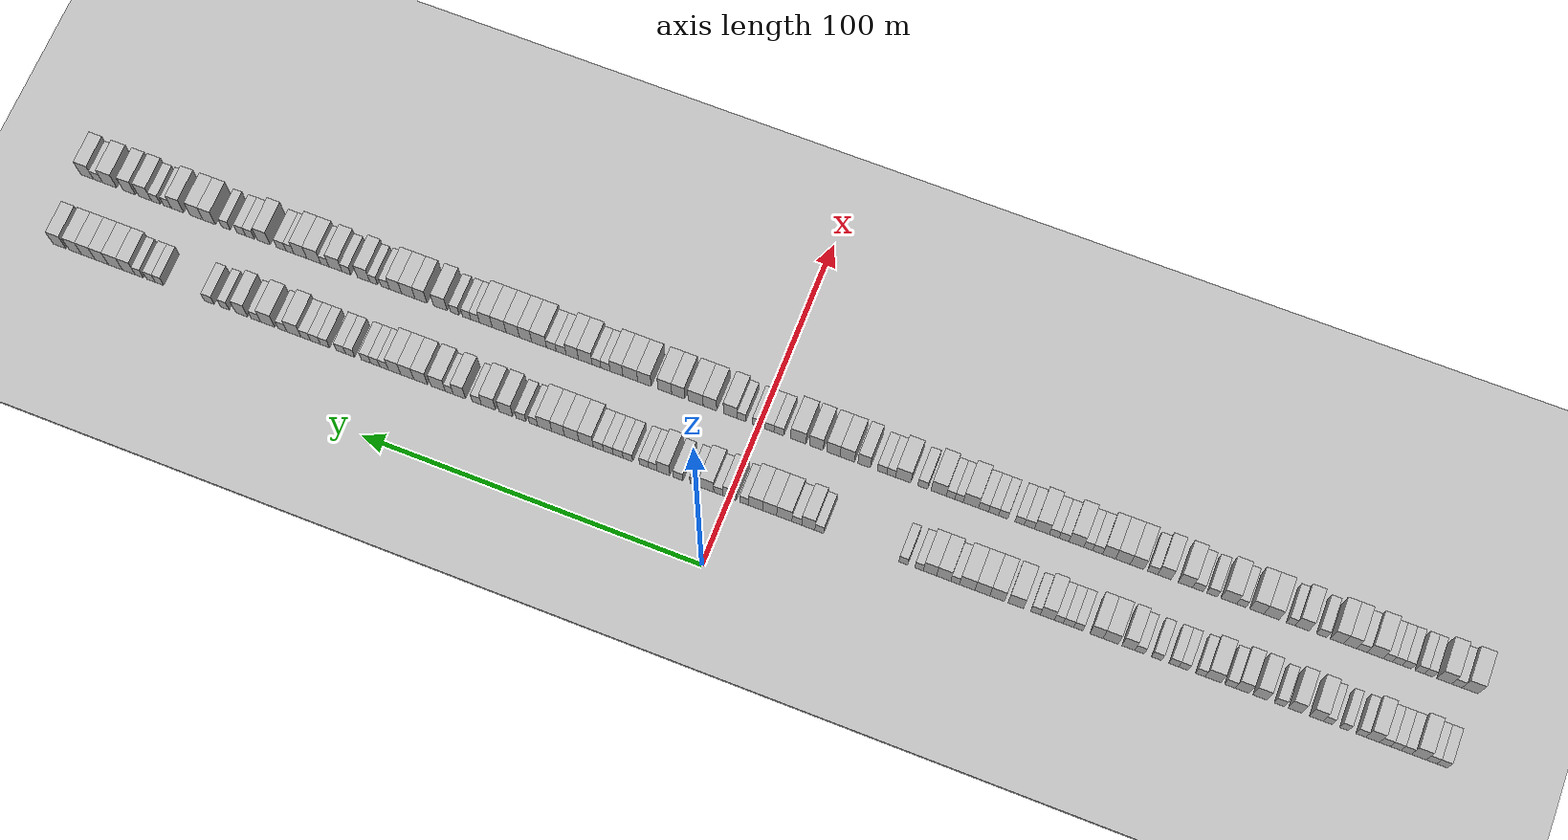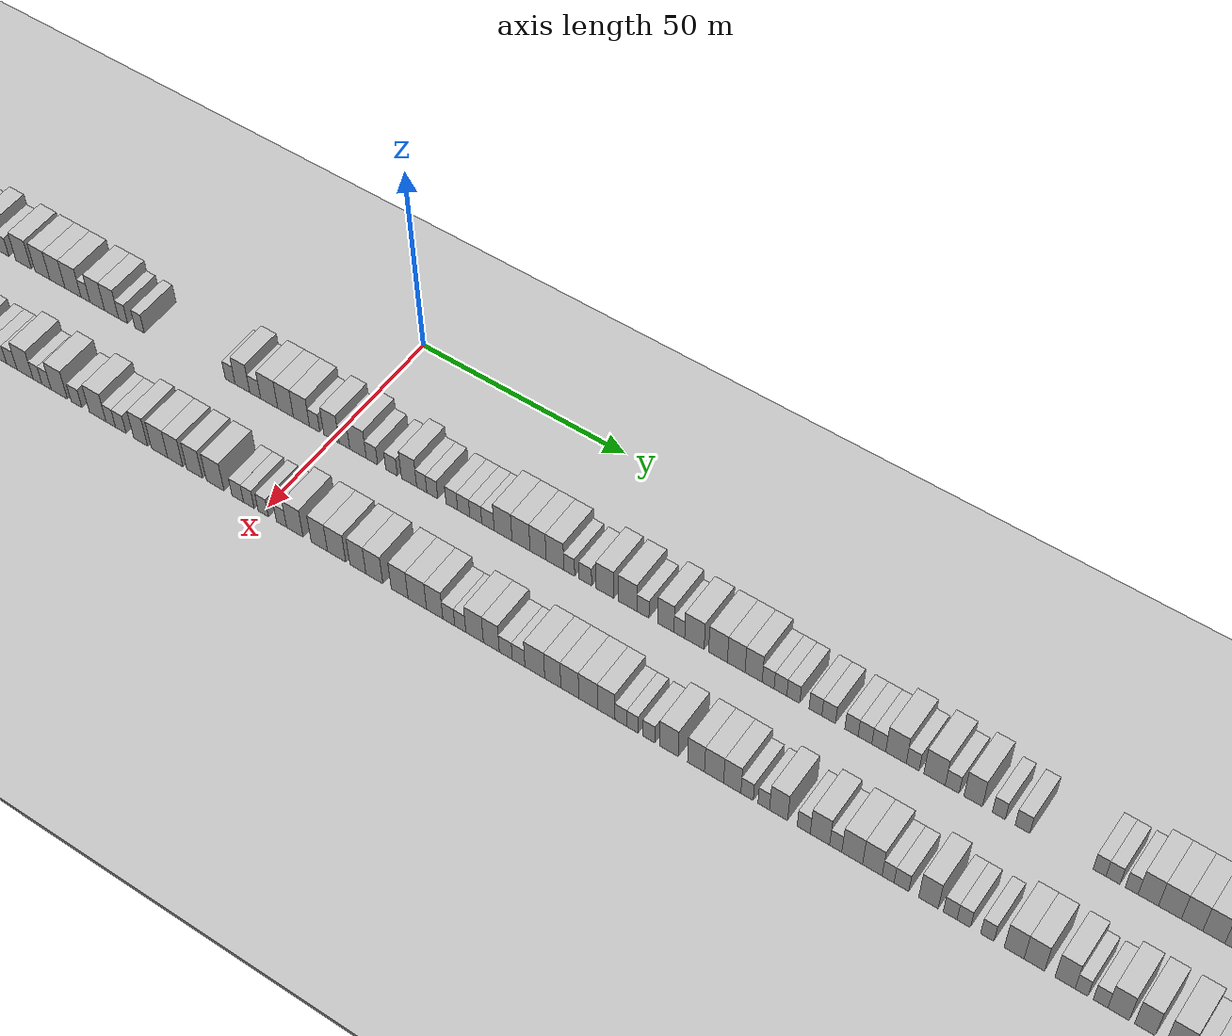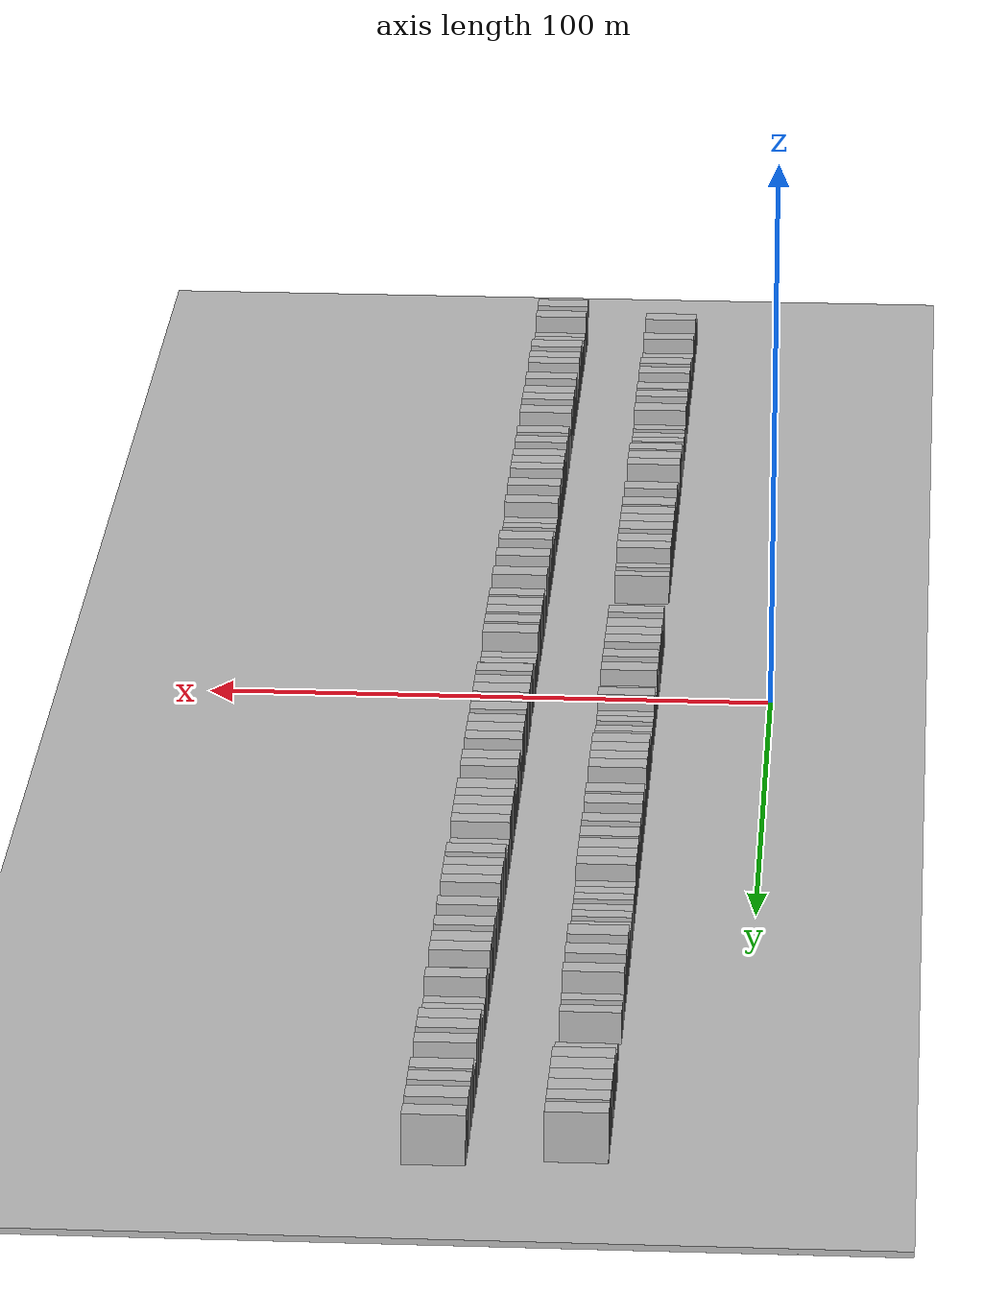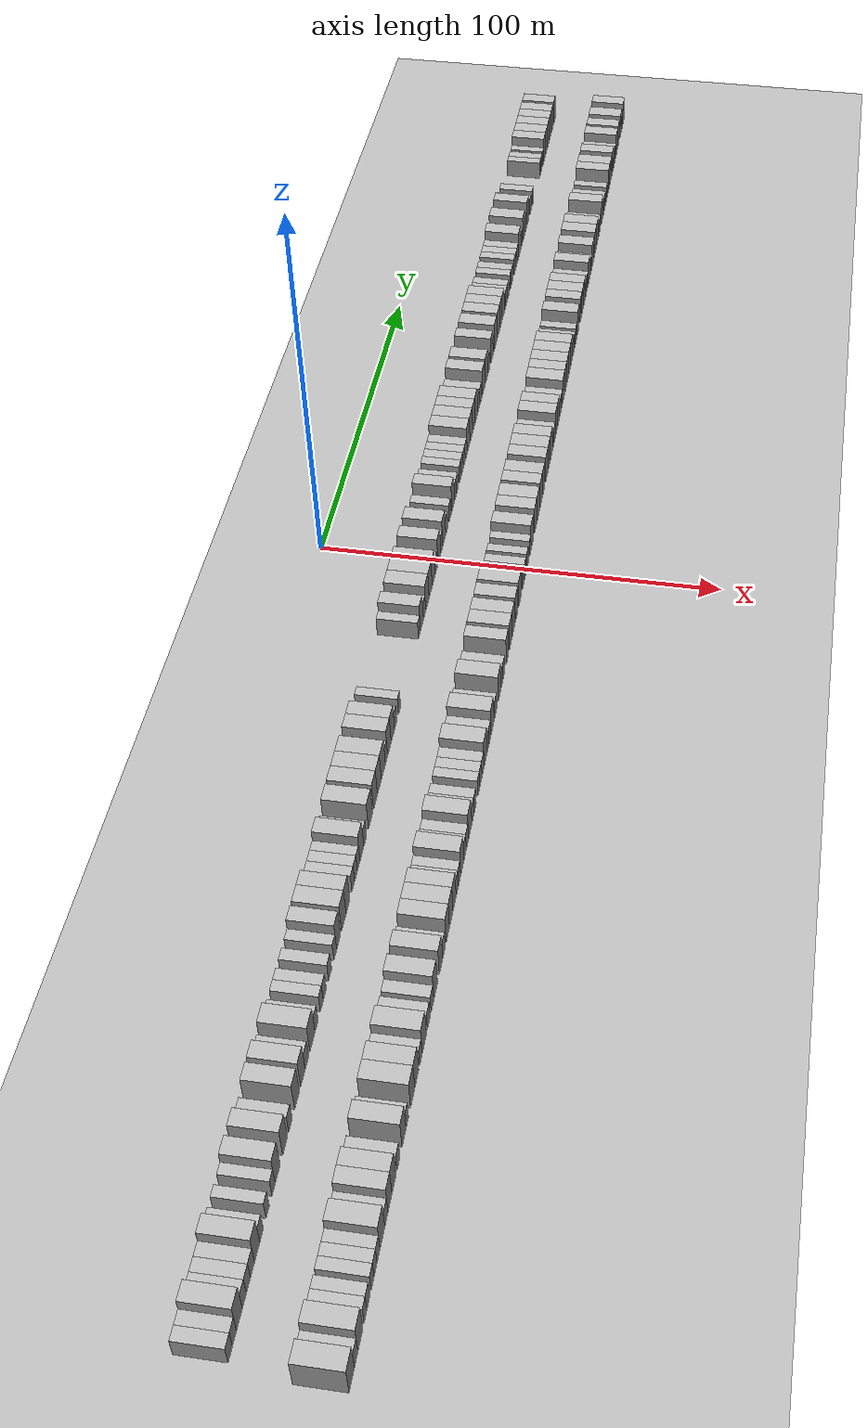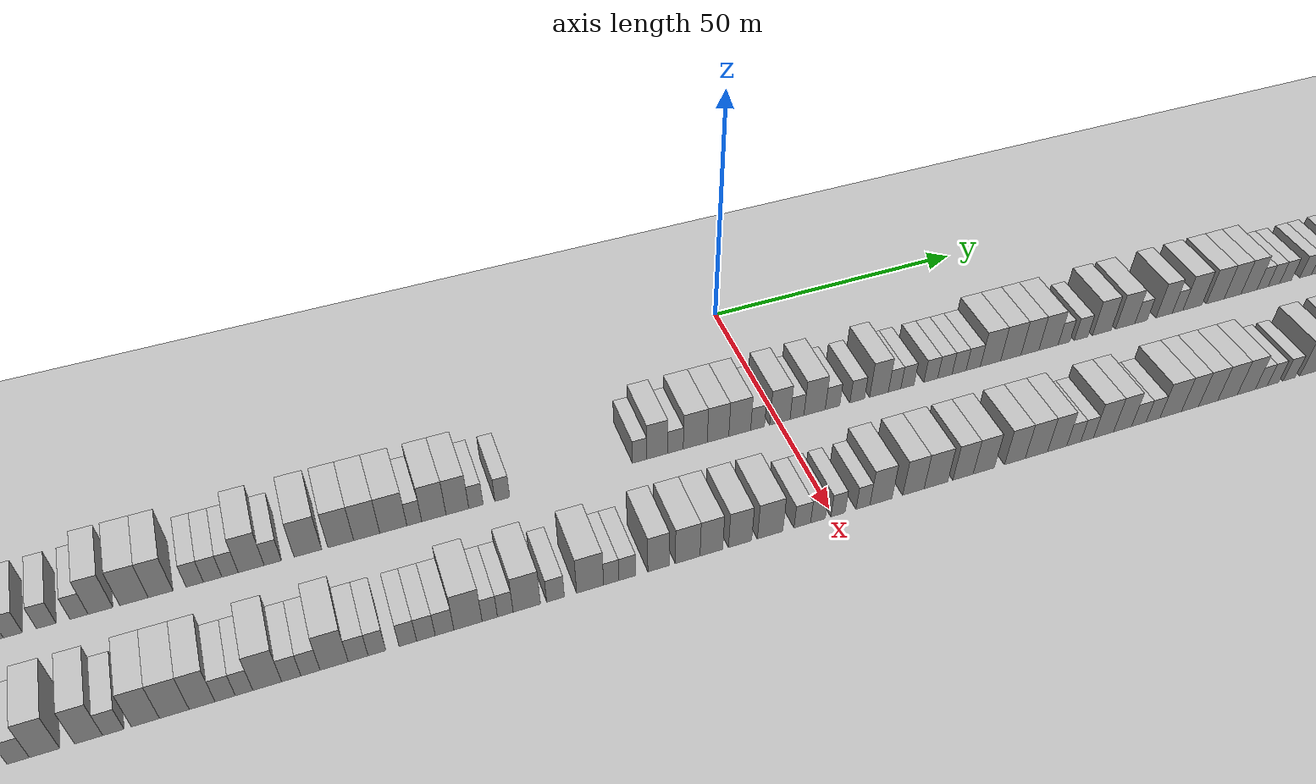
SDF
<?xml version="1.0" encoding="utf-8"?>

<sdf version="1.6">

   <world name="default">

      <gui fullscreen="0">

         <camera name="user_camera">

            <pose>-15 0 4.57585 0 0 0</pose>

            <view_controller>orbit</view_controller>

         </camera>

      </gui>

      <scene>

         <sky>

           <clouds>

             <speed>12</speed>

           </clouds>

         </sky>

         <ambient>0.4 0.4 0.4 1</ambient>

         <background>0.7 0.7 0.7 1</background>

         <shadows>1</shadows>

      </scene>

      <gravity>0 0 -9.8066</gravity>

      <magnetic_field>6e-06 2.3e-05 -4.2e-05</magnetic_field>

      <physics default="0" name="default_physics" type="ode">

         <ode>

            <solver>

               <type>quick</type>

               <iters>10</iters>

               <sor>1.0</sor>

               <use_dynamic_moi_rescaling>0</use_dynamic_moi_rescaling>

            </solver>

            <constraints>

               <cfm>0</cfm>

               <erp>0.2</erp>

               <contact_max_correcting_vel>100</contact_max_correcting_vel>

               <contact_surface_layer>0.001</contact_surface_layer>

            </constraints>

         </ode>

         <max_step_size>0.004</max_step_size>

         <real_time_factor>1</real_time_factor>

         <real_time_update_rate>250</real_time_update_rate>

      </physics>

      <light name="sun" type="directional">

         <cast_shadows>1</cast_shadows>

         <pose>0 0 10 0 0 0</pose>

         <diffuse>0.8 0.8 0.8 1</diffuse>

         <specular>0.2 0.2 0.2 1</specular>

         <attenuation>

            <range>1000</range>

            <constant>0.9</constant>

            <linear>0.01</linear>

            <quadratic>0.001</quadratic>

         </attenuation>

         <direction>-0.5 0.1 -0.9</direction>

      </light>

      <include>

         <name>ground_plane_1</name>

         <uri>model://HANNAS_ground_plane</uri>

         <pose>0 0 0  0 0 0</pose>

      </include>

      <include>

         <name>ground_plane_2</name>

         <uri>model://HANNAS_ground_plane</uri>

         <pose>100 0 0  0 0 0</pose>

      </include>

      <model name="building_1">

         <static>1</static>

         <pose frame="">25.0000 -200.5337 0 0.000000 0.000000 0.000000</pose>

         <link name="link">

            <pose frame="">0 0 3.00 0 0 0</pose>

            <collision name="collision">

               <geometry>

                  <box>

                     <size>10.0000 2.9326 6.0000</size>

                  </box>

               </geometry>

               <max_contacts>10</max_contacts>

               <surface>

                  <contact>

                     <ode/>

                  </contact>

                  <bounce/>

                  <friction>

                     <torsional>

                        <ode/>

                     </torsional>

                     <ode/>

                  </friction>

               </surface>

            </collision>

            <visual name="visual">

               <cast_shadows>0</cast_shadows>

               <geometry>

                  <box>

                     <size>10.0000 2.9326 6.0000</size>

                  </box>

               </geometry>

               <material>

                  <script>

                     <uri>model://HANNAS_wall/materials/scripts</uri>

                     <uri>model://HANNAS_wall/materials/textures</uri>

                     <name>vrc/HANNAS_wall</name>

                  </script>

               </material>

            </visual>

            <self_collide>0</self_collide>

            <enable_wind>0</enable_wind>

            <kinematic>0</kinematic>

         </link>

      </model>

      <model name="building_2">

         <static>1</static>

         <pose frame="">25.0000 -197.6434 0 0.000000 0.000000 0.000000</pose>

         <link name="link">

            <pose frame="">0 0 3.00 0 0 0</pose>

            <collision name="collision">

               <geometry>

                  <box>

                     <size>10.0000 2.8480 6.0000</size>

                  </box>

               </geometry>

               <max_contacts>10</max_contacts>

               <surface>

                  <contact>

                     <ode/>

                  </contact>

                  <bounce/>

                  <friction>

                     <torsional>

                        <ode/>

                     </torsional>

                     <ode/>

                  </friction>

               </surface>

            </collision>

            <visual name="visual">

               <cast_shadows>0</cast_shadows>

               <geometry>

                  <box>

                     <size>10.0000 2.8480 6.0000</size>

                  </box>

               </geometry>

               <material>

                  <script>

                     <uri>model://HANNAS_wall/materials/scripts</uri>

                     <uri>model://HANNAS_wall/materials/textures</uri>

                     <name>vrc/HANNAS_wall</name>

                  </script>

               </material>

            </visual>

            <self_collide>0</self_collide>

            <enable_wind>0</enable_wind>

            <kinematic>0</kinematic>

         </link>

      </model>

      <model name="building_3">

         <static>1</static>

         <pose frame="">25.0000 -194.2087 0 0.000000 0.000000 0.000000</pose>

         <link name="link">

            <pose frame="">0 0 4.50 0 0 0</pose>

            <collision name="collision">

               <geometry>

                  <box>

                     <size>10.0000 4.0214 9.0000</size>

                  </box>

               </geometry>

               <max_contacts>10</max_contacts>

               <surface>

                  <contact>

                     <ode/>

                  </contact>

                  <bounce/>

                  <friction>

                     <torsional>

                        <ode/>

                     </torsional>

                     <ode/>

                  </friction>

               </surface>

            </collision>

            <visual name="visual">

               <cast_shadows>0</cast_shadows>

               <geometry>

                  <box>

                     <size>10.0000 4.0214 9.0000</size>

                  </box>

               </geometry>

               <material>

                  <script>

                     <uri>model://HANNAS_wall/materials/scripts</uri>

                     <uri>model://HANNAS_wall/materials/textures</uri>

                     <name>vrc/HANNAS_wall</name>

                  </script>

               </material>

            </visual>

            <self_collide>0</self_collide>

            <enable_wind>0</enable_wind>

            <kinematic>0</kinematic>

         </link>

      </model>

      <model name="building_4">

         <static>1</static>

         <pose frame="">25.0000 -190.7882 0 0.000000 0.000000 0.000000</pose>

         <link name="link">

            <pose frame="">0 0 3.00 0 0 0</pose>

            <collision name="collision">

               <geometry>

                  <box>

                     <size>10.0000 2.8195 6.0000</size>

                  </box>

               </geometry>

               <max_contacts>10</max_contacts>

               <surface>

                  <contact>

                     <ode/>

                  </contact>

                  <bounce/>

                  <friction>

                     <torsional>

                        <ode/>

                     </torsional>

                     <ode/>

                  </friction>

               </surface>

            </collision>

            <visual name="visual">

               <cast_shadows>0</cast_shadows>

               <geometry>

                  <box>

                     <size>10.0000 2.8195 6.0000</size>

                  </box>

               </geometry>

               <material>

                  <script>

                     <uri>model://HANNAS_wall/materials/scripts</uri>

                     <uri>model://HANNAS_wall/materials/textures</uri>

                     <name>vrc/HANNAS_wall</name>

                  </script>

               </material>

            </visual>

            <self_collide>0</self_collide>

            <enable_wind>0</enable_wind>

            <kinematic>0</kinematic>

         </link>

      </model>

      <model name="building_5">

         <static>1</static>

         <pose frame="">25.0000 -187.9269 0 0.000000 0.000000 0.000000</pose>

         <link name="link">

            <pose frame="">0 0 3.00 0 0 0</pose>

            <collision name="collision">

               <geometry>

                  <box>

                     <size>10.0000 2.9031 6.0000</size>

                  </box>

               </geometry>

               <max_contacts>10</max_contacts>

               <surface>

                  <contact>

                     <ode/>

                  </contact>

                  <bounce/>

                  <friction>

                     <torsional>

                        <ode/>

                     </torsional>

                     <ode/>

                  </friction>

               </surface>

            </collision>

            <visual name="visual">

               <cast_shadows>0</cast_shadows>

               <geometry>

                  <box>

                     <size>10.0000 2.9031 6.0000</size>

                  </box>

               </geometry>

               <material>

                  <script>

                     <uri>model://HANNAS_wall/materials/scripts</uri>

                     <uri>model://HANNAS_wall/materials/textures</uri>

                     <name>vrc/HANNAS_wall</name>

                  </script>

               </material>

            </visual>

            <self_collide>0</self_collide>

            <enable_wind>0</enable_wind>

            <kinematic>0</kinematic>

         </link>

      </model>

      <model name="building_6">

         <static>1</static>

         <pose frame="">25.0000 -185.0128 0 0.000000 0.000000 0.000000</pose>

         <link name="link">

            <pose frame="">0 0 3.00 0 0 0</pose>

            <collision name="collision">

               <geometry>

                  <box>

                     <size>10.0000 2.9252 6.0000</size>

                  </box>

               </geometry>

               <max_contacts>10</max_contacts>

               <surface>

                  <contact>

                     <ode/>

                  </contact>

                  <bounce/>

                  <friction>

                     <torsional>

                        <ode/>

                     </torsional>

                     <ode/>

                  </friction>

               </surface>

            </collision>

            <visual name="visual">

               <cast_shadows>0</cast_shadows>

               <geometry>

                  <box>

                     <size>10.0000 2.9252 6.0000</size>

                  </box>

               </geometry>

               <material>

                  <script>

                     <uri>model://HANNAS_wall/materials/scripts</uri>

                     <uri>model://HANNAS_wall/materials/textures</uri>

                     <name>vrc/HANNAS_wall</name>

                  </script>

               </material>

            </visual>

            <self_collide>0</self_collide>

            <enable_wind>0</enable_wind>

            <kinematic>0</kinematic>

         </link>

      </model>

      <model name="building_7">

         <static>1</static>

         <pose frame="">25.0000 -181.6386 0 0.000000 0.000000 0.000000</pose>

         <link name="link">

            <pose frame="">0 0 4.50 0 0 0</pose>

            <collision name="collision">

               <geometry>

                  <box>

                     <size>10.0000 3.8232 9.0000</size>

                  </box>

               </geometry>

               <max_contacts>10</max_contacts>

               <surface>

                  <contact>

                     <ode/>

                  </contact>

                  <bounce/>

                  <friction>

                     <torsional>

                        <ode/>

                     </torsional>

                     <ode/>

                  </friction>

               </surface>

            </collision>

            <visual name="visual">

               <cast_shadows>0</cast_shadows>

               <geometry>

                  <box>

                     <size>10.0000 3.8232 9.0000</size>

                  </box>

               </geometry>

               <material>

                  <script>

                     <uri>model://HANNAS_wall/materials/scripts</uri>

                     <uri>model://HANNAS_wall/materials/textures</uri>

                     <name>vrc/HANNAS_wall</name>

                  </script>

               </material>

            </visual>

            <self_collide>0</self_collide>

            <enable_wind>0</enable_wind>

            <kinematic>0</kinematic>

         </link>

      </model>

      <model name="building_8">

         <static>1</static>

         <pose frame="">25.0000 -178.3796 0 0.000000 0.000000 0.000000</pose>

         <link name="link">

            <pose frame="">0 0 3.00 0 0 0</pose>

            <collision name="collision">

               <geometry>

                  <box>

                     <size>10.0000 2.6949 6.0000</size>

                  </box>

               </geometry>

               <max_contacts>10</max_contacts>

               <surface>

                  <contact>

                     <ode/>

                  </contact>

                  <bounce/>

                  <friction>

                     <torsional>

                        <ode/>

                     </torsional>

                     <ode/>

                  </friction>

               </surface>

            </collision>

            <visual name="visual">

               <cast_shadows>0</cast_shadows>

               <geometry>

                  <box>

                     <size>10.0000 2.6949 6.0000</size>

                  </box>

               </geometry>

               <material>

                  <script>

                     <uri>model://HANNAS_wall/materials/scripts</uri>

                     <uri>model://HANNAS_wall/materials/textures</uri>

                     <name>vrc/HANNAS_wall</name>

                  </script>

               </material>

            </visual>

            <self_collide>0</self_collide>

            <enable_wind>0</enable_wind>

            <kinematic>0</kinematic>

         </link>

      </model>

      <model name="building_9">

         <static>1</static>

         <pose frame="">25.0000 -173.8010 0 0.000000 0.000000 0.000000</pose>

         <link name="link">

            <pose frame="">0 0 3.00 0 0 0</pose>

            <collision name="collision">

               <geometry>

                  <box>

                     <size>10.0000 2.4623 6.0000</size>

                  </box>

               </geometry>

               <max_contacts>10</max_contacts>

               <surface>

                  <contact>

                     <ode/>

                  </contact>

                  <bounce/>

                  <friction>

                     <torsional>

                        <ode/>

                     </torsional>

                     <ode/>

                  </friction>

               </surface>

            </collision>

            <visual name="visual">

               <cast_shadows>0</cast_shadows>

               <geometry>

                  <box>

                     <size>10.0000 2.4623 6.0000</size>

                  </box>

               </geometry>

               <material>

                  <script>

                     <uri>model://HANNAS_wall/materials/scripts</uri>

                     <uri>model://HANNAS_wall/materials/textures</uri>

                     <name>vrc/HANNAS_wall</name>

                  </script>

               </material>

            </visual>

            <self_collide>0</self_collide>

            <enable_wind>0</enable_wind>

            <kinematic>0</kinematic>

         </link>

      </model>

      <model name="building_10">

         <static>1</static>

         <pose frame="">25.0000 -169.3155 0 0.000000 0.000000 0.000000</pose>

         <link name="link">

            <pose frame="">0 0 3.00 0 0 0</pose>

            <collision name="collision">

               <geometry>

                  <box>

                     <size>10.0000 2.5087 6.0000</size>

                  </box>

               </geometry>

               <max_contacts>10</max_contacts>

               <surface>

                  <contact>

                     <ode/>

                  </contact>

                  <bounce/>

                  <friction>

                     <torsional>

                        <ode/>

                     </torsional>

                     <ode/>

                  </friction>

               </surface>

            </collision>

            <visual name="visual">

               <cast_shadows>0</cast_shadows>

               <geometry>

                  <box>

                     <size>10.0000 2.5087 6.0000</size>

                  </box>

               </geometry>

               <material>

                  <script>

                     <uri>model://HANNAS_wall/materials/scripts</uri>

                     <uri>model://HANNAS_wall/materials/textures</uri>

                     <name>vrc/HANNAS_wall</name>

                  </script>

               </material>

            </visual>

            <self_collide>0</self_collide>

            <enable_wind>0</enable_wind>

            <kinematic>0</kinematic>

         </link>

      </model>

      <model name="building_11">

         <static>1</static>

         <pose frame="">25.0000 -166.1479 0 0.000000 0.000000 0.000000</pose>

         <link name="link">

            <pose frame="">0 0 4.50 0 0 0</pose>

            <collision name="collision">

               <geometry>

                  <box>

                     <size>10.0000 3.8265 9.0000</size>

                  </box>

               </geometry>

               <max_contacts>10</max_contacts>

               <surface>

                  <contact>

                     <ode/>

                  </contact>

                  <bounce/>

                  <friction>

                     <torsional>

                        <ode/>

                     </torsional>

                     <ode/>

                  </friction>

               </surface>

            </collision>

            <visual name="visual">

               <cast_shadows>0</cast_shadows>

               <geometry>

                  <box>

                     <size>10.0000 3.8265 9.0000</size>

                  </box>

               </geometry>

               <material>

                  <script>

                     <uri>model://HANNAS_wall/materials/scripts</uri>

                     <uri>model://HANNAS_wall/materials/textures</uri>

                     <name>vrc/HANNAS_wall</name>

                  </script>

               </material>

            </visual>

            <self_collide>0</self_collide>

            <enable_wind>0</enable_wind>

            <kinematic>0</kinematic>

         </link>

      </model>

      <model name="building_12">

         <static>1</static>

         <pose frame="">25.0000 -160.3497 0 0.000000 0.000000 0.000000</pose>

         <link name="link">

            <pose frame="">0 0 4.50 0 0 0</pose>

            <collision name="collision">

               <geometry>

                  <box>

                     <size>10.0000 3.7699 9.0000</size>

                  </box>

               </geometry>

               <max_contacts>10</max_contacts>

               <surface>

                  <contact>

                     <ode/>

                  </contact>

                  <bounce/>

                  <friction>

                     <torsional>

                        <ode/>

                     </torsional>

                     <ode/>

                  </friction>

               </surface>

            </collision>

            <visual name="visual">

               <cast_shadows>0</cast_shadows>

               <geometry>

                  <box>

                     <size>10.0000 3.7699 9.0000</size>

                  </box>

               </geometry>

               <material>

                  <script>

                     <uri>model://HANNAS_wall/materials/scripts</uri>

                     <uri>model://HANNAS_wall/materials/textures</uri>

                     <name>vrc/HANNAS_wall</name>

                  </script>

               </material>

            </visual>

            <self_collide>0</self_collide>

            <enable_wind>0</enable_wind>

            <kinematic>0</kinematic>

         </link>

      </model>

      <model name="building_13">

         <static>1</static>

         <pose frame="">25.0000 -156.0359 0 0.000000 0.000000 0.000000</pose>

         <link name="link">

            <pose frame="">0 0 3.00 0 0 0</pose>

            <collision name="collision">

               <geometry>

                  <box>

                     <size>10.0000 2.8578 6.0000</size>

                  </box>

               </geometry>

               <max_contacts>10</max_contacts>

               <surface>

                  <contact>

                     <ode/>

                  </contact>

                  <bounce/>

                  <friction>

                     <torsional>

                        <ode/>

                     </torsional>

                     <ode/>

                  </friction>

               </surface>

            </collision>

            <visual name="visual">

               <cast_shadows>0</cast_shadows>

               <geometry>

                  <box>

                     <size>10.0000 2.8578 6.0000</size>

                  </box>

               </geometry>

               <material>

                  <script>

                     <uri>model://HANNAS_wall/materials/scripts</uri>

                     <uri>model://HANNAS_wall/materials/textures</uri>

                     <name>vrc/HANNAS_wall</name>

                  </script>

               </material>

            </visual>

            <self_collide>0</self_collide>

            <enable_wind>0</enable_wind>

            <kinematic>0</kinematic>

         </link>

      </model>

      <model name="building_14">

         <static>1</static>

         <pose frame="">25.0000 -150.6478 0 0.000000 0.000000 0.000000</pose>

         <link name="link">

            <pose frame="">0 0 4.50 0 0 0</pose>

            <collision name="collision">

               <geometry>

                  <box>

                     <size>10.0000 3.9184 9.0000</size>

                  </box>

               </geometry>

               <max_contacts>10</max_contacts>

               <surface>

                  <contact>

                     <ode/>

                  </contact>

                  <bounce/>

                  <friction>

                     <torsional>

                        <ode/>

                     </torsional>

                     <ode/>

                  </friction>

               </surface>

            </collision>

            <visual name="visual">

               <cast_shadows>0</cast_shadows>

               <geometry>

                  <box>

                     <size>10.0000 3.9184 9.0000</size>

                  </box>

               </geometry>

               <material>

                  <script>

                     <uri>model://HANNAS_wall/materials/scripts</uri>

                     <uri>model://HANNAS_wall/materials/textures</uri>

                     <name>vrc/HANNAS_wall</name>

                  </script>

               </material>

            </visual>

            <self_collide>0</self_collide>

            <enable_wind>0</enable_wind>

            <kinematic>0</kinematic>

         </link>

      </model>

      <model name="building_15">

         <static>1</static>

         <pose frame="">25.0000 -145.7635 0 0.000000 0.000000 0.000000</pose>

         <link name="link">

            <pose frame="">0 0 4.50 0 0 0</pose>

            <collision name="collision">

               <geometry>

                  <box>

                     <size>10.0000 3.8500 9.0000</size>

                  </box>

               </geometry>

               <max_contacts>10</max_contacts>

               <surface>

                  <contact>

                     <ode/>

                  </contact>

                  <bounce/>

                  <friction>

                     <torsional>

                        <ode/>

                     </torsional>

                     <ode/>

                  </friction>

               </surface>

            </collision>

            <visual name="visual">

               <cast_shadows>0</cast_shadows>

               <geometry>

                  <box>

                     <size>10.0000 3.8500 9.0000</size>

                  </box>

               </geometry>

               <material>

                  <script>

                     <uri>model://HANNAS_wall/materials/scripts</uri>

                     <uri>model://HANNAS_wall/materials/textures</uri>

                     <name>vrc/HANNAS_wall</name>

                  </script>

               </material>

            </visual>

            <self_collide>0</self_collide>

            <enable_wind>0</enable_wind>

            <kinematic>0</kinematic>

         </link>

      </model>

      <model name="building_16">

         <static>1</static>

         <pose frame="">25.0000 -142.3542 0 0.000000 0.000000 0.000000</pose>

         <link name="link">

            <pose frame="">0 0 3.00 0 0 0</pose>

            <collision name="collision">

               <geometry>

                  <box>

                     <size>10.0000 2.9686 6.0000</size>

                  </box>

               </geometry>

               <max_contacts>10</max_contacts>

               <surface>

                  <contact>

                     <ode/>

                  </contact>

                  <bounce/>

                  <friction>

                     <torsional>

                        <ode/>

                     </torsional>

                     <ode/>

                  </friction>

               </surface>

            </collision>

            <visual name="visual">

               <cast_shadows>0</cast_shadows>

               <geometry>

                  <box>

                     <size>10.0000 2.9686 6.0000</size>

                  </box>

               </geometry>

               <material>

                  <script>

                     <uri>model://HANNAS_wall/materials/scripts</uri>

                     <uri>model://HANNAS_wall/materials/textures</uri>

                     <name>vrc/HANNAS_wall</name>

                  </script>

               </material>

            </visual>

            <self_collide>0</self_collide>

            <enable_wind>0</enable_wind>

            <kinematic>0</kinematic>

         </link>

      </model>

      <model name="building_17">

         <static>1</static>

         <pose frame="">25.0000 -137.6517 0 0.000000 0.000000 0.000000</pose>

         <link name="link">

            <pose frame="">0 0 4.50 0 0 0</pose>

            <collision name="collision">

               <geometry>

                  <box>

                     <size>10.0000 4.4365 9.0000</size>

                  </box>

               </geometry>

               <max_contacts>10</max_contacts>

               <surface>

                  <contact>

                     <ode/>

                  </contact>

                  <bounce/>

                  <friction>

                     <torsional>

                        <ode/>

                     </torsional>

                     <ode/>

                  </friction>

               </surface>

            </collision>

            <visual name="visual">

               <cast_shadows>0</cast_shadows>

               <geometry>

                  <box>

                     <size>10.0000 4.4365 9.0000</size>

                  </box>

               </geometry>

               <material>

                  <script>

                     <uri>model://HANNAS_wall/materials/scripts</uri>

                     <uri>model://HANNAS_wall/materials/textures</uri>

                     <name>vrc/HANNAS_wall</name>

                  </script>

               </material>

            </visual>

            <self_collide>0</self_collide>

            <enable_wind>0</enable_wind>

            <kinematic>0</kinematic>

         </link>

      </model>

      <model name="building_18">

         <static>1</static>

         <pose frame="">25.0000 -134.0918 0 0.000000 0.000000 0.000000</pose>

         <link name="link">

            <pose frame="">0 0 3.00 0 0 0</pose>

            <collision name="collision">

               <geometry>

                  <box>

                     <size>10.0000 2.6832 6.0000</size>

                  </box>

               </geometry>

               <max_contacts>10</max_contacts>

               <surface>

                  <contact>

                     <ode/>

                  </contact>

                  <bounce/>

                  <friction>

                     <torsional>

                        <ode/>

                     </torsional>

                     <ode/>

                  </friction>

               </surface>

            </collision>

            <visual name="visual">

               <cast_shadows>0</cast_shadows>

               <geometry>

                  <box>

                     <size>10.0000 2.6832 6.0000</size>

                  </box>

               </geometry>

               <material>

                  <script>

                     <uri>model://HANNAS_wall/materials/scripts</uri>

                     <uri>model://HANNAS_wall/materials/textures</uri>

                     <name>vrc/HANNAS_wall</name>

                  </script>

               </material>

            </visual>

            <self_collide>0</self_collide>

            <enable_wind>0</enable_wind>

            <kinematic>0</kinematic>

         </link>

      </model>

      <model name="building_19">

         <static>1</static>

         <pose frame="">25.0000 -129.4211 0 0.000000 0.000000 0.000000</pose>

         <link name="link">

            <pose frame="">0 0 3.00 0 0 0</pose>

            <collision name="collision">

               <geometry>

                  <box>

                     <size>10.0000 2.6581 6.0000</size>

                  </box>

               </geometry>

               <max_contacts>10</max_contacts>

               <surface>

                  <contact>

                     <ode/>

                  </contact>

                  <bounce/>

                  <friction>

                     <torsional>

                        <ode/>

                     </torsional>

                     <ode/>

                  </friction>

               </surface>

            </collision>

            <visual name="visual">

               <cast_shadows>0</cast_shadows>

               <geometry>

                  <box>

                     <size>10.0000 2.6581 6.0000</size>

                  </box>

               </geometry>

               <material>

                  <script>

                     <uri>model://HANNAS_wall/materials/scripts</uri>

                     <uri>model://HANNAS_wall/materials/textures</uri>

                     <name>vrc/HANNAS_wall</name>

                  </script>

               </material>

            </visual>

            <self_collide>0</self_collide>

            <enable_wind>0</enable_wind>

            <kinematic>0</kinematic>

         </link>

      </model>

      <model name="building_20">

         <static>1</static>

         <pose frame="">25.0000 -126.7219 0 0.000000 0.000000 0.000000</pose>

         <link name="link">

            <pose frame="">0 0 3.00 0 0 0</pose>

            <collision name="collision">

               <geometry>

                  <box>

                     <size>10.0000 2.7403 6.0000</size>

                  </box>

               </geometry>

               <max_contacts>10</max_contacts>

               <surface>

                  <contact>

                     <ode/>

                  </contact>

                  <bounce/>

                  <friction>

                     <torsional>

                        <ode/>

                     </torsional>

                     <ode/>

                  </friction>

               </surface>

            </collision>

            <visual name="visual">

               <cast_shadows>0</cast_shadows>

               <geometry>

                  <box>

                     <size>10.0000 2.7403 6.0000</size>

                  </box>

               </geometry>

               <material>

                  <script>

                     <uri>model://HANNAS_wall/materials/scripts</uri>

                     <uri>model://HANNAS_wall/materials/textures</uri>

                     <name>vrc/HANNAS_wall</name>

                  </script>

               </material>

            </visual>

            <self_collide>0</self_collide>

            <enable_wind>0</enable_wind>

            <kinematic>0</kinematic>

         </link>

      </model>

      <model name="building_21">

         <static>1</static>

         <pose frame="">25.0000 -121.9303 0 0.000000 0.000000 0.000000</pose>

         <link name="link">

            <pose frame="">0 0 3.00 0 0 0</pose>

            <collision name="collision">

               <geometry>

                  <box>

                     <size>10.0000 2.8429 6.0000</size>

                  </box>

               </geometry>

               <max_contacts>10</max_contacts>

               <surface>

                  <contact>

                     <ode/>

                  </contact>

                  <bounce/>

                  <friction>

                     <torsional>

                        <ode/>

                     </torsional>

                     <ode/>

                  </friction>

               </surface>

            </collision>

            <visual name="visual">

               <cast_shadows>0</cast_shadows>

               <geometry>

                  <box>

                     <size>10.0000 2.8429 6.0000</size>

                  </box>

               </geometry>

               <material>

                  <script>

                     <uri>model://HANNAS_wall/materials/scripts</uri>

                     <uri>model://HANNAS_wall/materials/textures</uri>

                     <name>vrc/HANNAS_wall</name>

                  </script>

               </material>

            </visual>

            <self_collide>0</self_collide>

            <enable_wind>0</enable_wind>

            <kinematic>0</kinematic>

         </link>

      </model>

      <model name="building_22">

         <static>1</static>

         <pose frame="">25.0000 -117.1746 0 0.000000 0.000000 0.000000</pose>

         <link name="link">

            <pose frame="">0 0 3.00 0 0 0</pose>

            <collision name="collision">

               <geometry>

                  <box>

                     <size>10.0000 2.6685 6.0000</size>

                  </box>

               </geometry>

               <max_contacts>10</max_contacts>

               <surface>

                  <contact>

                     <ode/>

                  </contact>

                  <bounce/>

                  <friction>

                     <torsional>

                        <ode/>

                     </torsional>

                     <ode/>

                  </friction>

               </surface>

            </collision>

            <visual name="visual">

               <cast_shadows>0</cast_shadows>

               <geometry>

                  <box>

                     <size>10.0000 2.6685 6.0000</size>

                  </box>

               </geometry>

               <material>

                  <script>

                     <uri>model://HANNAS_wall/materials/scripts</uri>

                     <uri>model://HANNAS_wall/materials/textures</uri>

                     <name>vrc/HANNAS_wall</name>

                  </script>

               </material>

            </visual>

            <self_collide>0</self_collide>

            <enable_wind>0</enable_wind>

            <kinematic>0</kinematic>

         </link>

      </model>

      <model name="building_23">

         <static>1</static>

         <pose frame="">25.0000 -114.0231 0 0.000000 0.000000 0.000000</pose>

         <link name="link">

            <pose frame="">0 0 4.50 0 0 0</pose>

            <collision name="collision">

               <geometry>

                  <box>

                     <size>10.0000 3.6344 9.0000</size>

                  </box>

               </geometry>

               <max_contacts>10</max_contacts>

               <surface>

                  <contact>

                     <ode/>

                  </contact>

                  <bounce/>

                  <friction>

                     <torsional>

                        <ode/>

                     </torsional>

                     <ode/>

                  </friction>

               </surface>

            </collision>

            <visual name="visual">

               <cast_shadows>0</cast_shadows>

               <geometry>

                  <box>

                     <size>10.0000 3.6344 9.0000</size>

                  </box>

               </geometry>

               <material>

                  <script>

                     <uri>model://HANNAS_wall/materials/scripts</uri>

                     <uri>model://HANNAS_wall/materials/textures</uri>

                     <name>vrc/HANNAS_wall</name>

                  </script>

               </material>

            </visual>

            <self_collide>0</self_collide>

            <enable_wind>0</enable_wind>

            <kinematic>0</kinematic>

         </link>

      </model>

      <model name="building_24">

         <static>1</static>

         <pose frame="">25.0000 -109.0692 0 0.000000 0.000000 0.000000</pose>

         <link name="link">

            <pose frame="">0 0 4.50 0 0 0</pose>

            <collision name="collision">

               <geometry>

                  <box>

                     <size>10.0000 4.2735 9.0000</size>

                  </box>

               </geometry>

               <max_contacts>10</max_contacts>

               <surface>

                  <contact>

                     <ode/>

                  </contact>

                  <bounce/>

                  <friction>

                     <torsional>

                        <ode/>

                     </torsional>

                     <ode/>

                  </friction>

               </surface>

            </collision>

            <visual name="visual">

               <cast_shadows>0</cast_shadows>

               <geometry>

                  <box>

                     <size>10.0000 4.2735 9.0000</size>

                  </box>

               </geometry>

               <material>

                  <script>

                     <uri>model://HANNAS_wall/materials/scripts</uri>

                     <uri>model://HANNAS_wall/materials/textures</uri>

                     <name>vrc/HANNAS_wall</name>

                  </script>

               </material>

            </visual>

            <self_collide>0</self_collide>

            <enable_wind>0</enable_wind>

            <kinematic>0</kinematic>

         </link>

      </model>

      <model name="building_25">

         <static>1</static>

         <pose frame="">25.0000 -105.0818 0 0.000000 0.000000 0.000000</pose>

         <link name="link">

            <pose frame="">0 0 4.50 0 0 0</pose>

            <collision name="collision">

               <geometry>

                  <box>

                     <size>10.0000 3.7013 9.0000</size>

                  </box>

               </geometry>

               <max_contacts>10</max_contacts>

               <surface>

                  <contact>

                     <ode/>

                  </contact>

                  <bounce/>

                  <friction>

                     <torsional>

                        <ode/>

                     </torsional>

                     <ode/>

                  </friction>

               </surface>

            </collision>

            <visual name="visual">

               <cast_shadows>0</cast_shadows>

               <geometry>

                  <box>

                     <size>10.0000 3.7013 9.0000</size>

                  </box>

               </geometry>

               <material>

                  <script>

                     <uri>model://HANNAS_wall/materials/scripts</uri>

                     <uri>model://HANNAS_wall/materials/textures</uri>

                     <name>vrc/HANNAS_wall</name>

                  </script>

               </material>

            </visual>

            <self_collide>0</self_collide>

            <enable_wind>0</enable_wind>

            <kinematic>0</kinematic>

         </link>

      </model>

      <model name="building_26">

         <static>1</static>

         <pose frame="">25.0000 -99.9082 0 0.000000 0.000000 0.000000</pose>

         <link name="link">

            <pose frame="">0 0 3.00 0 0 0</pose>

            <collision name="collision">

               <geometry>

                  <box>

                     <size>10.0000 2.6459 6.0000</size>

                  </box>

               </geometry>

               <max_contacts>10</max_contacts>

               <surface>

                  <contact>

                     <ode/>

                  </contact>

                  <bounce/>

                  <friction>

                     <torsional>

                        <ode/>

                     </torsional>

                     <ode/>

                  </friction>

               </surface>

            </collision>

            <visual name="visual">

               <cast_shadows>0</cast_shadows>

               <geometry>

                  <box>

                     <size>10.0000 2.6459 6.0000</size>

                  </box>

               </geometry>

               <material>

                  <script>

                     <uri>model://HANNAS_wall/materials/scripts</uri>

                     <uri>model://HANNAS_wall/materials/textures</uri>

                     <name>vrc/HANNAS_wall</name>

                  </script>

               </material>

            </visual>

            <self_collide>0</self_collide>

            <enable_wind>0</enable_wind>

            <kinematic>0</kinematic>

         </link>

      </model>

      <model name="building_27">

         <static>1</static>

         <pose frame="">25.0000 -97.1660 0 0.000000 0.000000 0.000000</pose>

         <link name="link">

            <pose frame="">0 0 3.00 0 0 0</pose>

            <collision name="collision">

               <geometry>

                  <box>

                     <size>10.0000 2.8386 6.0000</size>

                  </box>

               </geometry>

               <max_contacts>10</max_contacts>

               <surface>

                  <contact>

                     <ode/>

                  </contact>

                  <bounce/>

                  <friction>

                     <torsional>

                        <ode/>

                     </torsional>

                     <ode/>

                  </friction>

               </surface>

            </collision>

            <visual name="visual">

               <cast_shadows>0</cast_shadows>

               <geometry>

                  <box>

                     <size>10.0000 2.8386 6.0000</size>

                  </box>

               </geometry>

               <material>

                  <script>

                     <uri>model://HANNAS_wall/materials/scripts</uri>

                     <uri>model://HANNAS_wall/materials/textures</uri>

                     <name>vrc/HANNAS_wall</name>

                  </script>

               </material>

            </visual>

            <self_collide>0</self_collide>

            <enable_wind>0</enable_wind>

            <kinematic>0</kinematic>

         </link>

      </model>

      <model name="building_28">

         <static>1</static>

         <pose frame="">25.0000 -94.4889 0 0.000000 0.000000 0.000000</pose>

         <link name="link">

            <pose frame="">0 0 3.00 0 0 0</pose>

            <collision name="collision">

               <geometry>

                  <box>

                     <size>10.0000 2.5156 6.0000</size>

                  </box>

               </geometry>

               <max_contacts>10</max_contacts>

               <surface>

                  <contact>

                     <ode/>

                  </contact>

                  <bounce/>

                  <friction>

                     <torsional>

                        <ode/>

                     </torsional>

                     <ode/>

                  </friction>

               </surface>

            </collision>

            <visual name="visual">

               <cast_shadows>0</cast_shadows>

               <geometry>

                  <box>

                     <size>10.0000 2.5156 6.0000</size>

                  </box>

               </geometry>

               <material>

                  <script>

                     <uri>model://HANNAS_wall/materials/scripts</uri>

                     <uri>model://HANNAS_wall/materials/textures</uri>

                     <name>vrc/HANNAS_wall</name>

                  </script>

               </material>

            </visual>

            <self_collide>0</self_collide>

            <enable_wind>0</enable_wind>

            <kinematic>0</kinematic>

         </link>

      </model>

      <model name="building_29">

         <static>1</static>

         <pose frame="">25.0000 -91.2158 0 0.000000 0.000000 0.000000</pose>

         <link name="link">

            <pose frame="">0 0 4.50 0 0 0</pose>

            <collision name="collision">

               <geometry>

                  <box>

                     <size>10.0000 4.0306 9.0000</size>

                  </box>

               </geometry>

               <max_contacts>10</max_contacts>

               <surface>

                  <contact>

                     <ode/>

                  </contact>

                  <bounce/>

                  <friction>

                     <torsional>

                        <ode/>

                     </torsional>

                     <ode/>

                  </friction>

               </surface>

            </collision>

            <visual name="visual">

               <cast_shadows>0</cast_shadows>

               <geometry>

                  <box>

                     <size>10.0000 4.0306 9.0000</size>

                  </box>

               </geometry>

               <material>

                  <script>

                     <uri>model://HANNAS_wall/materials/scripts</uri>

                     <uri>model://HANNAS_wall/materials/textures</uri>

                     <name>vrc/HANNAS_wall</name>

                  </script>

               </material>

            </visual>

            <self_collide>0</self_collide>

            <enable_wind>0</enable_wind>

            <kinematic>0</kinematic>

         </link>

      </model>

      <model name="building_30">

         <static>1</static>

         <pose frame="">25.0000 -87.8514 0 0.000000 0.000000 0.000000</pose>

         <link name="link">

            <pose frame="">0 0 3.00 0 0 0</pose>

            <collision name="collision">

               <geometry>

                  <box>

                     <size>10.0000 2.6983 6.0000</size>

                  </box>

               </geometry>

               <max_contacts>10</max_contacts>

               <surface>

                  <contact>

                     <ode/>

                  </contact>

                  <bounce/>

                  <friction>

                     <torsional>

                        <ode/>

                     </torsional>

                     <ode/>

                  </friction>

               </surface>

            </collision>

            <visual name="visual">

               <cast_shadows>0</cast_shadows>

               <geometry>

                  <box>

                     <size>10.0000 2.6983 6.0000</size>

                  </box>

               </geometry>

               <material>

                  <script>

                     <uri>model://HANNAS_wall/materials/scripts</uri>

                     <uri>model://HANNAS_wall/materials/textures</uri>

                     <name>vrc/HANNAS_wall</name>

                  </script>

               </material>

            </visual>

            <self_collide>0</self_collide>

            <enable_wind>0</enable_wind>

            <kinematic>0</kinematic>

         </link>

      </model>

      <model name="building_31">

         <static>1</static>

         <pose frame="">25.0000 -82.3057 0 0.000000 0.000000 0.000000</pose>

         <link name="link">

            <pose frame="">0 0 4.50 0 0 0</pose>

            <collision name="collision">

               <geometry>

                  <box>

                     <size>10.0000 4.3931 9.0000</size>

                  </box>

               </geometry>

               <max_contacts>10</max_contacts>

               <surface>

                  <contact>

                     <ode/>

                  </contact>

                  <bounce/>

                  <friction>

                     <torsional>

                        <ode/>

                     </torsional>

                     <ode/>

                  </friction>

               </surface>

            </collision>

            <visual name="visual">

               <cast_shadows>0</cast_shadows>

               <geometry>

                  <box>

                     <size>10.0000 4.3931 9.0000</size>

                  </box>

               </geometry>

               <material>

                  <script>

                     <uri>model://HANNAS_wall/materials/scripts</uri>

                     <uri>model://HANNAS_wall/materials/textures</uri>

                     <name>vrc/HANNAS_wall</name>

                  </script>

               </material>

            </visual>

            <self_collide>0</self_collide>

            <enable_wind>0</enable_wind>

            <kinematic>0</kinematic>

         </link>

      </model>

      <model name="building_32">

         <static>1</static>

         <pose frame="">25.0000 -77.0357 0 0.000000 0.000000 0.000000</pose>

         <link name="link">

            <pose frame="">0 0 4.50 0 0 0</pose>

            <collision name="collision">

               <geometry>

                  <box>

                     <size>10.0000 4.1468 9.0000</size>

                  </box>

               </geometry>

               <max_contacts>10</max_contacts>

               <surface>

                  <contact>

                     <ode/>

                  </contact>

                  <bounce/>

                  <friction>

                     <torsional>

                        <ode/>

                     </torsional>

                     <ode/>

                  </friction>

               </surface>

            </collision>

            <visual name="visual">

               <cast_shadows>0</cast_shadows>

               <geometry>

                  <box>

                     <size>10.0000 4.1468 9.0000</size>

                  </box>

               </geometry>

               <material>

                  <script>

                     <uri>model://HANNAS_wall/materials/scripts</uri>

                     <uri>model://HANNAS_wall/materials/textures</uri>

                     <name>vrc/HANNAS_wall</name>

                  </script>

               </material>

            </visual>

            <self_collide>0</self_collide>

            <enable_wind>0</enable_wind>

            <kinematic>0</kinematic>

         </link>

      </model>

      <model name="building_33">

         <static>1</static>

         <pose frame="">25.0000 -72.8409 0 0.000000 0.000000 0.000000</pose>

         <link name="link">

            <pose frame="">0 0 4.50 0 0 0</pose>

            <collision name="collision">

               <geometry>

                  <box>

                     <size>10.0000 4.2428 9.0000</size>

                  </box>

               </geometry>

               <max_contacts>10</max_contacts>

               <surface>

                  <contact>

                     <ode/>

                  </contact>

                  <bounce/>

                  <friction>

                     <torsional>

                        <ode/>

                     </torsional>

                     <ode/>

                  </friction>

               </surface>

            </collision>

            <visual name="visual">

               <cast_shadows>0</cast_shadows>

               <geometry>

                  <box>

                     <size>10.0000 4.2428 9.0000</size>

                  </box>

               </geometry>

               <material>

                  <script>

                     <uri>model://HANNAS_wall/materials/scripts</uri>

                     <uri>model://HANNAS_wall/materials/textures</uri>

                     <name>vrc/HANNAS_wall</name>

                  </script>

               </material>

            </visual>

            <self_collide>0</self_collide>

            <enable_wind>0</enable_wind>

            <kinematic>0</kinematic>

         </link>

      </model>

      <model name="building_34">

         <static>1</static>

         <pose frame="">25.0000 -68.4994 0 0.000000 0.000000 0.000000</pose>

         <link name="link">

            <pose frame="">0 0 4.50 0 0 0</pose>

            <collision name="collision">

               <geometry>

                  <box>

                     <size>10.0000 4.4401 9.0000</size>

                  </box>

               </geometry>

               <max_contacts>10</max_contacts>

               <surface>

                  <contact>

                     <ode/>

                  </contact>

                  <bounce/>

                  <friction>

                     <torsional>

                        <ode/>

                     </torsional>

                     <ode/>

                  </friction>

               </surface>

            </collision>

            <visual name="visual">

               <cast_shadows>0</cast_shadows>

               <geometry>

                  <box>

                     <size>10.0000 4.4401 9.0000</size>

                  </box>

               </geometry>

               <material>

                  <script>

                     <uri>model://HANNAS_wall/materials/scripts</uri>

                     <uri>model://HANNAS_wall/materials/textures</uri>

                     <name>vrc/HANNAS_wall</name>

                  </script>

               </material>

            </visual>

            <self_collide>0</self_collide>

            <enable_wind>0</enable_wind>

            <kinematic>0</kinematic>

         </link>

      </model>

      <model name="building_35">

         <static>1</static>

         <pose frame="">25.0000 -65.0476 0 0.000000 0.000000 0.000000</pose>

         <link name="link">

            <pose frame="">0 0 3.00 0 0 0</pose>

            <collision name="collision">

               <geometry>

                  <box>

                     <size>10.0000 2.4635 6.0000</size>

                  </box>

               </geometry>

               <max_contacts>10</max_contacts>

               <surface>

                  <contact>

                     <ode/>

                  </contact>

                  <bounce/>

                  <friction>

                     <torsional>

                        <ode/>

                     </torsional>

                     <ode/>

                  </friction>

               </surface>

            </collision>

            <visual name="visual">

               <cast_shadows>0</cast_shadows>

               <geometry>

                  <box>

                     <size>10.0000 2.4635 6.0000</size>

                  </box>

               </geometry>

               <material>

                  <script>

                     <uri>model://HANNAS_wall/materials/scripts</uri>

                     <uri>model://HANNAS_wall/materials/textures</uri>

                     <name>vrc/HANNAS_wall</name>

                  </script>

               </material>

            </visual>

            <self_collide>0</self_collide>

            <enable_wind>0</enable_wind>

            <kinematic>0</kinematic>

         </link>

      </model>

      <model name="building_36">

         <static>1</static>

         <pose frame="">25.0000 -61.7955 0 0.000000 0.000000 0.000000</pose>

         <link name="link">

            <pose frame="">0 0 4.50 0 0 0</pose>

            <collision name="collision">

               <geometry>

                  <box>

                     <size>10.0000 4.0407 9.0000</size>

                  </box>

               </geometry>

               <max_contacts>10</max_contacts>

               <surface>

                  <contact>

                     <ode/>

                  </contact>

                  <bounce/>

                  <friction>

                     <torsional>

                        <ode/>

                     </torsional>

                     <ode/>

                  </friction>

               </surface>

            </collision>

            <visual name="visual">

               <cast_shadows>0</cast_shadows>

               <geometry>

                  <box>

                     <size>10.0000 4.0407 9.0000</size>

                  </box>

               </geometry>

               <material>

                  <script>

                     <uri>model://HANNAS_wall/materials/scripts</uri>

                     <uri>model://HANNAS_wall/materials/textures</uri>

                     <name>vrc/HANNAS_wall</name>

                  </script>

               </material>

            </visual>

            <self_collide>0</self_collide>

            <enable_wind>0</enable_wind>

            <kinematic>0</kinematic>

         </link>

      </model>

      <model name="building_37">

         <static>1</static>

         <pose frame="">25.0000 -57.8602 0 0.000000 0.000000 0.000000</pose>

         <link name="link">

            <pose frame="">0 0 4.50 0 0 0</pose>

            <collision name="collision">

               <geometry>

                  <box>

                     <size>10.0000 3.8299 9.0000</size>

                  </box>

               </geometry>

               <max_contacts>10</max_contacts>

               <surface>

                  <contact>

                     <ode/>

                  </contact>

                  <bounce/>

                  <friction>

                     <torsional>

                        <ode/>

                     </torsional>

                     <ode/>

                  </friction>

               </surface>

            </collision>

            <visual name="visual">

               <cast_shadows>0</cast_shadows>

               <geometry>

                  <box>

                     <size>10.0000 3.8299 9.0000</size>

                  </box>

               </geometry>

               <material>

                  <script>

                     <uri>model://HANNAS_wall/materials/scripts</uri>

                     <uri>model://HANNAS_wall/materials/textures</uri>

                     <name>vrc/HANNAS_wall</name>

                  </script>

               </material>

            </visual>

            <self_collide>0</self_collide>

            <enable_wind>0</enable_wind>

            <kinematic>0</kinematic>

         </link>

      </model>

      <model name="building_38">

         <static>1</static>

         <pose frame="">25.0000 -54.7320 0 0.000000 0.000000 0.000000</pose>

         <link name="link">

            <pose frame="">0 0 3.00 0 0 0</pose>

            <collision name="collision">

               <geometry>

                  <box>

                     <size>10.0000 2.4264 6.0000</size>

                  </box>

               </geometry>

               <max_contacts>10</max_contacts>

               <surface>

                  <contact>

                     <ode/>

                  </contact>

                  <bounce/>

                  <friction>

                     <torsional>

                        <ode/>

                     </torsional>

                     <ode/>

                  </friction>

               </surface>

            </collision>

            <visual name="visual">

               <cast_shadows>0</cast_shadows>

               <geometry>

                  <box>

                     <size>10.0000 2.4264 6.0000</size>

                  </box>

               </geometry>

               <material>

                  <script>

                     <uri>model://HANNAS_wall/materials/scripts</uri>

                     <uri>model://HANNAS_wall/materials/textures</uri>

                     <name>vrc/HANNAS_wall</name>

                  </script>

               </material>

            </visual>

            <self_collide>0</self_collide>

            <enable_wind>0</enable_wind>

            <kinematic>0</kinematic>

         </link>

      </model>

      <model name="building_39">

         <static>1</static>

         <pose frame="">25.0000 -50.2527 0 0.000000 0.000000 0.000000</pose>

         <link name="link">

            <pose frame="">0 0 3.00 0 0 0</pose>

            <collision name="collision">

               <geometry>

                  <box>

                     <size>10.0000 2.5323 6.0000</size>

                  </box>

               </geometry>

               <max_contacts>10</max_contacts>

               <surface>

                  <contact>

                     <ode/>

                  </contact>

                  <bounce/>

                  <friction>

                     <torsional>

                        <ode/>

                     </torsional>

                     <ode/>

                  </friction>

               </surface>

            </collision>

            <visual name="visual">

               <cast_shadows>0</cast_shadows>

               <geometry>

                  <box>

                     <size>10.0000 2.5323 6.0000</size>

                  </box>

               </geometry>

               <material>

                  <script>

                     <uri>model://HANNAS_wall/materials/scripts</uri>

                     <uri>model://HANNAS_wall/materials/textures</uri>

                     <name>vrc/HANNAS_wall</name>

                  </script>

               </material>

            </visual>

            <self_collide>0</self_collide>

            <enable_wind>0</enable_wind>

            <kinematic>0</kinematic>

         </link>

      </model>

      <model name="building_40">

         <static>1</static>

         <pose frame="">25.0000 -26.1043 0 0.000000 0.000000 0.000000</pose>

         <link name="link">

            <pose frame="">0 0 3.00 0 0 0</pose>

            <collision name="collision">

               <geometry>

                  <box>

                     <size>10.0000 2.5882 6.0000</size>

                  </box>

               </geometry>

               <max_contacts>10</max_contacts>

               <surface>

                  <contact>

                     <ode/>

                  </contact>

                  <bounce/>

                  <friction>

                     <torsional>

                        <ode/>

                     </torsional>

                     <ode/>

                  </friction>

               </surface>

            </collision>

            <visual name="visual">

               <cast_shadows>0</cast_shadows>

               <geometry>

                  <box>

                     <size>10.0000 2.5882 6.0000</size>

                  </box>

               </geometry>

               <material>

                  <script>

                     <uri>model://HANNAS_wall/materials/scripts</uri>

                     <uri>model://HANNAS_wall/materials/textures</uri>

                     <name>vrc/HANNAS_wall</name>

                  </script>

               </material>

            </visual>

            <self_collide>0</self_collide>

            <enable_wind>0</enable_wind>

            <kinematic>0</kinematic>

         </link>

      </model>

      <model name="building_41">

         <static>1</static>

         <pose frame="">25.0000 -22.9158 0 0.000000 0.000000 0.000000</pose>

         <link name="link">

            <pose frame="">0 0 4.50 0 0 0</pose>

            <collision name="collision">

               <geometry>

                  <box>

                     <size>10.0000 3.7887 9.0000</size>

                  </box>

               </geometry>

               <max_contacts>10</max_contacts>

               <surface>

                  <contact>

                     <ode/>

                  </contact>

                  <bounce/>

                  <friction>

                     <torsional>

                        <ode/>

                     </torsional>

                     <ode/>

                  </friction>

               </surface>

            </collision>

            <visual name="visual">

               <cast_shadows>0</cast_shadows>

               <geometry>

                  <box>

                     <size>10.0000 3.7887 9.0000</size>

                  </box>

               </geometry>

               <material>

                  <script>

                     <uri>model://HANNAS_wall/materials/scripts</uri>

                     <uri>model://HANNAS_wall/materials/textures</uri>

                     <name>vrc/HANNAS_wall</name>

                  </script>

               </material>

            </visual>

            <self_collide>0</self_collide>

            <enable_wind>0</enable_wind>

            <kinematic>0</kinematic>

         </link>

      </model>

      <model name="building_42">

         <static>1</static>

         <pose frame="">25.0000 -19.5918 0 0.000000 0.000000 0.000000</pose>

         <link name="link">

            <pose frame="">0 0 3.00 0 0 0</pose>

            <collision name="collision">

               <geometry>

                  <box>

                     <size>10.0000 2.8595 6.0000</size>

                  </box>

               </geometry>

               <max_contacts>10</max_contacts>

               <surface>

                  <contact>

                     <ode/>

                  </contact>

                  <bounce/>

                  <friction>

                     <torsional>

                        <ode/>

                     </torsional>

                     <ode/>

                  </friction>

               </surface>

            </collision>

            <visual name="visual">

               <cast_shadows>0</cast_shadows>

               <geometry>

                  <box>

                     <size>10.0000 2.8595 6.0000</size>

                  </box>

               </geometry>

               <material>

                  <script>

                     <uri>model://HANNAS_wall/materials/scripts</uri>

                     <uri>model://HANNAS_wall/materials/textures</uri>

                     <name>vrc/HANNAS_wall</name>

                  </script>

               </material>

            </visual>

            <self_collide>0</self_collide>

            <enable_wind>0</enable_wind>

            <kinematic>0</kinematic>

         </link>

      </model>

      <model name="building_43">

         <static>1</static>

         <pose frame="">25.0000 -15.9503 0 0.000000 0.000000 0.000000</pose>

         <link name="link">

            <pose frame="">0 0 4.50 0 0 0</pose>

            <collision name="collision">

               <geometry>

                  <box>

                     <size>10.0000 4.4235 9.0000</size>

                  </box>

               </geometry>

               <max_contacts>10</max_contacts>

               <surface>

                  <contact>

                     <ode/>

                  </contact>

                  <bounce/>

                  <friction>

                     <torsional>

                        <ode/>

                     </torsional>

                     <ode/>

                  </friction>

               </surface>

            </collision>

            <visual name="visual">

               <cast_shadows>0</cast_shadows>

               <geometry>

                  <box>

                     <size>10.0000 4.4235 9.0000</size>

                  </box>

               </geometry>

               <material>

                  <script>

                     <uri>model://HANNAS_wall/materials/scripts</uri>

                     <uri>model://HANNAS_wall/materials/textures</uri>

                     <name>vrc/HANNAS_wall</name>

                  </script>

               </material>

            </visual>

            <self_collide>0</self_collide>

            <enable_wind>0</enable_wind>

            <kinematic>0</kinematic>

         </link>

      </model>

      <model name="building_44">

         <static>1</static>

         <pose frame="">25.0000 -11.7266 0 0.000000 0.000000 0.000000</pose>

         <link name="link">

            <pose frame="">0 0 4.50 0 0 0</pose>

            <collision name="collision">

               <geometry>

                  <box>

                     <size>10.0000 4.0238 9.0000</size>

                  </box>

               </geometry>

               <max_contacts>10</max_contacts>

               <surface>

                  <contact>

                     <ode/>

                  </contact>

                  <bounce/>

                  <friction>

                     <torsional>

                        <ode/>

                     </torsional>

                     <ode/>

                  </friction>

               </surface>

            </collision>

            <visual name="visual">

               <cast_shadows>0</cast_shadows>

               <geometry>

                  <box>

                     <size>10.0000 4.0238 9.0000</size>

                  </box>

               </geometry>

               <material>

                  <script>

                     <uri>model://HANNAS_wall/materials/scripts</uri>

                     <uri>model://HANNAS_wall/materials/textures</uri>

                     <name>vrc/HANNAS_wall</name>

                  </script>

               </material>

            </visual>

            <self_collide>0</self_collide>

            <enable_wind>0</enable_wind>

            <kinematic>0</kinematic>

         </link>

      </model>

      <model name="building_45">

         <static>1</static>

         <pose frame="">25.0000 -7.6589 0 0.000000 0.000000 0.000000</pose>

         <link name="link">

            <pose frame="">0 0 4.50 0 0 0</pose>

            <collision name="collision">

               <geometry>

                  <box>

                     <size>10.0000 4.1117 9.0000</size>

                  </box>

               </geometry>

               <max_contacts>10</max_contacts>

               <surface>

                  <contact>

                     <ode/>

                  </contact>

                  <bounce/>

                  <friction>

                     <torsional>

                        <ode/>

                     </torsional>

                     <ode/>

                  </friction>

               </surface>

            </collision>

            <visual name="visual">

               <cast_shadows>0</cast_shadows>

               <geometry>

                  <box>

                     <size>10.0000 4.1117 9.0000</size>

                  </box>

               </geometry>

               <material>

                  <script>

                     <uri>model://HANNAS_wall/materials/scripts</uri>

                     <uri>model://HANNAS_wall/materials/textures</uri>

                     <name>vrc/HANNAS_wall</name>

                  </script>

               </material>

            </visual>

            <self_collide>0</self_collide>

            <enable_wind>0</enable_wind>

            <kinematic>0</kinematic>

         </link>

      </model>

      <model name="building_46">

         <static>1</static>

         <pose frame="">25.0000 -4.2922 0 0.000000 0.000000 0.000000</pose>

         <link name="link">

            <pose frame="">0 0 3.00 0 0 0</pose>

            <collision name="collision">

               <geometry>

                  <box>

                     <size>10.0000 2.6216 6.0000</size>

                  </box>

               </geometry>

               <max_contacts>10</max_contacts>

               <surface>

                  <contact>

                     <ode/>

                  </contact>

                  <bounce/>

                  <friction>

                     <torsional>

                        <ode/>

                     </torsional>

                     <ode/>

                  </friction>

               </surface>

            </collision>

            <visual name="visual">

               <cast_shadows>0</cast_shadows>

               <geometry>

                  <box>

                     <size>10.0000 2.6216 6.0000</size>

                  </box>

               </geometry>

               <material>

                  <script>

                     <uri>model://HANNAS_wall/materials/scripts</uri>

                     <uri>model://HANNAS_wall/materials/textures</uri>

                     <name>vrc/HANNAS_wall</name>

                  </script>

               </material>

            </visual>

            <self_collide>0</self_collide>

            <enable_wind>0</enable_wind>

            <kinematic>0</kinematic>

         </link>

      </model>

      <model name="building_47">

         <static>1</static>

         <pose frame="">25.0000 -0.0352 0 0.000000 0.000000 0.000000</pose>

         <link name="link">

            <pose frame="">0 0 4.50 0 0 0</pose>

            <collision name="collision">

               <geometry>

                  <box>

                     <size>10.0000 3.8925 9.0000</size>

                  </box>

               </geometry>

               <max_contacts>10</max_contacts>

               <surface>

                  <contact>

                     <ode/>

                  </contact>

                  <bounce/>

                  <friction>

                     <torsional>

                        <ode/>

                     </torsional>

                     <ode/>

                  </friction>

               </surface>

            </collision>

            <visual name="visual">

               <cast_shadows>0</cast_shadows>

               <geometry>

                  <box>

                     <size>10.0000 3.8925 9.0000</size>

                  </box>

               </geometry>

               <material>

                  <script>

                     <uri>model://HANNAS_wall/materials/scripts</uri>

                     <uri>model://HANNAS_wall/materials/textures</uri>

                     <name>vrc/HANNAS_wall</name>

                  </script>

               </material>

            </visual>

            <self_collide>0</self_collide>

            <enable_wind>0</enable_wind>

            <kinematic>0</kinematic>

         </link>

      </model>

      <model name="building_48">

         <static>1</static>

         <pose frame="">25.0000 3.2444 0 0.000000 0.000000 0.000000</pose>

         <link name="link">

            <pose frame="">0 0 3.00 0 0 0</pose>

            <collision name="collision">

               <geometry>

                  <box>

                     <size>10.0000 2.6667 6.0000</size>

                  </box>

               </geometry>

               <max_contacts>10</max_contacts>

               <surface>

                  <contact>

                     <ode/>

                  </contact>

                  <bounce/>

                  <friction>

                     <torsional>

                        <ode/>

                     </torsional>

                     <ode/>

                  </friction>

               </surface>

            </collision>

            <visual name="visual">

               <cast_shadows>0</cast_shadows>

               <geometry>

                  <box>

                     <size>10.0000 2.6667 6.0000</size>

                  </box>

               </geometry>

               <material>

                  <script>

                     <uri>model://HANNAS_wall/materials/scripts</uri>

                     <uri>model://HANNAS_wall/materials/textures</uri>

                     <name>vrc/HANNAS_wall</name>

                  </script>

               </material>

            </visual>

            <self_collide>0</self_collide>

            <enable_wind>0</enable_wind>

            <kinematic>0</kinematic>

         </link>

      </model>

      <model name="building_49">

         <static>1</static>

         <pose frame="">25.0000 6.6460 0 0.000000 0.000000 0.000000</pose>

         <link name="link">

            <pose frame="">0 0 4.50 0 0 0</pose>

            <collision name="collision">

               <geometry>

                  <box>

                     <size>10.0000 4.1365 9.0000</size>

                  </box>

               </geometry>

               <max_contacts>10</max_contacts>

               <surface>

                  <contact>

                     <ode/>

                  </contact>

                  <bounce/>

                  <friction>

                     <torsional>

                        <ode/>

                     </torsional>

                     <ode/>

                  </friction>

               </surface>

            </collision>

            <visual name="visual">

               <cast_shadows>0</cast_shadows>

               <geometry>

                  <box>

                     <size>10.0000 4.1365 9.0000</size>

                  </box>

               </geometry>

               <material>

                  <script>

                     <uri>model://HANNAS_wall/materials/scripts</uri>

                     <uri>model://HANNAS_wall/materials/textures</uri>

                     <name>vrc/HANNAS_wall</name>

                  </script>

               </material>

            </visual>

            <self_collide>0</self_collide>

            <enable_wind>0</enable_wind>

            <kinematic>0</kinematic>

         </link>

      </model>

      <model name="building_50">

         <static>1</static>

         <pose frame="">25.0000 10.1322 0 0.000000 0.000000 0.000000</pose>

         <link name="link">

            <pose frame="">0 0 3.00 0 0 0</pose>

            <collision name="collision">

               <geometry>

                  <box>

                     <size>10.0000 2.8359 6.0000</size>

                  </box>

               </geometry>

               <max_contacts>10</max_contacts>

               <surface>

                  <contact>

                     <ode/>

                  </contact>

                  <bounce/>

                  <friction>

                     <torsional>

                        <ode/>

                     </torsional>

                     <ode/>

                  </friction>

               </surface>

            </collision>

            <visual name="visual">

               <cast_shadows>0</cast_shadows>

               <geometry>

                  <box>

                     <size>10.0000 2.8359 6.0000</size>

                  </box>

               </geometry>

               <material>

                  <script>

                     <uri>model://HANNAS_wall/materials/scripts</uri>

                     <uri>model://HANNAS_wall/materials/textures</uri>

                     <name>vrc/HANNAS_wall</name>

                  </script>

               </material>

            </visual>

            <self_collide>0</self_collide>

            <enable_wind>0</enable_wind>

            <kinematic>0</kinematic>

         </link>

      </model>

      <model name="building_51">

         <static>1</static>

         <pose frame="">25.0000 14.9965 0 0.000000 0.000000 0.000000</pose>

         <link name="link">

            <pose frame="">0 0 3.00 0 0 0</pose>

            <collision name="collision">

               <geometry>

                  <box>

                     <size>10.0000 2.8928 6.0000</size>

                  </box>

               </geometry>

               <max_contacts>10</max_contacts>

               <surface>

                  <contact>

                     <ode/>

                  </contact>

                  <bounce/>

                  <friction>

                     <torsional>

                        <ode/>

                     </torsional>

                     <ode/>

                  </friction>

               </surface>

            </collision>

            <visual name="visual">

               <cast_shadows>0</cast_shadows>

               <geometry>

                  <box>

                     <size>10.0000 2.8928 6.0000</size>

                  </box>

               </geometry>

               <material>

                  <script>

                     <uri>model://HANNAS_wall/materials/scripts</uri>

                     <uri>model://HANNAS_wall/materials/textures</uri>

                     <name>vrc/HANNAS_wall</name>

                  </script>

               </material>

            </visual>

            <self_collide>0</self_collide>

            <enable_wind>0</enable_wind>

            <kinematic>0</kinematic>

         </link>

      </model>

      <model name="building_52">

         <static>1</static>

         <pose frame="">25.0000 19.3135 0 0.000000 0.000000 0.000000</pose>

         <link name="link">

            <pose frame="">0 0 4.50 0 0 0</pose>

            <collision name="collision">

               <geometry>

                  <box>

                     <size>10.0000 3.7412 9.0000</size>

                  </box>

               </geometry>

               <max_contacts>10</max_contacts>

               <surface>

                  <contact>

                     <ode/>

                  </contact>

                  <bounce/>

                  <friction>

                     <torsional>

                        <ode/>

                     </torsional>

                     <ode/>

                  </friction>

               </surface>

            </collision>

            <visual name="visual">

               <cast_shadows>0</cast_shadows>

               <geometry>

                  <box>

                     <size>10.0000 3.7412 9.0000</size>

                  </box>

               </geometry>

               <material>

                  <script>

                     <uri>model://HANNAS_wall/materials/scripts</uri>

                     <uri>model://HANNAS_wall/materials/textures</uri>

                     <name>vrc/HANNAS_wall</name>

                  </script>

               </material>

            </visual>

            <self_collide>0</self_collide>

            <enable_wind>0</enable_wind>

            <kinematic>0</kinematic>

         </link>

      </model>

      <model name="building_53">

         <static>1</static>

         <pose frame="">25.0000 22.4335 0 0.000000 0.000000 0.000000</pose>

         <link name="link">

            <pose frame="">0 0 3.00 0 0 0</pose>

            <collision name="collision">

               <geometry>

                  <box>

                     <size>10.0000 2.4987 6.0000</size>

                  </box>

               </geometry>

               <max_contacts>10</max_contacts>

               <surface>

                  <contact>

                     <ode/>

                  </contact>

                  <bounce/>

                  <friction>

                     <torsional>

                        <ode/>

                     </torsional>

                     <ode/>

                  </friction>

               </surface>

            </collision>

            <visual name="visual">

               <cast_shadows>0</cast_shadows>

               <geometry>

                  <box>

                     <size>10.0000 2.4987 6.0000</size>

                  </box>

               </geometry>

               <material>

                  <script>

                     <uri>model://HANNAS_wall/materials/scripts</uri>

                     <uri>model://HANNAS_wall/materials/textures</uri>

                     <name>vrc/HANNAS_wall</name>

                  </script>

               </material>

            </visual>

            <self_collide>0</self_collide>

            <enable_wind>0</enable_wind>

            <kinematic>0</kinematic>

         </link>

      </model>

      <model name="building_54">

         <static>1</static>

         <pose frame="">25.0000 25.0154 0 0.000000 0.000000 0.000000</pose>

         <link name="link">

            <pose frame="">0 0 3.00 0 0 0</pose>

            <collision name="collision">

               <geometry>

                  <box>

                     <size>10.0000 2.6651 6.0000</size>

                  </box>

               </geometry>

               <max_contacts>10</max_contacts>

               <surface>

                  <contact>

                     <ode/>

                  </contact>

                  <bounce/>

                  <friction>

                     <torsional>

                        <ode/>

                     </torsional>

                     <ode/>

                  </friction>

               </surface>

            </collision>

            <visual name="visual">

               <cast_shadows>0</cast_shadows>

               <geometry>

                  <box>

                     <size>10.0000 2.6651 6.0000</size>

                  </box>

               </geometry>

               <material>

                  <script>

                     <uri>model://HANNAS_wall/materials/scripts</uri>

                     <uri>model://HANNAS_wall/materials/textures</uri>

                     <name>vrc/HANNAS_wall</name>

                  </script>

               </material>

            </visual>

            <self_collide>0</self_collide>

            <enable_wind>0</enable_wind>

            <kinematic>0</kinematic>

         </link>

      </model>

      <model name="building_55">

         <static>1</static>

         <pose frame="">25.0000 29.7597 0 0.000000 0.000000 0.000000</pose>

         <link name="link">

            <pose frame="">0 0 3.00 0 0 0</pose>

            <collision name="collision">

               <geometry>

                  <box>

                     <size>10.0000 2.8235 6.0000</size>

                  </box>

               </geometry>

               <max_contacts>10</max_contacts>

               <surface>

                  <contact>

                     <ode/>

                  </contact>

                  <bounce/>

                  <friction>

                     <torsional>

                        <ode/>

                     </torsional>

                     <ode/>

                  </friction>

               </surface>

            </collision>

            <visual name="visual">

               <cast_shadows>0</cast_shadows>

               <geometry>

                  <box>

                     <size>10.0000 2.8235 6.0000</size>

                  </box>

               </geometry>

               <material>

                  <script>

                     <uri>model://HANNAS_wall/materials/scripts</uri>

                     <uri>model://HANNAS_wall/materials/textures</uri>

                     <name>vrc/HANNAS_wall</name>

                  </script>

               </material>

            </visual>

            <self_collide>0</self_collide>

            <enable_wind>0</enable_wind>

            <kinematic>0</kinematic>

         </link>

      </model>

      <model name="building_56">

         <static>1</static>

         <pose frame="">25.0000 32.6455 0 0.000000 0.000000 0.000000</pose>

         <link name="link">

            <pose frame="">0 0 3.00 0 0 0</pose>

            <collision name="collision">

               <geometry>

                  <box>

                     <size>10.0000 2.9481 6.0000</size>

                  </box>

               </geometry>

               <max_contacts>10</max_contacts>

               <surface>

                  <contact>

                     <ode/>

                  </contact>

                  <bounce/>

                  <friction>

                     <torsional>

                        <ode/>

                     </torsional>

                     <ode/>

                  </friction>

               </surface>

            </collision>

            <visual name="visual">

               <cast_shadows>0</cast_shadows>

               <geometry>

                  <box>

                     <size>10.0000 2.9481 6.0000</size>

                  </box>

               </geometry>

               <material>

                  <script>

                     <uri>model://HANNAS_wall/materials/scripts</uri>

                     <uri>model://HANNAS_wall/materials/textures</uri>

                     <name>vrc/HANNAS_wall</name>

                  </script>

               </material>

            </visual>

            <self_collide>0</self_collide>

            <enable_wind>0</enable_wind>

            <kinematic>0</kinematic>

         </link>

      </model>

      <model name="building_57">

         <static>1</static>

         <pose frame="">25.0000 35.5581 0 0.000000 0.000000 0.000000</pose>

         <link name="link">

            <pose frame="">0 0 3.00 0 0 0</pose>

            <collision name="collision">

               <geometry>

                  <box>

                     <size>10.0000 2.8771 6.0000</size>

                  </box>

               </geometry>

               <max_contacts>10</max_contacts>

               <surface>

                  <contact>

                     <ode/>

                  </contact>

                  <bounce/>

                  <friction>

                     <torsional>

                        <ode/>

                     </torsional>

                     <ode/>

                  </friction>

               </surface>

            </collision>

            <visual name="visual">

               <cast_shadows>0</cast_shadows>

               <geometry>

                  <box>

                     <size>10.0000 2.8771 6.0000</size>

                  </box>

               </geometry>

               <material>

                  <script>

                     <uri>model://HANNAS_wall/materials/scripts</uri>

                     <uri>model://HANNAS_wall/materials/textures</uri>

                     <name>vrc/HANNAS_wall</name>

                  </script>

               </material>

            </visual>

            <self_collide>0</self_collide>

            <enable_wind>0</enable_wind>

            <kinematic>0</kinematic>

         </link>

      </model>

      <model name="building_58">

         <static>1</static>

         <pose frame="">25.0000 38.4874 0 0.000000 0.000000 0.000000</pose>

         <link name="link">

            <pose frame="">0 0 3.00 0 0 0</pose>

            <collision name="collision">

               <geometry>

                  <box>

                     <size>10.0000 2.9816 6.0000</size>

                  </box>

               </geometry>

               <max_contacts>10</max_contacts>

               <surface>

                  <contact>

                     <ode/>

                  </contact>

                  <bounce/>

                  <friction>

                     <torsional>

                        <ode/>

                     </torsional>

                     <ode/>

                  </friction>

               </surface>

            </collision>

            <visual name="visual">

               <cast_shadows>0</cast_shadows>

               <geometry>

                  <box>

                     <size>10.0000 2.9816 6.0000</size>

                  </box>

               </geometry>

               <material>

                  <script>

                     <uri>model://HANNAS_wall/materials/scripts</uri>

                     <uri>model://HANNAS_wall/materials/textures</uri>

                     <name>vrc/HANNAS_wall</name>

                  </script>

               </material>

            </visual>

            <self_collide>0</self_collide>

            <enable_wind>0</enable_wind>

            <kinematic>0</kinematic>

         </link>

      </model>

      <model name="building_59">

         <static>1</static>

         <pose frame="">25.0000 42.0913 0 0.000000 0.000000 0.000000</pose>

         <link name="link">

            <pose frame="">0 0 4.50 0 0 0</pose>

            <collision name="collision">

               <geometry>

                  <box>

                     <size>10.0000 4.2262 9.0000</size>

                  </box>

               </geometry>

               <max_contacts>10</max_contacts>

               <surface>

                  <contact>

                     <ode/>

                  </contact>

                  <bounce/>

                  <friction>

                     <torsional>

                        <ode/>

                     </torsional>

                     <ode/>

                  </friction>

               </surface>

            </collision>

            <visual name="visual">

               <cast_shadows>0</cast_shadows>

               <geometry>

                  <box>

                     <size>10.0000 4.2262 9.0000</size>

                  </box>

               </geometry>

               <material>

                  <script>

                     <uri>model://HANNAS_wall/materials/scripts</uri>

                     <uri>model://HANNAS_wall/materials/textures</uri>

                     <name>vrc/HANNAS_wall</name>

                  </script>

               </material>

            </visual>

            <self_collide>0</self_collide>

            <enable_wind>0</enable_wind>

            <kinematic>0</kinematic>

         </link>

      </model>

      <model name="building_60">

         <static>1</static>

         <pose frame="">25.0000 46.3436 0 0.000000 0.000000 0.000000</pose>

         <link name="link">

            <pose frame="">0 0 4.50 0 0 0</pose>

            <collision name="collision">

               <geometry>

                  <box>

                     <size>10.0000 4.2783 9.0000</size>

                  </box>

               </geometry>

               <max_contacts>10</max_contacts>

               <surface>

                  <contact>

                     <ode/>

                  </contact>

                  <bounce/>

                  <friction>

                     <torsional>

                        <ode/>

                     </torsional>

                     <ode/>

                  </friction>

               </surface>

            </collision>

            <visual name="visual">

               <cast_shadows>0</cast_shadows>

               <geometry>

                  <box>

                     <size>10.0000 4.2783 9.0000</size>

                  </box>

               </geometry>

               <material>

                  <script>

                     <uri>model://HANNAS_wall/materials/scripts</uri>

                     <uri>model://HANNAS_wall/materials/textures</uri>

                     <name>vrc/HANNAS_wall</name>

                  </script>

               </material>

            </visual>

            <self_collide>0</self_collide>

            <enable_wind>0</enable_wind>

            <kinematic>0</kinematic>

         </link>

      </model>

      <model name="building_61">

         <static>1</static>

         <pose frame="">25.0000 50.3788 0 0.000000 0.000000 0.000000</pose>

         <link name="link">

            <pose frame="">0 0 4.50 0 0 0</pose>

            <collision name="collision">

               <geometry>

                  <box>

                     <size>10.0000 3.7922 9.0000</size>

                  </box>

               </geometry>

               <max_contacts>10</max_contacts>

               <surface>

                  <contact>

                     <ode/>

                  </contact>

                  <bounce/>

                  <friction>

                     <torsional>

                        <ode/>

                     </torsional>

                     <ode/>

                  </friction>

               </surface>

            </collision>

            <visual name="visual">

               <cast_shadows>0</cast_shadows>

               <geometry>

                  <box>

                     <size>10.0000 3.7922 9.0000</size>

                  </box>

               </geometry>

               <material>

                  <script>

                     <uri>model://HANNAS_wall/materials/scripts</uri>

                     <uri>model://HANNAS_wall/materials/textures</uri>

                     <name>vrc/HANNAS_wall</name>

                  </script>

               </material>

            </visual>

            <self_collide>0</self_collide>

            <enable_wind>0</enable_wind>

            <kinematic>0</kinematic>

         </link>

      </model>

      <model name="building_62">

         <static>1</static>

         <pose frame="">25.0000 54.3548 0 0.000000 0.000000 0.000000</pose>

         <link name="link">

            <pose frame="">0 0 4.50 0 0 0</pose>

            <collision name="collision">

               <geometry>

                  <box>

                     <size>10.0000 4.1597 9.0000</size>

                  </box>

               </geometry>

               <max_contacts>10</max_contacts>

               <surface>

                  <contact>

                     <ode/>

                  </contact>

                  <bounce/>

                  <friction>

                     <torsional>

                        <ode/>

                     </torsional>

                     <ode/>

                  </friction>

               </surface>

            </collision>

            <visual name="visual">

               <cast_shadows>0</cast_shadows>

               <geometry>

                  <box>

                     <size>10.0000 4.1597 9.0000</size>

                  </box>

               </geometry>

               <material>

                  <script>

                     <uri>model://HANNAS_wall/materials/scripts</uri>

                     <uri>model://HANNAS_wall/materials/textures</uri>

                     <name>vrc/HANNAS_wall</name>

                  </script>

               </material>

            </visual>

            <self_collide>0</self_collide>

            <enable_wind>0</enable_wind>

            <kinematic>0</kinematic>

         </link>

      </model>

      <model name="building_63">

         <static>1</static>

         <pose frame="">25.0000 57.6877 0 0.000000 0.000000 0.000000</pose>

         <link name="link">

            <pose frame="">0 0 3.00 0 0 0</pose>

            <collision name="collision">

               <geometry>

                  <box>

                     <size>10.0000 2.5062 6.0000</size>

                  </box>

               </geometry>

               <max_contacts>10</max_contacts>

               <surface>

                  <contact>

                     <ode/>

                  </contact>

                  <bounce/>

                  <friction>

                     <torsional>

                        <ode/>

                     </torsional>

                     <ode/>

                  </friction>

               </surface>

            </collision>

            <visual name="visual">

               <cast_shadows>0</cast_shadows>

               <geometry>

                  <box>

                     <size>10.0000 2.5062 6.0000</size>

                  </box>

               </geometry>

               <material>

                  <script>

                     <uri>model://HANNAS_wall/materials/scripts</uri>

                     <uri>model://HANNAS_wall/materials/textures</uri>

                     <name>vrc/HANNAS_wall</name>

                  </script>

               </material>

            </visual>

            <self_collide>0</self_collide>

            <enable_wind>0</enable_wind>

            <kinematic>0</kinematic>

         </link>

      </model>

      <model name="building_64">

         <static>1</static>

         <pose frame="">25.0000 61.4078 0 0.000000 0.000000 0.000000</pose>

         <link name="link">

            <pose frame="">0 0 3.00 0 0 0</pose>

            <collision name="collision">

               <geometry>

                  <box>

                     <size>10.0000 2.9340 6.0000</size>

                  </box>

               </geometry>

               <max_contacts>10</max_contacts>

               <surface>

                  <contact>

                     <ode/>

                  </contact>

                  <bounce/>

                  <friction>

                     <torsional>

                        <ode/>

                     </torsional>

                     <ode/>

                  </friction>

               </surface>

            </collision>

            <visual name="visual">

               <cast_shadows>0</cast_shadows>

               <geometry>

                  <box>

                     <size>10.0000 2.9340 6.0000</size>

                  </box>

               </geometry>

               <material>

                  <script>

                     <uri>model://HANNAS_wall/materials/scripts</uri>

                     <uri>model://HANNAS_wall/materials/textures</uri>

                     <name>vrc/HANNAS_wall</name>

                  </script>

               </material>

            </visual>

            <self_collide>0</self_collide>

            <enable_wind>0</enable_wind>

            <kinematic>0</kinematic>

         </link>

      </model>

      <model name="building_65">

         <static>1</static>

         <pose frame="">25.0000 65.9230 0 0.000000 0.000000 0.000000</pose>

         <link name="link">

            <pose frame="">0 0 4.50 0 0 0</pose>

            <collision name="collision">

               <geometry>

                  <box>

                     <size>10.0000 4.0965 9.0000</size>

                  </box>

               </geometry>

               <max_contacts>10</max_contacts>

               <surface>

                  <contact>

                     <ode/>

                  </contact>

                  <bounce/>

                  <friction>

                     <torsional>

                        <ode/>

                     </torsional>

                     <ode/>

                  </friction>

               </surface>

            </collision>

            <visual name="visual">

               <cast_shadows>0</cast_shadows>

               <geometry>

                  <box>

                     <size>10.0000 4.0965 9.0000</size>

                  </box>

               </geometry>

               <material>

                  <script>

                     <uri>model://HANNAS_wall/materials/scripts</uri>

                     <uri>model://HANNAS_wall/materials/textures</uri>

                     <name>vrc/HANNAS_wall</name>

                  </script>

               </material>

            </visual>

            <self_collide>0</self_collide>

            <enable_wind>0</enable_wind>

            <kinematic>0</kinematic>

         </link>

      </model>

      <model name="building_66">

         <static>1</static>

         <pose frame="">25.0000 71.1100 0 0.000000 0.000000 0.000000</pose>

         <link name="link">

            <pose frame="">0 0 4.50 0 0 0</pose>

            <collision name="collision">

               <geometry>

                  <box>

                     <size>10.0000 4.2775 9.0000</size>

                  </box>

               </geometry>

               <max_contacts>10</max_contacts>

               <surface>

                  <contact>

                     <ode/>

                  </contact>

                  <bounce/>

                  <friction>

                     <torsional>

                        <ode/>

                     </torsional>

                     <ode/>

                  </friction>

               </surface>

            </collision>

            <visual name="visual">

               <cast_shadows>0</cast_shadows>

               <geometry>

                  <box>

                     <size>10.0000 4.2775 9.0000</size>

                  </box>

               </geometry>

               <material>

                  <script>

                     <uri>model://HANNAS_wall/materials/scripts</uri>

                     <uri>model://HANNAS_wall/materials/textures</uri>

                     <name>vrc/HANNAS_wall</name>

                  </script>

               </material>

            </visual>

            <self_collide>0</self_collide>

            <enable_wind>0</enable_wind>

            <kinematic>0</kinematic>

         </link>

      </model>

      <model name="building_67">

         <static>1</static>

         <pose frame="">25.0000 74.6174 0 0.000000 0.000000 0.000000</pose>

         <link name="link">

            <pose frame="">0 0 3.00 0 0 0</pose>

            <collision name="collision">

               <geometry>

                  <box>

                     <size>10.0000 2.7374 6.0000</size>

                  </box>

               </geometry>

               <max_contacts>10</max_contacts>

               <surface>

                  <contact>

                     <ode/>

                  </contact>

                  <bounce/>

                  <friction>

                     <torsional>

                        <ode/>

                     </torsional>

                     <ode/>

                  </friction>

               </surface>

            </collision>

            <visual name="visual">

               <cast_shadows>0</cast_shadows>

               <geometry>

                  <box>

                     <size>10.0000 2.7374 6.0000</size>

                  </box>

               </geometry>

               <material>

                  <script>

                     <uri>model://HANNAS_wall/materials/scripts</uri>

                     <uri>model://HANNAS_wall/materials/textures</uri>

                     <name>vrc/HANNAS_wall</name>

                  </script>

               </material>

            </visual>

            <self_collide>0</self_collide>

            <enable_wind>0</enable_wind>

            <kinematic>0</kinematic>

         </link>

      </model>

      <model name="building_68">

         <static>1</static>

         <pose frame="">25.0000 79.8199 0 0.000000 0.000000 0.000000</pose>

         <link name="link">

            <pose frame="">0 0 4.50 0 0 0</pose>

            <collision name="collision">

               <geometry>

                  <box>

                     <size>10.0000 3.6675 9.0000</size>

                  </box>

               </geometry>

               <max_contacts>10</max_contacts>

               <surface>

                  <contact>

                     <ode/>

                  </contact>

                  <bounce/>

                  <friction>

                     <torsional>

                        <ode/>

                     </torsional>

                     <ode/>

                  </friction>

               </surface>

            </collision>

            <visual name="visual">

               <cast_shadows>0</cast_shadows>

               <geometry>

                  <box>

                     <size>10.0000 3.6675 9.0000</size>

                  </box>

               </geometry>

               <material>

                  <script>

                     <uri>model://HANNAS_wall/materials/scripts</uri>

                     <uri>model://HANNAS_wall/materials/textures</uri>

                     <name>vrc/HANNAS_wall</name>

                  </script>

               </material>

            </visual>

            <self_collide>0</self_collide>

            <enable_wind>0</enable_wind>

            <kinematic>0</kinematic>

         </link>

      </model>

      <model name="building_69">

         <static>1</static>

         <pose frame="">25.0000 82.8558 0 0.000000 0.000000 0.000000</pose>

         <link name="link">

            <pose frame="">0 0 3.00 0 0 0</pose>

            <collision name="collision">

               <geometry>

                  <box>

                     <size>10.0000 2.4043 6.0000</size>

                  </box>

               </geometry>

               <max_contacts>10</max_contacts>

               <surface>

                  <contact>

                     <ode/>

                  </contact>

                  <bounce/>

                  <friction>

                     <torsional>

                        <ode/>

                     </torsional>

                     <ode/>

                  </friction>

               </surface>

            </collision>

            <visual name="visual">

               <cast_shadows>0</cast_shadows>

               <geometry>

                  <box>

                     <size>10.0000 2.4043 6.0000</size>

                  </box>

               </geometry>

               <material>

                  <script>

                     <uri>model://HANNAS_wall/materials/scripts</uri>

                     <uri>model://HANNAS_wall/materials/textures</uri>

                     <name>vrc/HANNAS_wall</name>

                  </script>

               </material>

            </visual>

            <self_collide>0</self_collide>

            <enable_wind>0</enable_wind>

            <kinematic>0</kinematic>

         </link>

      </model>

      <model name="building_70">

         <static>1</static>

         <pose frame="">25.0000 86.2320 0 0.000000 0.000000 0.000000</pose>

         <link name="link">

            <pose frame="">0 0 4.50 0 0 0</pose>

            <collision name="collision">

               <geometry>

                  <box>

                     <size>10.0000 4.3482 9.0000</size>

                  </box>

               </geometry>

               <max_contacts>10</max_contacts>

               <surface>

                  <contact>

                     <ode/>

                  </contact>

                  <bounce/>

                  <friction>

                     <torsional>

                        <ode/>

                     </torsional>

                     <ode/>

                  </friction>

               </surface>

            </collision>

            <visual name="visual">

               <cast_shadows>0</cast_shadows>

               <geometry>

                  <box>

                     <size>10.0000 4.3482 9.0000</size>

                  </box>

               </geometry>

               <material>

                  <script>

                     <uri>model://HANNAS_wall/materials/scripts</uri>

                     <uri>model://HANNAS_wall/materials/textures</uri>

                     <name>vrc/HANNAS_wall</name>

                  </script>

               </material>

            </visual>

            <self_collide>0</self_collide>

            <enable_wind>0</enable_wind>

            <kinematic>0</kinematic>

         </link>

      </model>

      <model name="building_71">

         <static>1</static>

         <pose frame="">25.0000 91.4796 0 0.000000 0.000000 0.000000</pose>

         <link name="link">

            <pose frame="">0 0 4.50 0 0 0</pose>

            <collision name="collision">

               <geometry>

                  <box>

                     <size>10.0000 4.1470 9.0000</size>

                  </box>

               </geometry>

               <max_contacts>10</max_contacts>

               <surface>

                  <contact>

                     <ode/>

                  </contact>

                  <bounce/>

                  <friction>

                     <torsional>

                        <ode/>

                     </torsional>

                     <ode/>

                  </friction>

               </surface>

            </collision>

            <visual name="visual">

               <cast_shadows>0</cast_shadows>

               <geometry>

                  <box>

                     <size>10.0000 4.1470 9.0000</size>

                  </box>

               </geometry>

               <material>

                  <script>

                     <uri>model://HANNAS_wall/materials/scripts</uri>

                     <uri>model://HANNAS_wall/materials/textures</uri>

                     <name>vrc/HANNAS_wall</name>

                  </script>

               </material>

            </visual>

            <self_collide>0</self_collide>

            <enable_wind>0</enable_wind>

            <kinematic>0</kinematic>

         </link>

      </model>

      <model name="building_72">

         <static>1</static>

         <pose frame="">25.0000 95.5013 0 0.000000 0.000000 0.000000</pose>

         <link name="link">

            <pose frame="">0 0 4.50 0 0 0</pose>

            <collision name="collision">

               <geometry>

                  <box>

                     <size>10.0000 3.8965 9.0000</size>

                  </box>

               </geometry>

               <max_contacts>10</max_contacts>

               <surface>

                  <contact>

                     <ode/>

                  </contact>

                  <bounce/>

                  <friction>

                     <torsional>

                        <ode/>

                     </torsional>

                     <ode/>

                  </friction>

               </surface>

            </collision>

            <visual name="visual">

               <cast_shadows>0</cast_shadows>

               <geometry>

                  <box>

                     <size>10.0000 3.8965 9.0000</size>

                  </box>

               </geometry>

               <material>

                  <script>

                     <uri>model://HANNAS_wall/materials/scripts</uri>

                     <uri>model://HANNAS_wall/materials/textures</uri>

                     <name>vrc/HANNAS_wall</name>

                  </script>

               </material>

            </visual>

            <self_collide>0</self_collide>

            <enable_wind>0</enable_wind>

            <kinematic>0</kinematic>

         </link>

      </model>

      <model name="building_73">

         <static>1</static>

         <pose frame="">25.0000 99.3307 0 0.000000 0.000000 0.000000</pose>

         <link name="link">

            <pose frame="">0 0 4.50 0 0 0</pose>

            <collision name="collision">

               <geometry>

                  <box>

                     <size>10.0000 3.7624 9.0000</size>

                  </box>

               </geometry>

               <max_contacts>10</max_contacts>

               <surface>

                  <contact>

                     <ode/>

                  </contact>

                  <bounce/>

                  <friction>

                     <torsional>

                        <ode/>

                     </torsional>

                     <ode/>

                  </friction>

               </surface>

            </collision>

            <visual name="visual">

               <cast_shadows>0</cast_shadows>

               <geometry>

                  <box>

                     <size>10.0000 3.7624 9.0000</size>

                  </box>

               </geometry>

               <material>

                  <script>

                     <uri>model://HANNAS_wall/materials/scripts</uri>

                     <uri>model://HANNAS_wall/materials/textures</uri>

                     <name>vrc/HANNAS_wall</name>

                  </script>

               </material>

            </visual>

            <self_collide>0</self_collide>

            <enable_wind>0</enable_wind>

            <kinematic>0</kinematic>

         </link>

      </model>

      <model name="building_74">

         <static>1</static>

         <pose frame="">25.0000 102.5111 0 0.000000 0.000000 0.000000</pose>

         <link name="link">

            <pose frame="">0 0 3.00 0 0 0</pose>

            <collision name="collision">

               <geometry>

                  <box>

                     <size>10.0000 2.5984 6.0000</size>

                  </box>

               </geometry>

               <max_contacts>10</max_contacts>

               <surface>

                  <contact>

                     <ode/>

                  </contact>

                  <bounce/>

                  <friction>

                     <torsional>

                        <ode/>

                     </torsional>

                     <ode/>

                  </friction>

               </surface>

            </collision>

            <visual name="visual">

               <cast_shadows>0</cast_shadows>

               <geometry>

                  <box>

                     <size>10.0000 2.5984 6.0000</size>

                  </box>

               </geometry>

               <material>

                  <script>

                     <uri>model://HANNAS_wall/materials/scripts</uri>

                     <uri>model://HANNAS_wall/materials/textures</uri>

                     <name>vrc/HANNAS_wall</name>

                  </script>

               </material>

            </visual>

            <self_collide>0</self_collide>

            <enable_wind>0</enable_wind>

            <kinematic>0</kinematic>

         </link>

      </model>

      <model name="building_75">

         <static>1</static>

         <pose frame="">25.0000 105.1923 0 0.000000 0.000000 0.000000</pose>

         <link name="link">

            <pose frame="">0 0 3.00 0 0 0</pose>

            <collision name="collision">

               <geometry>

                  <box>

                     <size>10.0000 2.7638 6.0000</size>

                  </box>

               </geometry>

               <max_contacts>10</max_contacts>

               <surface>

                  <contact>

                     <ode/>

                  </contact>

                  <bounce/>

                  <friction>

                     <torsional>

                        <ode/>

                     </torsional>

                     <ode/>

                  </friction>

               </surface>

            </collision>

            <visual name="visual">

               <cast_shadows>0</cast_shadows>

               <geometry>

                  <box>

                     <size>10.0000 2.7638 6.0000</size>

                  </box>

               </geometry>

               <material>

                  <script>

                     <uri>model://HANNAS_wall/materials/scripts</uri>

                     <uri>model://HANNAS_wall/materials/textures</uri>

                     <name>vrc/HANNAS_wall</name>

                  </script>

               </material>

            </visual>

            <self_collide>0</self_collide>

            <enable_wind>0</enable_wind>

            <kinematic>0</kinematic>

         </link>

      </model>

      <model name="building_76">

         <static>1</static>

         <pose frame="">25.0000 107.9805 0 0.000000 0.000000 0.000000</pose>

         <link name="link">

            <pose frame="">0 0 3.00 0 0 0</pose>

            <collision name="collision">

               <geometry>

                  <box>

                     <size>10.0000 2.8127 6.0000</size>

                  </box>

               </geometry>

               <max_contacts>10</max_contacts>

               <surface>

                  <contact>

                     <ode/>

                  </contact>

                  <bounce/>

                  <friction>

                     <torsional>

                        <ode/>

                     </torsional>

                     <ode/>

                  </friction>

               </surface>

            </collision>

            <visual name="visual">

               <cast_shadows>0</cast_shadows>

               <geometry>

                  <box>

                     <size>10.0000 2.8127 6.0000</size>

                  </box>

               </geometry>

               <material>

                  <script>

                     <uri>model://HANNAS_wall/materials/scripts</uri>

                     <uri>model://HANNAS_wall/materials/textures</uri>

                     <name>vrc/HANNAS_wall</name>

                  </script>

               </material>

            </visual>

            <self_collide>0</self_collide>

            <enable_wind>0</enable_wind>

            <kinematic>0</kinematic>

         </link>

      </model>

      <model name="building_77">

         <static>1</static>

         <pose frame="">25.0000 112.7654 0 0.000000 0.000000 0.000000</pose>

         <link name="link">

            <pose frame="">0 0 3.00 0 0 0</pose>

            <collision name="collision">

               <geometry>

                  <box>

                     <size>10.0000 2.7569 6.0000</size>

                  </box>

               </geometry>

               <max_contacts>10</max_contacts>

               <surface>

                  <contact>

                     <ode/>

                  </contact>

                  <bounce/>

                  <friction>

                     <torsional>

                        <ode/>

                     </torsional>

                     <ode/>

                  </friction>

               </surface>

            </collision>

            <visual name="visual">

               <cast_shadows>0</cast_shadows>

               <geometry>

                  <box>

                     <size>10.0000 2.7569 6.0000</size>

                  </box>

               </geometry>

               <material>

                  <script>

                     <uri>model://HANNAS_wall/materials/scripts</uri>

                     <uri>model://HANNAS_wall/materials/textures</uri>

                     <name>vrc/HANNAS_wall</name>

                  </script>

               </material>

            </visual>

            <self_collide>0</self_collide>

            <enable_wind>0</enable_wind>

            <kinematic>0</kinematic>

         </link>

      </model>

      <model name="building_78">

         <static>1</static>

         <pose frame="">25.0000 115.5969 0 0.000000 0.000000 0.000000</pose>

         <link name="link">

            <pose frame="">0 0 3.00 0 0 0</pose>

            <collision name="collision">

               <geometry>

                  <box>

                     <size>10.0000 2.9061 6.0000</size>

                  </box>

               </geometry>

               <max_contacts>10</max_contacts>

               <surface>

                  <contact>

                     <ode/>

                  </contact>

                  <bounce/>

                  <friction>

                     <torsional>

                        <ode/>

                     </torsional>

                     <ode/>

                  </friction>

               </surface>

            </collision>

            <visual name="visual">

               <cast_shadows>0</cast_shadows>

               <geometry>

                  <box>

                     <size>10.0000 2.9061 6.0000</size>

                  </box>

               </geometry>

               <material>

                  <script>

                     <uri>model://HANNAS_wall/materials/scripts</uri>

                     <uri>model://HANNAS_wall/materials/textures</uri>

                     <name>vrc/HANNAS_wall</name>

                  </script>

               </material>

            </visual>

            <self_collide>0</self_collide>

            <enable_wind>0</enable_wind>

            <kinematic>0</kinematic>

         </link>

      </model>

      <model name="building_79">

         <static>1</static>

         <pose frame="">25.0000 120.4646 0 0.000000 0.000000 0.000000</pose>

         <link name="link">

            <pose frame="">0 0 3.00 0 0 0</pose>

            <collision name="collision">

               <geometry>

                  <box>

                     <size>10.0000 2.8292 6.0000</size>

                  </box>

               </geometry>

               <max_contacts>10</max_contacts>

               <surface>

                  <contact>

                     <ode/>

                  </contact>

                  <bounce/>

                  <friction>

                     <torsional>

                        <ode/>

                     </torsional>

                     <ode/>

                  </friction>

               </surface>

            </collision>

            <visual name="visual">

               <cast_shadows>0</cast_shadows>

               <geometry>

                  <box>

                     <size>10.0000 2.8292 6.0000</size>

                  </box>

               </geometry>

               <material>

                  <script>

                     <uri>model://HANNAS_wall/materials/scripts</uri>

                     <uri>model://HANNAS_wall/materials/textures</uri>

                     <name>vrc/HANNAS_wall</name>

                  </script>

               </material>

            </visual>

            <self_collide>0</self_collide>

            <enable_wind>0</enable_wind>

            <kinematic>0</kinematic>

         </link>

      </model>

      <model name="building_80">

         <static>1</static>

         <pose frame="">25.0000 123.3342 0 0.000000 0.000000 0.000000</pose>

         <link name="link">

            <pose frame="">0 0 3.00 0 0 0</pose>

            <collision name="collision">

               <geometry>

                  <box>

                     <size>10.0000 2.9100 6.0000</size>

                  </box>

               </geometry>

               <max_contacts>10</max_contacts>

               <surface>

                  <contact>

                     <ode/>

                  </contact>

                  <bounce/>

                  <friction>

                     <torsional>

                        <ode/>

                     </torsional>

                     <ode/>

                  </friction>

               </surface>

            </collision>

            <visual name="visual">

               <cast_shadows>0</cast_shadows>

               <geometry>

                  <box>

                     <size>10.0000 2.9100 6.0000</size>

                  </box>

               </geometry>

               <material>

                  <script>

                     <uri>model://HANNAS_wall/materials/scripts</uri>

                     <uri>model://HANNAS_wall/materials/textures</uri>

                     <name>vrc/HANNAS_wall</name>

                  </script>

               </material>

            </visual>

            <self_collide>0</self_collide>

            <enable_wind>0</enable_wind>

            <kinematic>0</kinematic>

         </link>

      </model>

      <model name="building_81">

         <static>1</static>

         <pose frame="">25.0000 126.2381 0 0.000000 0.000000 0.000000</pose>

         <link name="link">

            <pose frame="">0 0 3.00 0 0 0</pose>

            <collision name="collision">

               <geometry>

                  <box>

                     <size>10.0000 2.8977 6.0000</size>

                  </box>

               </geometry>

               <max_contacts>10</max_contacts>

               <surface>

                  <contact>

                     <ode/>

                  </contact>

                  <bounce/>

                  <friction>

                     <torsional>

                        <ode/>

                     </torsional>

                     <ode/>

                  </friction>

               </surface>

            </collision>

            <visual name="visual">

               <cast_shadows>0</cast_shadows>

               <geometry>

                  <box>

                     <size>10.0000 2.8977 6.0000</size>

                  </box>

               </geometry>

               <material>

                  <script>

                     <uri>model://HANNAS_wall/materials/scripts</uri>

                     <uri>model://HANNAS_wall/materials/textures</uri>

                     <name>vrc/HANNAS_wall</name>

                  </script>

               </material>

            </visual>

            <self_collide>0</self_collide>

            <enable_wind>0</enable_wind>

            <kinematic>0</kinematic>

         </link>

      </model>

      <model name="building_82">

         <static>1</static>

         <pose frame="">25.0000 129.8445 0 0.000000 0.000000 0.000000</pose>

         <link name="link">

            <pose frame="">0 0 4.50 0 0 0</pose>

            <collision name="collision">

               <geometry>

                  <box>

                     <size>10.0000 4.3152 9.0000</size>

                  </box>

               </geometry>

               <max_contacts>10</max_contacts>

               <surface>

                  <contact>

                     <ode/>

                  </contact>

                  <bounce/>

                  <friction>

                     <torsional>

                        <ode/>

                     </torsional>

                     <ode/>

                  </friction>

               </surface>

            </collision>

            <visual name="visual">

               <cast_shadows>0</cast_shadows>

               <geometry>

                  <box>

                     <size>10.0000 4.3152 9.0000</size>

                  </box>

               </geometry>

               <material>

                  <script>

                     <uri>model://HANNAS_wall/materials/scripts</uri>

                     <uri>model://HANNAS_wall/materials/textures</uri>

                     <name>vrc/HANNAS_wall</name>

                  </script>

               </material>

            </visual>

            <self_collide>0</self_collide>

            <enable_wind>0</enable_wind>

            <kinematic>0</kinematic>

         </link>

      </model>

      <model name="building_83">

         <static>1</static>

         <pose frame="">25.0000 133.3443 0 0.000000 0.000000 0.000000</pose>

         <link name="link">

            <pose frame="">0 0 3.00 0 0 0</pose>

            <collision name="collision">

               <geometry>

                  <box>

                     <size>10.0000 2.6845 6.0000</size>

                  </box>

               </geometry>

               <max_contacts>10</max_contacts>

               <surface>

                  <contact>

                     <ode/>

                  </contact>

                  <bounce/>

                  <friction>

                     <torsional>

                        <ode/>

                     </torsional>

                     <ode/>

                  </friction>

               </surface>

            </collision>

            <visual name="visual">

               <cast_shadows>0</cast_shadows>

               <geometry>

                  <box>

                     <size>10.0000 2.6845 6.0000</size>

                  </box>

               </geometry>

               <material>

                  <script>

                     <uri>model://HANNAS_wall/materials/scripts</uri>

                     <uri>model://HANNAS_wall/materials/textures</uri>

                     <name>vrc/HANNAS_wall</name>

                  </script>

               </material>

            </visual>

            <self_collide>0</self_collide>

            <enable_wind>0</enable_wind>

            <kinematic>0</kinematic>

         </link>

      </model>

      <model name="building_84">

         <static>1</static>

         <pose frame="">25.0000 137.8911 0 0.000000 0.000000 0.000000</pose>

         <link name="link">

            <pose frame="">0 0 4.50 0 0 0</pose>

            <collision name="collision">

               <geometry>

                  <box>

                     <size>10.0000 4.4090 9.0000</size>

                  </box>

               </geometry>

               <max_contacts>10</max_contacts>

               <surface>

                  <contact>

                     <ode/>

                  </contact>

                  <bounce/>

                  <friction>

                     <torsional>

                        <ode/>

                     </torsional>

                     <ode/>

                  </friction>

               </surface>

            </collision>

            <visual name="visual">

               <cast_shadows>0</cast_shadows>

               <geometry>

                  <box>

                     <size>10.0000 4.4090 9.0000</size>

                  </box>

               </geometry>

               <material>

                  <script>

                     <uri>model://HANNAS_wall/materials/scripts</uri>

                     <uri>model://HANNAS_wall/materials/textures</uri>

                     <name>vrc/HANNAS_wall</name>

                  </script>

               </material>

            </visual>

            <self_collide>0</self_collide>

            <enable_wind>0</enable_wind>

            <kinematic>0</kinematic>

         </link>

      </model>

      <model name="building_85">

         <static>1</static>

         <pose frame="">25.0000 141.5216 0 0.000000 0.000000 0.000000</pose>

         <link name="link">

            <pose frame="">0 0 3.00 0 0 0</pose>

            <collision name="collision">

               <geometry>

                  <box>

                     <size>10.0000 2.8520 6.0000</size>

                  </box>

               </geometry>

               <max_contacts>10</max_contacts>

               <surface>

                  <contact>

                     <ode/>

                  </contact>

                  <bounce/>

                  <friction>

                     <torsional>

                        <ode/>

                     </torsional>

                     <ode/>

                  </friction>

               </surface>

            </collision>

            <visual name="visual">

               <cast_shadows>0</cast_shadows>

               <geometry>

                  <box>

                     <size>10.0000 2.8520 6.0000</size>

                  </box>

               </geometry>

               <material>

                  <script>

                     <uri>model://HANNAS_wall/materials/scripts</uri>

                     <uri>model://HANNAS_wall/materials/textures</uri>

                     <name>vrc/HANNAS_wall</name>

                  </script>

               </material>

            </visual>

            <self_collide>0</self_collide>

            <enable_wind>0</enable_wind>

            <kinematic>0</kinematic>

         </link>

      </model>

      <model name="building_86">

         <static>1</static>

         <pose frame="">25.0000 145.8327 0 0.000000 0.000000 0.000000</pose>

         <link name="link">

            <pose frame="">0 0 4.50 0 0 0</pose>

            <collision name="collision">

               <geometry>

                  <box>

                     <size>10.0000 3.7702 9.0000</size>

                  </box>

               </geometry>

               <max_contacts>10</max_contacts>

               <surface>

                  <contact>

                     <ode/>

                  </contact>

                  <bounce/>

                  <friction>

                     <torsional>

                        <ode/>

                     </torsional>

                     <ode/>

                  </friction>

               </surface>

            </collision>

            <visual name="visual">

               <cast_shadows>0</cast_shadows>

               <geometry>

                  <box>

                     <size>10.0000 3.7702 9.0000</size>

                  </box>

               </geometry>

               <material>

                  <script>

                     <uri>model://HANNAS_wall/materials/scripts</uri>

                     <uri>model://HANNAS_wall/materials/textures</uri>

                     <name>vrc/HANNAS_wall</name>

                  </script>

               </material>

            </visual>

            <self_collide>0</self_collide>

            <enable_wind>0</enable_wind>

            <kinematic>0</kinematic>

         </link>

      </model>

      <model name="building_87">

         <static>1</static>

         <pose frame="">25.0000 151.0369 0 0.000000 0.000000 0.000000</pose>

         <link name="link">

            <pose frame="">0 0 3.00 0 0 0</pose>

            <collision name="collision">

               <geometry>

                  <box>

                     <size>10.0000 2.6382 6.0000</size>

                  </box>

               </geometry>

               <max_contacts>10</max_contacts>

               <surface>

                  <contact>

                     <ode/>

                  </contact>

                  <bounce/>

                  <friction>

                     <torsional>

                        <ode/>

                     </torsional>

                     <ode/>

                  </friction>

               </surface>

            </collision>

            <visual name="visual">

               <cast_shadows>0</cast_shadows>

               <geometry>

                  <box>

                     <size>10.0000 2.6382 6.0000</size>

                  </box>

               </geometry>

               <material>

                  <script>

                     <uri>model://HANNAS_wall/materials/scripts</uri>

                     <uri>model://HANNAS_wall/materials/textures</uri>

                     <name>vrc/HANNAS_wall</name>

                  </script>

               </material>

            </visual>

            <self_collide>0</self_collide>

            <enable_wind>0</enable_wind>

            <kinematic>0</kinematic>

         </link>

      </model>

      <model name="building_88">

         <static>1</static>

         <pose frame="">25.0000 155.8400 0 0.000000 0.000000 0.000000</pose>

         <link name="link">

            <pose frame="">0 0 3.00 0 0 0</pose>

            <collision name="collision">

               <geometry>

                  <box>

                     <size>10.0000 2.9680 6.0000</size>

                  </box>

               </geometry>

               <max_contacts>10</max_contacts>

               <surface>

                  <contact>

                     <ode/>

                  </contact>

                  <bounce/>

                  <friction>

                     <torsional>

                        <ode/>

                     </torsional>

                     <ode/>

                  </friction>

               </surface>

            </collision>

            <visual name="visual">

               <cast_shadows>0</cast_shadows>

               <geometry>

                  <box>

                     <size>10.0000 2.9680 6.0000</size>

                  </box>

               </geometry>

               <material>

                  <script>

                     <uri>model://HANNAS_wall/materials/scripts</uri>

                     <uri>model://HANNAS_wall/materials/textures</uri>

                     <name>vrc/HANNAS_wall</name>

                  </script>

               </material>

            </visual>

            <self_collide>0</self_collide>

            <enable_wind>0</enable_wind>

            <kinematic>0</kinematic>

         </link>

      </model>

      <model name="building_89">

         <static>1</static>

         <pose frame="">25.0000 171.1662 0 0.000000 0.000000 0.000000</pose>

         <link name="link">

            <pose frame="">0 0 3.00 0 0 0</pose>

            <collision name="collision">

               <geometry>

                  <box>

                     <size>10.0000 2.5614 6.0000</size>

                  </box>

               </geometry>

               <max_contacts>10</max_contacts>

               <surface>

                  <contact>

                     <ode/>

                  </contact>

                  <bounce/>

                  <friction>

                     <torsional>

                        <ode/>

                     </torsional>

                     <ode/>

                  </friction>

               </surface>

            </collision>

            <visual name="visual">

               <cast_shadows>0</cast_shadows>

               <geometry>

                  <box>

                     <size>10.0000 2.5614 6.0000</size>

                  </box>

               </geometry>

               <material>

                  <script>

                     <uri>model://HANNAS_wall/materials/scripts</uri>

                     <uri>model://HANNAS_wall/materials/textures</uri>

                     <name>vrc/HANNAS_wall</name>

                  </script>

               </material>

            </visual>

            <self_collide>0</self_collide>

            <enable_wind>0</enable_wind>

            <kinematic>0</kinematic>

         </link>

      </model>

      <model name="building_90">

         <static>1</static>

         <pose frame="">25.0000 173.8166 0 0.000000 0.000000 0.000000</pose>

         <link name="link">

            <pose frame="">0 0 3.00 0 0 0</pose>

            <collision name="collision">

               <geometry>

                  <box>

                     <size>10.0000 2.7394 6.0000</size>

                  </box>

               </geometry>

               <max_contacts>10</max_contacts>

               <surface>

                  <contact>

                     <ode/>

                  </contact>

                  <bounce/>

                  <friction>

                     <torsional>

                        <ode/>

                     </torsional>

                     <ode/>

                  </friction>

               </surface>

            </collision>

            <visual name="visual">

               <cast_shadows>0</cast_shadows>

               <geometry>

                  <box>

                     <size>10.0000 2.7394 6.0000</size>

                  </box>

               </geometry>

               <material>

                  <script>

                     <uri>model://HANNAS_wall/materials/scripts</uri>

                     <uri>model://HANNAS_wall/materials/textures</uri>

                     <name>vrc/HANNAS_wall</name>

                  </script>

               </material>

            </visual>

            <self_collide>0</self_collide>

            <enable_wind>0</enable_wind>

            <kinematic>0</kinematic>

         </link>

      </model>

      <model name="building_91">

         <static>1</static>

         <pose frame="">25.0000 177.4419 0 0.000000 0.000000 0.000000</pose>

         <link name="link">

            <pose frame="">0 0 3.00 0 0 0</pose>

            <collision name="collision">

               <geometry>

                  <box>

                     <size>10.0000 2.5112 6.0000</size>

                  </box>

               </geometry>

               <max_contacts>10</max_contacts>

               <surface>

                  <contact>

                     <ode/>

                  </contact>

                  <bounce/>

                  <friction>

                     <torsional>

                        <ode/>

                     </torsional>

                     <ode/>

                  </friction>

               </surface>

            </collision>

            <visual name="visual">

               <cast_shadows>0</cast_shadows>

               <geometry>

                  <box>

                     <size>10.0000 2.5112 6.0000</size>

                  </box>

               </geometry>

               <material>

                  <script>

                     <uri>model://HANNAS_wall/materials/scripts</uri>

                     <uri>model://HANNAS_wall/materials/textures</uri>

                     <name>vrc/HANNAS_wall</name>

                  </script>

               </material>

            </visual>

            <self_collide>0</self_collide>

            <enable_wind>0</enable_wind>

            <kinematic>0</kinematic>

         </link>

      </model>

      <model name="building_92">

         <static>1</static>

         <pose frame="">25.0000 180.6765 0 0.000000 0.000000 0.000000</pose>

         <link name="link">

            <pose frame="">0 0 4.50 0 0 0</pose>

            <collision name="collision">

               <geometry>

                  <box>

                     <size>10.0000 3.9580 9.0000</size>

                  </box>

               </geometry>

               <max_contacts>10</max_contacts>

               <surface>

                  <contact>

                     <ode/>

                  </contact>

                  <bounce/>

                  <friction>

                     <torsional>

                        <ode/>

                     </torsional>

                     <ode/>

                  </friction>

               </surface>

            </collision>

            <visual name="visual">

               <cast_shadows>0</cast_shadows>

               <geometry>

                  <box>

                     <size>10.0000 3.9580 9.0000</size>

                  </box>

               </geometry>

               <material>

                  <script>

                     <uri>model://HANNAS_wall/materials/scripts</uri>

                     <uri>model://HANNAS_wall/materials/textures</uri>

                     <name>vrc/HANNAS_wall</name>

                  </script>

               </material>

            </visual>

            <self_collide>0</self_collide>

            <enable_wind>0</enable_wind>

            <kinematic>0</kinematic>

         </link>

      </model>

      <model name="building_93">

         <static>1</static>

         <pose frame="">25.0000 184.8599 0 0.000000 0.000000 0.000000</pose>

         <link name="link">

            <pose frame="">0 0 4.50 0 0 0</pose>

            <collision name="collision">

               <geometry>

                  <box>

                     <size>10.0000 4.4089 9.0000</size>

                  </box>

               </geometry>

               <max_contacts>10</max_contacts>

               <surface>

                  <contact>

                     <ode/>

                  </contact>

                  <bounce/>

                  <friction>

                     <torsional>

                        <ode/>

                     </torsional>

                     <ode/>

                  </friction>

               </surface>

            </collision>

            <visual name="visual">

               <cast_shadows>0</cast_shadows>

               <geometry>

                  <box>

                     <size>10.0000 4.4089 9.0000</size>

                  </box>

               </geometry>

               <material>

                  <script>

                     <uri>model://HANNAS_wall/materials/scripts</uri>

                     <uri>model://HANNAS_wall/materials/textures</uri>

                     <name>vrc/HANNAS_wall</name>

                  </script>

               </material>

            </visual>

            <self_collide>0</self_collide>

            <enable_wind>0</enable_wind>

            <kinematic>0</kinematic>

         </link>

      </model>

      <model name="building_94">

         <static>1</static>

         <pose frame="">25.0000 189.0969 0 0.000000 0.000000 0.000000</pose>

         <link name="link">

            <pose frame="">0 0 4.50 0 0 0</pose>

            <collision name="collision">

               <geometry>

                  <box>

                     <size>10.0000 4.0651 9.0000</size>

                  </box>

               </geometry>

               <max_contacts>10</max_contacts>

               <surface>

                  <contact>

                     <ode/>

                  </contact>

                  <bounce/>

                  <friction>

                     <torsional>

                        <ode/>

                     </torsional>

                     <ode/>

                  </friction>

               </surface>

            </collision>

            <visual name="visual">

               <cast_shadows>0</cast_shadows>

               <geometry>

                  <box>

                     <size>10.0000 4.0651 9.0000</size>

                  </box>

               </geometry>

               <material>

                  <script>

                     <uri>model://HANNAS_wall/materials/scripts</uri>

                     <uri>model://HANNAS_wall/materials/textures</uri>

                     <name>vrc/HANNAS_wall</name>

                  </script>

               </material>

            </visual>

            <self_collide>0</self_collide>

            <enable_wind>0</enable_wind>

            <kinematic>0</kinematic>

         </link>

      </model>

      <model name="building_95">

         <static>1</static>

         <pose frame="">25.0000 193.2260 0 0.000000 0.000000 0.000000</pose>

         <link name="link">

            <pose frame="">0 0 4.50 0 0 0</pose>

            <collision name="collision">

               <geometry>

                  <box>

                     <size>10.0000 4.1931 9.0000</size>

                  </box>

               </geometry>

               <max_contacts>10</max_contacts>

               <surface>

                  <contact>

                     <ode/>

                  </contact>

                  <bounce/>

                  <friction>

                     <torsional>

                        <ode/>

                     </torsional>

                     <ode/>

                  </friction>

               </surface>

            </collision>

            <visual name="visual">

               <cast_shadows>0</cast_shadows>

               <geometry>

                  <box>

                     <size>10.0000 4.1931 9.0000</size>

                  </box>

               </geometry>

               <material>

                  <script>

                     <uri>model://HANNAS_wall/materials/scripts</uri>

                     <uri>model://HANNAS_wall/materials/textures</uri>

                     <name>vrc/HANNAS_wall</name>

                  </script>

               </material>

            </visual>

            <self_collide>0</self_collide>

            <enable_wind>0</enable_wind>

            <kinematic>0</kinematic>

         </link>

      </model>

      <model name="building_96">

         <static>1</static>

         <pose frame="">25.0000 197.2912 0 0.000000 0.000000 0.000000</pose>

         <link name="link">

            <pose frame="">0 0 4.50 0 0 0</pose>

            <collision name="collision">

               <geometry>

                  <box>

                     <size>10.0000 3.9373 9.0000</size>

                  </box>

               </geometry>

               <max_contacts>10</max_contacts>

               <surface>

                  <contact>

                     <ode/>

                  </contact>

                  <bounce/>

                  <friction>

                     <torsional>

                        <ode/>

                     </torsional>

                     <ode/>

                  </friction>

               </surface>

            </collision>

            <visual name="visual">

               <cast_shadows>0</cast_shadows>

               <geometry>

                  <box>

                     <size>10.0000 3.9373 9.0000</size>

                  </box>

               </geometry>

               <material>

                  <script>

                     <uri>model://HANNAS_wall/materials/scripts</uri>

                     <uri>model://HANNAS_wall/materials/textures</uri>

                     <name>vrc/HANNAS_wall</name>

                  </script>

               </material>

            </visual>

            <self_collide>0</self_collide>

            <enable_wind>0</enable_wind>

            <kinematic>0</kinematic>

         </link>

      </model>

      <model name="building_97">

         <static>1</static>

         <pose frame="">25.0000 202.2683 0 0.000000 0.000000 0.000000</pose>

         <link name="link">

            <pose frame="">0 0 4.50 0 0 0</pose>

            <collision name="collision">

               <geometry>

                  <box>

                     <size>10.0000 4.0169 9.0000</size>

                  </box>

               </geometry>

               <max_contacts>10</max_contacts>

               <surface>

                  <contact>

                     <ode/>

                  </contact>

                  <bounce/>

                  <friction>

                     <torsional>

                        <ode/>

                     </torsional>

                     <ode/>

                  </friction>

               </surface>

            </collision>

            <visual name="visual">

               <cast_shadows>0</cast_shadows>

               <geometry>

                  <box>

                     <size>10.0000 4.0169 9.0000</size>

                  </box>

               </geometry>

               <material>

                  <script>

                     <uri>model://HANNAS_wall/materials/scripts</uri>

                     <uri>model://HANNAS_wall/materials/textures</uri>

                     <name>vrc/HANNAS_wall</name>

                  </script>

               </material>

            </visual>

            <self_collide>0</self_collide>

            <enable_wind>0</enable_wind>

            <kinematic>0</kinematic>

         </link>

      </model>

      <model name="building_98">

         <static>1</static>

         <pose frame="">47.0000 -201.8006 0 0.000000 0.000000 0.000000</pose>

         <link name="link">

            <pose frame="">0 0 4.50 0 0 0</pose>

            <collision name="collision">

               <geometry>

                  <box>

                     <size>10.0000 4.3989 9.0000</size>

                  </box>

               </geometry>

               <max_contacts>10</max_contacts>

               <surface>

                  <contact>

                     <ode/>

                  </contact>

                  <bounce/>

                  <friction>

                     <torsional>

                        <ode/>

                     </torsional>

                     <ode/>

                  </friction>

               </surface>

            </collision>

            <visual name="visual">

               <cast_shadows>0</cast_shadows>

               <geometry>

                  <box>

                     <size>10.0000 4.3989 9.0000</size>

                  </box>

               </geometry>

               <material>

                  <script>

                     <uri>model://HANNAS_wall/materials/scripts</uri>

                     <uri>model://HANNAS_wall/materials/textures</uri>

                     <name>vrc/HANNAS_wall</name>

                  </script>

               </material>

            </visual>

            <self_collide>0</self_collide>

            <enable_wind>0</enable_wind>

            <kinematic>0</kinematic>

         </link>

      </model>

      <model name="building_99">

         <static>1</static>

         <pose frame="">47.0000 -198.1780 0 0.000000 0.000000 0.000000</pose>

         <link name="link">

            <pose frame="">0 0 3.00 0 0 0</pose>

            <collision name="collision">

               <geometry>

                  <box>

                     <size>10.0000 2.8463 6.0000</size>

                  </box>

               </geometry>

               <max_contacts>10</max_contacts>

               <surface>

                  <contact>

                     <ode/>

                  </contact>

                  <bounce/>

                  <friction>

                     <torsional>

                        <ode/>

                     </torsional>

                     <ode/>

                  </friction>

               </surface>

            </collision>

            <visual name="visual">

               <cast_shadows>0</cast_shadows>

               <geometry>

                  <box>

                     <size>10.0000 2.8463 6.0000</size>

                  </box>

               </geometry>

               <material>

                  <script>

                     <uri>model://HANNAS_wall/materials/scripts</uri>

                     <uri>model://HANNAS_wall/materials/textures</uri>

                     <name>vrc/HANNAS_wall</name>

                  </script>

               </material>

            </visual>

            <self_collide>0</self_collide>

            <enable_wind>0</enable_wind>

            <kinematic>0</kinematic>

         </link>

      </model>

      <model name="building_100">

         <static>1</static>

         <pose frame="">47.0000 -194.6894 0 0.000000 0.000000 0.000000</pose>

         <link name="link">

            <pose frame="">0 0 4.50 0 0 0</pose>

            <collision name="collision">

               <geometry>

                  <box>

                     <size>10.0000 4.1309 9.0000</size>

                  </box>

               </geometry>

               <max_contacts>10</max_contacts>

               <surface>

                  <contact>

                     <ode/>

                  </contact>

                  <bounce/>

                  <friction>

                     <torsional>

                        <ode/>

                     </torsional>

                     <ode/>

                  </friction>

               </surface>

            </collision>

            <visual name="visual">

               <cast_shadows>0</cast_shadows>

               <geometry>

                  <box>

                     <size>10.0000 4.1309 9.0000</size>

                  </box>

               </geometry>

               <material>

                  <script>

                     <uri>model://HANNAS_wall/materials/scripts</uri>

                     <uri>model://HANNAS_wall/materials/textures</uri>

                     <name>vrc/HANNAS_wall</name>

                  </script>

               </material>

            </visual>

            <self_collide>0</self_collide>

            <enable_wind>0</enable_wind>

            <kinematic>0</kinematic>

         </link>

      </model>

      <model name="building_101">

         <static>1</static>

         <pose frame="">47.0000 -190.4196 0 0.000000 0.000000 0.000000</pose>

         <link name="link">

            <pose frame="">0 0 3.00 0 0 0</pose>

            <collision name="collision">

               <geometry>

                  <box>

                     <size>10.0000 2.4088 6.0000</size>

                  </box>

               </geometry>

               <max_contacts>10</max_contacts>

               <surface>

                  <contact>

                     <ode/>

                  </contact>

                  <bounce/>

                  <friction>

                     <torsional>

                        <ode/>

                     </torsional>

                     <ode/>

                  </friction>

               </surface>

            </collision>

            <visual name="visual">

               <cast_shadows>0</cast_shadows>

               <geometry>

                  <box>

                     <size>10.0000 2.4088 6.0000</size>

                  </box>

               </geometry>

               <material>

                  <script>

                     <uri>model://HANNAS_wall/materials/scripts</uri>

                     <uri>model://HANNAS_wall/materials/textures</uri>

                     <name>vrc/HANNAS_wall</name>

                  </script>

               </material>

            </visual>

            <self_collide>0</self_collide>

            <enable_wind>0</enable_wind>

            <kinematic>0</kinematic>

         </link>

      </model>

      <model name="building_102">

         <static>1</static>

         <pose frame="">47.0000 -187.9353 0 0.000000 0.000000 0.000000</pose>

         <link name="link">

            <pose frame="">0 0 3.00 0 0 0</pose>

            <collision name="collision">

               <geometry>

                  <box>

                     <size>10.0000 2.5597 6.0000</size>

                  </box>

               </geometry>

               <max_contacts>10</max_contacts>

               <surface>

                  <contact>

                     <ode/>

                  </contact>

                  <bounce/>

                  <friction>

                     <torsional>

                        <ode/>

                     </torsional>

                     <ode/>

                  </friction>

               </surface>

            </collision>

            <visual name="visual">

               <cast_shadows>0</cast_shadows>

               <geometry>

                  <box>

                     <size>10.0000 2.5597 6.0000</size>

                  </box>

               </geometry>

               <material>

                  <script>

                     <uri>model://HANNAS_wall/materials/scripts</uri>

                     <uri>model://HANNAS_wall/materials/textures</uri>

                     <name>vrc/HANNAS_wall</name>

                  </script>

               </material>

            </visual>

            <self_collide>0</self_collide>

            <enable_wind>0</enable_wind>

            <kinematic>0</kinematic>

         </link>

      </model>

      <model name="building_103">

         <static>1</static>

         <pose frame="">47.0000 -184.3582 0 0.000000 0.000000 0.000000</pose>

         <link name="link">

            <pose frame="">0 0 3.00 0 0 0</pose>

            <collision name="collision">

               <geometry>

                  <box>

                     <size>10.0000 2.5946 6.0000</size>

                  </box>

               </geometry>

               <max_contacts>10</max_contacts>

               <surface>

                  <contact>

                     <ode/>

                  </contact>

                  <bounce/>

                  <friction>

                     <torsional>

                        <ode/>

                     </torsional>

                     <ode/>

                  </friction>

               </surface>

            </collision>

            <visual name="visual">

               <cast_shadows>0</cast_shadows>

               <geometry>

                  <box>

                     <size>10.0000 2.5946 6.0000</size>

                  </box>

               </geometry>

               <material>

                  <script>

                     <uri>model://HANNAS_wall/materials/scripts</uri>

                     <uri>model://HANNAS_wall/materials/textures</uri>

                     <name>vrc/HANNAS_wall</name>

                  </script>

               </material>

            </visual>

            <self_collide>0</self_collide>

            <enable_wind>0</enable_wind>

            <kinematic>0</kinematic>

         </link>

      </model>

      <model name="building_104">

         <static>1</static>

         <pose frame="">47.0000 -181.7380 0 0.000000 0.000000 0.000000</pose>

         <link name="link">

            <pose frame="">0 0 3.00 0 0 0</pose>

            <collision name="collision">

               <geometry>

                  <box>

                     <size>10.0000 2.6458 6.0000</size>

                  </box>

               </geometry>

               <max_contacts>10</max_contacts>

               <surface>

                  <contact>

                     <ode/>

                  </contact>

                  <bounce/>

                  <friction>

                     <torsional>

                        <ode/>

                     </torsional>

                     <ode/>

                  </friction>

               </surface>

            </collision>

            <visual name="visual">

               <cast_shadows>0</cast_shadows>

               <geometry>

                  <box>

                     <size>10.0000 2.6458 6.0000</size>

                  </box>

               </geometry>

               <material>

                  <script>

                     <uri>model://HANNAS_wall/materials/scripts</uri>

                     <uri>model://HANNAS_wall/materials/textures</uri>

                     <name>vrc/HANNAS_wall</name>

                  </script>

               </material>

            </visual>

            <self_collide>0</self_collide>

            <enable_wind>0</enable_wind>

            <kinematic>0</kinematic>

         </link>

      </model>

      <model name="building_105">

         <static>1</static>

         <pose frame="">47.0000 -179.1327 0 0.000000 0.000000 0.000000</pose>

         <link name="link">

            <pose frame="">0 0 3.00 0 0 0</pose>

            <collision name="collision">

               <geometry>

                  <box>

                     <size>10.0000 2.5648 6.0000</size>

                  </box>

               </geometry>

               <max_contacts>10</max_contacts>

               <surface>

                  <contact>

                     <ode/>

                  </contact>

                  <bounce/>

                  <friction>

                     <torsional>

                        <ode/>

                     </torsional>

                     <ode/>

                  </friction>

               </surface>

            </collision>

            <visual name="visual">

               <cast_shadows>0</cast_shadows>

               <geometry>

                  <box>

                     <size>10.0000 2.5648 6.0000</size>

                  </box>

               </geometry>

               <material>

                  <script>

                     <uri>model://HANNAS_wall/materials/scripts</uri>

                     <uri>model://HANNAS_wall/materials/textures</uri>

                     <name>vrc/HANNAS_wall</name>

                  </script>

               </material>

            </visual>

            <self_collide>0</self_collide>

            <enable_wind>0</enable_wind>

            <kinematic>0</kinematic>

         </link>

      </model>

      <model name="building_106">

         <static>1</static>

         <pose frame="">47.0000 -175.6829 0 0.000000 0.000000 0.000000</pose>

         <link name="link">

            <pose frame="">0 0 4.50 0 0 0</pose>

            <collision name="collision">

               <geometry>

                  <box>

                     <size>10.0000 4.3349 9.0000</size>

                  </box>

               </geometry>

               <max_contacts>10</max_contacts>

               <surface>

                  <contact>

                     <ode/>

                  </contact>

                  <bounce/>

                  <friction>

                     <torsional>

                        <ode/>

                     </torsional>

                     <ode/>

                  </friction>

               </surface>

            </collision>

            <visual name="visual">

               <cast_shadows>0</cast_shadows>

               <geometry>

                  <box>

                     <size>10.0000 4.3349 9.0000</size>

                  </box>

               </geometry>

               <material>

                  <script>

                     <uri>model://HANNAS_wall/materials/scripts</uri>

                     <uri>model://HANNAS_wall/materials/textures</uri>

                     <name>vrc/HANNAS_wall</name>

                  </script>

               </material>

            </visual>

            <self_collide>0</self_collide>

            <enable_wind>0</enable_wind>

            <kinematic>0</kinematic>

         </link>

      </model>

      <model name="building_107">

         <static>1</static>

         <pose frame="">47.0000 -172.0464 0 0.000000 0.000000 0.000000</pose>

         <link name="link">

            <pose frame="">0 0 3.00 0 0 0</pose>

            <collision name="collision">

               <geometry>

                  <box>

                     <size>10.0000 2.9381 6.0000</size>

                  </box>

               </geometry>

               <max_contacts>10</max_contacts>

               <surface>

                  <contact>

                     <ode/>

                  </contact>

                  <bounce/>

                  <friction>

                     <torsional>

                        <ode/>

                     </torsional>

                     <ode/>

                  </friction>

               </surface>

            </collision>

            <visual name="visual">

               <cast_shadows>0</cast_shadows>

               <geometry>

                  <box>

                     <size>10.0000 2.9381 6.0000</size>

                  </box>

               </geometry>

               <material>

                  <script>

                     <uri>model://HANNAS_wall/materials/scripts</uri>

                     <uri>model://HANNAS_wall/materials/textures</uri>

                     <name>vrc/HANNAS_wall</name>

                  </script>

               </material>

            </visual>

            <self_collide>0</self_collide>

            <enable_wind>0</enable_wind>

            <kinematic>0</kinematic>

         </link>

      </model>

      <model name="building_108">

         <static>1</static>

         <pose frame="">47.0000 -168.7672 0 0.000000 0.000000 0.000000</pose>

         <link name="link">

            <pose frame="">0 0 4.50 0 0 0</pose>

            <collision name="collision">

               <geometry>

                  <box>

                     <size>10.0000 3.6203 9.0000</size>

                  </box>

               </geometry>

               <max_contacts>10</max_contacts>

               <surface>

                  <contact>

                     <ode/>

                  </contact>

                  <bounce/>

                  <friction>

                     <torsional>

                        <ode/>

                     </torsional>

                     <ode/>

                  </friction>

               </surface>

            </collision>

            <visual name="visual">

               <cast_shadows>0</cast_shadows>

               <geometry>

                  <box>

                     <size>10.0000 3.6203 9.0000</size>

                  </box>

               </geometry>

               <material>

                  <script>

                     <uri>model://HANNAS_wall/materials/scripts</uri>

                     <uri>model://HANNAS_wall/materials/textures</uri>

                     <name>vrc/HANNAS_wall</name>

                  </script>

               </material>

            </visual>

            <self_collide>0</self_collide>

            <enable_wind>0</enable_wind>

            <kinematic>0</kinematic>

         </link>

      </model>

      <model name="building_109">

         <static>1</static>

         <pose frame="">47.0000 -165.1005 0 0.000000 0.000000 0.000000</pose>

         <link name="link">

            <pose frame="">0 0 4.50 0 0 0</pose>

            <collision name="collision">

               <geometry>

                  <box>

                     <size>10.0000 3.7129 9.0000</size>

                  </box>

               </geometry>

               <max_contacts>10</max_contacts>

               <surface>

                  <contact>

                     <ode/>

                  </contact>

                  <bounce/>

                  <friction>

                     <torsional>

                        <ode/>

                     </torsional>

                     <ode/>

                  </friction>

               </surface>

            </collision>

            <visual name="visual">

               <cast_shadows>0</cast_shadows>

               <geometry>

                  <box>

                     <size>10.0000 3.7129 9.0000</size>

                  </box>

               </geometry>

               <material>

                  <script>

                     <uri>model://HANNAS_wall/materials/scripts</uri>

                     <uri>model://HANNAS_wall/materials/textures</uri>

                     <name>vrc/HANNAS_wall</name>

                  </script>

               </material>

            </visual>

            <self_collide>0</self_collide>

            <enable_wind>0</enable_wind>

            <kinematic>0</kinematic>

         </link>

      </model>

      <model name="building_110">

         <static>1</static>

         <pose frame="">47.0000 -160.8135 0 0.000000 0.000000 0.000000</pose>

         <link name="link">

            <pose frame="">0 0 3.00 0 0 0</pose>

            <collision name="collision">

               <geometry>

                  <box>

                     <size>10.0000 2.8611 6.0000</size>

                  </box>

               </geometry>

               <max_contacts>10</max_contacts>

               <surface>

                  <contact>

                     <ode/>

                  </contact>

                  <bounce/>

                  <friction>

                     <torsional>

                        <ode/>

                     </torsional>

                     <ode/>

                  </friction>

               </surface>

            </collision>

            <visual name="visual">

               <cast_shadows>0</cast_shadows>

               <geometry>

                  <box>

                     <size>10.0000 2.8611 6.0000</size>

                  </box>

               </geometry>

               <material>

                  <script>

                     <uri>model://HANNAS_wall/materials/scripts</uri>

                     <uri>model://HANNAS_wall/materials/textures</uri>

                     <name>vrc/HANNAS_wall</name>

                  </script>

               </material>

            </visual>

            <self_collide>0</self_collide>

            <enable_wind>0</enable_wind>

            <kinematic>0</kinematic>

         </link>

      </model>

      <model name="building_111">

         <static>1</static>

         <pose frame="">47.0000 -155.4287 0 0.000000 0.000000 0.000000</pose>

         <link name="link">

            <pose frame="">0 0 4.50 0 0 0</pose>

            <collision name="collision">

               <geometry>

                  <box>

                     <size>10.0000 3.9085 9.0000</size>

                  </box>

               </geometry>

               <max_contacts>10</max_contacts>

               <surface>

                  <contact>

                     <ode/>

                  </contact>

                  <bounce/>

                  <friction>

                     <torsional>

                        <ode/>

                     </torsional>

                     <ode/>

                  </friction>

               </surface>

            </collision>

            <visual name="visual">

               <cast_shadows>0</cast_shadows>

               <geometry>

                  <box>

                     <size>10.0000 3.9085 9.0000</size>

                  </box>

               </geometry>

               <material>

                  <script>

                     <uri>model://HANNAS_wall/materials/scripts</uri>

                     <uri>model://HANNAS_wall/materials/textures</uri>

                     <name>vrc/HANNAS_wall</name>

                  </script>

               </material>

            </visual>

            <self_collide>0</self_collide>

            <enable_wind>0</enable_wind>

            <kinematic>0</kinematic>

         </link>

      </model>

      <model name="building_112">

         <static>1</static>

         <pose frame="">47.0000 -152.2467 0 0.000000 0.000000 0.000000</pose>

         <link name="link">

            <pose frame="">0 0 3.00 0 0 0</pose>

            <collision name="collision">

               <geometry>

                  <box>

                     <size>10.0000 2.4556 6.0000</size>

                  </box>

               </geometry>

               <max_contacts>10</max_contacts>

               <surface>

                  <contact>

                     <ode/>

                  </contact>

                  <bounce/>

                  <friction>

                     <torsional>

                        <ode/>

                     </torsional>

                     <ode/>

                  </friction>

               </surface>

            </collision>

            <visual name="visual">

               <cast_shadows>0</cast_shadows>

               <geometry>

                  <box>

                     <size>10.0000 2.4556 6.0000</size>

                  </box>

               </geometry>

               <material>

                  <script>

                     <uri>model://HANNAS_wall/materials/scripts</uri>

                     <uri>model://HANNAS_wall/materials/textures</uri>

                     <name>vrc/HANNAS_wall</name>

                  </script>

               </material>

            </visual>

            <self_collide>0</self_collide>

            <enable_wind>0</enable_wind>

            <kinematic>0</kinematic>

         </link>

      </model>

      <model name="building_113">

         <static>1</static>

         <pose frame="">47.0000 -146.8812 0 0.000000 0.000000 0.000000</pose>

         <link name="link">

            <pose frame="">0 0 4.50 0 0 0</pose>

            <collision name="collision">

               <geometry>

                  <box>

                     <size>10.0000 4.2753 9.0000</size>

                  </box>

               </geometry>

               <max_contacts>10</max_contacts>

               <surface>

                  <contact>

                     <ode/>

                  </contact>

                  <bounce/>

                  <friction>

                     <torsional>

                        <ode/>

                     </torsional>

                     <ode/>

                  </friction>

               </surface>

            </collision>

            <visual name="visual">

               <cast_shadows>0</cast_shadows>

               <geometry>

                  <box>

                     <size>10.0000 4.2753 9.0000</size>

                  </box>

               </geometry>

               <material>

                  <script>

                     <uri>model://HANNAS_wall/materials/scripts</uri>

                     <uri>model://HANNAS_wall/materials/textures</uri>

                     <name>vrc/HANNAS_wall</name>

                  </script>

               </material>

            </visual>

            <self_collide>0</self_collide>

            <enable_wind>0</enable_wind>

            <kinematic>0</kinematic>

         </link>

      </model>

      <model name="building_114">

         <static>1</static>

         <pose frame="">47.0000 -142.7487 0 0.000000 0.000000 0.000000</pose>

         <link name="link">

            <pose frame="">0 0 4.50 0 0 0</pose>

            <collision name="collision">

               <geometry>

                  <box>

                     <size>10.0000 3.9898 9.0000</size>

                  </box>

               </geometry>

               <max_contacts>10</max_contacts>

               <surface>

                  <contact>

                     <ode/>

                  </contact>

                  <bounce/>

                  <friction>

                     <torsional>

                        <ode/>

                     </torsional>

                     <ode/>

                  </friction>

               </surface>

            </collision>

            <visual name="visual">

               <cast_shadows>0</cast_shadows>

               <geometry>

                  <box>

                     <size>10.0000 3.9898 9.0000</size>

                  </box>

               </geometry>

               <material>

                  <script>

                     <uri>model://HANNAS_wall/materials/scripts</uri>

                     <uri>model://HANNAS_wall/materials/textures</uri>

                     <name>vrc/HANNAS_wall</name>

                  </script>

               </material>

            </visual>

            <self_collide>0</self_collide>

            <enable_wind>0</enable_wind>

            <kinematic>0</kinematic>

         </link>

      </model>

      <model name="building_115">

         <static>1</static>

         <pose frame="">47.0000 -138.4325 0 0.000000 0.000000 0.000000</pose>

         <link name="link">

            <pose frame="">0 0 3.00 0 0 0</pose>

            <collision name="collision">

               <geometry>

                  <box>

                     <size>10.0000 2.6424 6.0000</size>

                  </box>

               </geometry>

               <max_contacts>10</max_contacts>

               <surface>

                  <contact>

                     <ode/>

                  </contact>

                  <bounce/>

                  <friction>

                     <torsional>

                        <ode/>

                     </torsional>

                     <ode/>

                  </friction>

               </surface>

            </collision>

            <visual name="visual">

               <cast_shadows>0</cast_shadows>

               <geometry>

                  <box>

                     <size>10.0000 2.6424 6.0000</size>

                  </box>

               </geometry>

               <material>

                  <script>

                     <uri>model://HANNAS_wall/materials/scripts</uri>

                     <uri>model://HANNAS_wall/materials/textures</uri>

                     <name>vrc/HANNAS_wall</name>

                  </script>

               </material>

            </visual>

            <self_collide>0</self_collide>

            <enable_wind>0</enable_wind>

            <kinematic>0</kinematic>

         </link>

      </model>

      <model name="building_116">

         <static>1</static>

         <pose frame="">47.0000 -134.9033 0 0.000000 0.000000 0.000000</pose>

         <link name="link">

            <pose frame="">0 0 4.50 0 0 0</pose>

            <collision name="collision">

               <geometry>

                  <box>

                     <size>10.0000 4.4160 9.0000</size>

                  </box>

               </geometry>

               <max_contacts>10</max_contacts>

               <surface>

                  <contact>

                     <ode/>

                  </contact>

                  <bounce/>

                  <friction>

                     <torsional>

                        <ode/>

                     </torsional>

                     <ode/>

                  </friction>

               </surface>

            </collision>

            <visual name="visual">

               <cast_shadows>0</cast_shadows>

               <geometry>

                  <box>

                     <size>10.0000 4.4160 9.0000</size>

                  </box>

               </geometry>

               <material>

                  <script>

                     <uri>model://HANNAS_wall/materials/scripts</uri>

                     <uri>model://HANNAS_wall/materials/textures</uri>

                     <name>vrc/HANNAS_wall</name>

                  </script>

               </material>

            </visual>

            <self_collide>0</self_collide>

            <enable_wind>0</enable_wind>

            <kinematic>0</kinematic>

         </link>

      </model>

      <model name="building_117">

         <static>1</static>

         <pose frame="">47.0000 -130.2047 0 0.000000 0.000000 0.000000</pose>

         <link name="link">

            <pose frame="">0 0 3.00 0 0 0</pose>

            <collision name="collision">

               <geometry>

                  <box>

                     <size>10.0000 2.9813 6.0000</size>

                  </box>

               </geometry>

               <max_contacts>10</max_contacts>

               <surface>

                  <contact>

                     <ode/>

                  </contact>

                  <bounce/>

                  <friction>

                     <torsional>

                        <ode/>

                     </torsional>

                     <ode/>

                  </friction>

               </surface>

            </collision>

            <visual name="visual">

               <cast_shadows>0</cast_shadows>

               <geometry>

                  <box>

                     <size>10.0000 2.9813 6.0000</size>

                  </box>

               </geometry>

               <material>

                  <script>

                     <uri>model://HANNAS_wall/materials/scripts</uri>

                     <uri>model://HANNAS_wall/materials/textures</uri>

                     <name>vrc/HANNAS_wall</name>

                  </script>

               </material>

            </visual>

            <self_collide>0</self_collide>

            <enable_wind>0</enable_wind>

            <kinematic>0</kinematic>

         </link>

      </model>

      <model name="building_118">

         <static>1</static>

         <pose frame="">47.0000 -126.2289 0 0.000000 0.000000 0.000000</pose>

         <link name="link">

            <pose frame="">0 0 3.00 0 0 0</pose>

            <collision name="collision">

               <geometry>

                  <box>

                     <size>10.0000 2.9702 6.0000</size>

                  </box>

               </geometry>

               <max_contacts>10</max_contacts>

               <surface>

                  <contact>

                     <ode/>

                  </contact>

                  <bounce/>

                  <friction>

                     <torsional>

                        <ode/>

                     </torsional>

                     <ode/>

                  </friction>

               </surface>

            </collision>

            <visual name="visual">

               <cast_shadows>0</cast_shadows>

               <geometry>

                  <box>

                     <size>10.0000 2.9702 6.0000</size>

                  </box>

               </geometry>

               <material>

                  <script>

                     <uri>model://HANNAS_wall/materials/scripts</uri>

                     <uri>model://HANNAS_wall/materials/textures</uri>

                     <name>vrc/HANNAS_wall</name>

                  </script>

               </material>

            </visual>

            <self_collide>0</self_collide>

            <enable_wind>0</enable_wind>

            <kinematic>0</kinematic>

         </link>

      </model>

      <model name="building_119">

         <static>1</static>

         <pose frame="">47.0000 -122.7245 0 0.000000 0.000000 0.000000</pose>

         <link name="link">

            <pose frame="">0 0 4.50 0 0 0</pose>

            <collision name="collision">

               <geometry>

                  <box>

                     <size>10.0000 4.0387 9.0000</size>

                  </box>

               </geometry>

               <max_contacts>10</max_contacts>

               <surface>

                  <contact>

                     <ode/>

                  </contact>

                  <bounce/>

                  <friction>

                     <torsional>

                        <ode/>

                     </torsional>

                     <ode/>

                  </friction>

               </surface>

            </collision>

            <visual name="visual">

               <cast_shadows>0</cast_shadows>

               <geometry>

                  <box>

                     <size>10.0000 4.0387 9.0000</size>

                  </box>

               </geometry>

               <material>

                  <script>

                     <uri>model://HANNAS_wall/materials/scripts</uri>

                     <uri>model://HANNAS_wall/materials/textures</uri>

                     <name>vrc/HANNAS_wall</name>

                  </script>

               </material>

            </visual>

            <self_collide>0</self_collide>

            <enable_wind>0</enable_wind>

            <kinematic>0</kinematic>

         </link>

      </model>

      <model name="building_120">

         <static>1</static>

         <pose frame="">47.0000 -116.8010 0 0.000000 0.000000 0.000000</pose>

         <link name="link">

            <pose frame="">0 0 4.50 0 0 0</pose>

            <collision name="collision">

               <geometry>

                  <box>

                     <size>10.0000 3.8083 9.0000</size>

                  </box>

               </geometry>

               <max_contacts>10</max_contacts>

               <surface>

                  <contact>

                     <ode/>

                  </contact>

                  <bounce/>

                  <friction>

                     <torsional>

                        <ode/>

                     </torsional>

                     <ode/>

                  </friction>

               </surface>

            </collision>

            <visual name="visual">

               <cast_shadows>0</cast_shadows>

               <geometry>

                  <box>

                     <size>10.0000 3.8083 9.0000</size>

                  </box>

               </geometry>

               <material>

                  <script>

                     <uri>model://HANNAS_wall/materials/scripts</uri>

                     <uri>model://HANNAS_wall/materials/textures</uri>

                     <name>vrc/HANNAS_wall</name>

                  </script>

               </material>

            </visual>

            <self_collide>0</self_collide>

            <enable_wind>0</enable_wind>

            <kinematic>0</kinematic>

         </link>

      </model>

      <model name="building_121">

         <static>1</static>

         <pose frame="">47.0000 -113.4453 0 0.000000 0.000000 0.000000</pose>

         <link name="link">

            <pose frame="">0 0 3.00 0 0 0</pose>

            <collision name="collision">

               <geometry>

                  <box>

                     <size>10.0000 2.9032 6.0000</size>

                  </box>

               </geometry>

               <max_contacts>10</max_contacts>

               <surface>

                  <contact>

                     <ode/>

                  </contact>

                  <bounce/>

                  <friction>

                     <torsional>

                        <ode/>

                     </torsional>

                     <ode/>

                  </friction>

               </surface>

            </collision>

            <visual name="visual">

               <cast_shadows>0</cast_shadows>

               <geometry>

                  <box>

                     <size>10.0000 2.9032 6.0000</size>

                  </box>

               </geometry>

               <material>

                  <script>

                     <uri>model://HANNAS_wall/materials/scripts</uri>

                     <uri>model://HANNAS_wall/materials/textures</uri>

                     <name>vrc/HANNAS_wall</name>

                  </script>

               </material>

            </visual>

            <self_collide>0</self_collide>

            <enable_wind>0</enable_wind>

            <kinematic>0</kinematic>

         </link>

      </model>

      <model name="building_122">

         <static>1</static>

         <pose frame="">47.0000 -109.0428 0 0.000000 0.000000 0.000000</pose>

         <link name="link">

            <pose frame="">0 0 4.50 0 0 0</pose>

            <collision name="collision">

               <geometry>

                  <box>

                     <size>10.0000 3.9017 9.0000</size>

                  </box>

               </geometry>

               <max_contacts>10</max_contacts>

               <surface>

                  <contact>

                     <ode/>

                  </contact>

                  <bounce/>

                  <friction>

                     <torsional>

                        <ode/>

                     </torsional>

                     <ode/>

                  </friction>

               </surface>

            </collision>

            <visual name="visual">

               <cast_shadows>0</cast_shadows>

               <geometry>

                  <box>

                     <size>10.0000 3.9017 9.0000</size>

                  </box>

               </geometry>

               <material>

                  <script>

                     <uri>model://HANNAS_wall/materials/scripts</uri>

                     <uri>model://HANNAS_wall/materials/textures</uri>

                     <name>vrc/HANNAS_wall</name>

                  </script>

               </material>

            </visual>

            <self_collide>0</self_collide>

            <enable_wind>0</enable_wind>

            <kinematic>0</kinematic>

         </link>

      </model>

      <model name="building_123">

         <static>1</static>

         <pose frame="">47.0000 -105.0116 0 0.000000 0.000000 0.000000</pose>

         <link name="link">

            <pose frame="">0 0 4.50 0 0 0</pose>

            <collision name="collision">

               <geometry>

                  <box>

                     <size>10.0000 4.1608 9.0000</size>

                  </box>

               </geometry>

               <max_contacts>10</max_contacts>

               <surface>

                  <contact>

                     <ode/>

                  </contact>

                  <bounce/>

                  <friction>

                     <torsional>

                        <ode/>

                     </torsional>

                     <ode/>

                  </friction>

               </surface>

            </collision>

            <visual name="visual">

               <cast_shadows>0</cast_shadows>

               <geometry>

                  <box>

                     <size>10.0000 4.1608 9.0000</size>

                  </box>

               </geometry>

               <material>

                  <script>

                     <uri>model://HANNAS_wall/materials/scripts</uri>

                     <uri>model://HANNAS_wall/materials/textures</uri>

                     <name>vrc/HANNAS_wall</name>

                  </script>

               </material>

            </visual>

            <self_collide>0</self_collide>

            <enable_wind>0</enable_wind>

            <kinematic>0</kinematic>

         </link>

      </model>

      <model name="building_124">

         <static>1</static>

         <pose frame="">47.0000 -101.1028 0 0.000000 0.000000 0.000000</pose>

         <link name="link">

            <pose frame="">0 0 4.50 0 0 0</pose>

            <collision name="collision">

               <geometry>

                  <box>

                     <size>10.0000 3.6569 9.0000</size>

                  </box>

               </geometry>

               <max_contacts>10</max_contacts>

               <surface>

                  <contact>

                     <ode/>

                  </contact>

                  <bounce/>

                  <friction>

                     <torsional>

                        <ode/>

                     </torsional>

                     <ode/>

                  </friction>

               </surface>

            </collision>

            <visual name="visual">

               <cast_shadows>0</cast_shadows>

               <geometry>

                  <box>

                     <size>10.0000 3.6569 9.0000</size>

                  </box>

               </geometry>

               <material>

                  <script>

                     <uri>model://HANNAS_wall/materials/scripts</uri>

                     <uri>model://HANNAS_wall/materials/textures</uri>

                     <name>vrc/HANNAS_wall</name>

                  </script>

               </material>

            </visual>

            <self_collide>0</self_collide>

            <enable_wind>0</enable_wind>

            <kinematic>0</kinematic>

         </link>

      </model>

      <model name="building_125">

         <static>1</static>

         <pose frame="">47.0000 -97.8318 0 0.000000 0.000000 0.000000</pose>

         <link name="link">

            <pose frame="">0 0 3.00 0 0 0</pose>

            <collision name="collision">

               <geometry>

                  <box>

                     <size>10.0000 2.8851 6.0000</size>

                  </box>

               </geometry>

               <max_contacts>10</max_contacts>

               <surface>

                  <contact>

                     <ode/>

                  </contact>

                  <bounce/>

                  <friction>

                     <torsional>

                        <ode/>

                     </torsional>

                     <ode/>

                  </friction>

               </surface>

            </collision>

            <visual name="visual">

               <cast_shadows>0</cast_shadows>

               <geometry>

                  <box>

                     <size>10.0000 2.8851 6.0000</size>

                  </box>

               </geometry>

               <material>

                  <script>

                     <uri>model://HANNAS_wall/materials/scripts</uri>

                     <uri>model://HANNAS_wall/materials/textures</uri>

                     <name>vrc/HANNAS_wall</name>

                  </script>

               </material>

            </visual>

            <self_collide>0</self_collide>

            <enable_wind>0</enable_wind>

            <kinematic>0</kinematic>

         </link>

      </model>

      <model name="building_126">

         <static>1</static>

         <pose frame="">47.0000 -95.1345 0 0.000000 0.000000 0.000000</pose>

         <link name="link">

            <pose frame="">0 0 3.00 0 0 0</pose>

            <collision name="collision">

               <geometry>

                  <box>

                     <size>10.0000 2.5096 6.0000</size>

                  </box>

               </geometry>

               <max_contacts>10</max_contacts>

               <surface>

                  <contact>

                     <ode/>

                  </contact>

                  <bounce/>

                  <friction>

                     <torsional>

                        <ode/>

                     </torsional>

                     <ode/>

                  </friction>

               </surface>

            </collision>

            <visual name="visual">

               <cast_shadows>0</cast_shadows>

               <geometry>

                  <box>

                     <size>10.0000 2.5096 6.0000</size>

                  </box>

               </geometry>

               <material>

                  <script>

                     <uri>model://HANNAS_wall/materials/scripts</uri>

                     <uri>model://HANNAS_wall/materials/textures</uri>

                     <name>vrc/HANNAS_wall</name>

                  </script>

               </material>

            </visual>

            <self_collide>0</self_collide>

            <enable_wind>0</enable_wind>

            <kinematic>0</kinematic>

         </link>

      </model>

      <model name="building_127">

         <static>1</static>

         <pose frame="">47.0000 -91.7899 0 0.000000 0.000000 0.000000</pose>

         <link name="link">

            <pose frame="">0 0 4.50 0 0 0</pose>

            <collision name="collision">

               <geometry>

                  <box>

                     <size>10.0000 4.1796 9.0000</size>

                  </box>

               </geometry>

               <max_contacts>10</max_contacts>

               <surface>

                  <contact>

                     <ode/>

                  </contact>

                  <bounce/>

                  <friction>

                     <torsional>

                        <ode/>

                     </torsional>

                     <ode/>

                  </friction>

               </surface>

            </collision>

            <visual name="visual">

               <cast_shadows>0</cast_shadows>

               <geometry>

                  <box>

                     <size>10.0000 4.1796 9.0000</size>

                  </box>

               </geometry>

               <material>

                  <script>

                     <uri>model://HANNAS_wall/materials/scripts</uri>

                     <uri>model://HANNAS_wall/materials/textures</uri>

                     <name>vrc/HANNAS_wall</name>

                  </script>

               </material>

            </visual>

            <self_collide>0</self_collide>

            <enable_wind>0</enable_wind>

            <kinematic>0</kinematic>

         </link>

      </model>

      <model name="building_128">

         <static>1</static>

         <pose frame="">47.0000 -88.2982 0 0.000000 0.000000 0.000000</pose>

         <link name="link">

            <pose frame="">0 0 3.00 0 0 0</pose>

            <collision name="collision">

               <geometry>

                  <box>

                     <size>10.0000 2.8038 6.0000</size>

                  </box>

               </geometry>

               <max_contacts>10</max_contacts>

               <surface>

                  <contact>

                     <ode/>

                  </contact>

                  <bounce/>

                  <friction>

                     <torsional>

                        <ode/>

                     </torsional>

                     <ode/>

                  </friction>

               </surface>

            </collision>

            <visual name="visual">

               <cast_shadows>0</cast_shadows>

               <geometry>

                  <box>

                     <size>10.0000 2.8038 6.0000</size>

                  </box>

               </geometry>

               <material>

                  <script>

                     <uri>model://HANNAS_wall/materials/scripts</uri>

                     <uri>model://HANNAS_wall/materials/textures</uri>

                     <name>vrc/HANNAS_wall</name>

                  </script>

               </material>

            </visual>

            <self_collide>0</self_collide>

            <enable_wind>0</enable_wind>

            <kinematic>0</kinematic>

         </link>

      </model>

      <model name="building_129">

         <static>1</static>

         <pose frame="">47.0000 -85.4925 0 0.000000 0.000000 0.000000</pose>

         <link name="link">

            <pose frame="">0 0 3.00 0 0 0</pose>

            <collision name="collision">

               <geometry>

                  <box>

                     <size>10.0000 2.8075 6.0000</size>

                  </box>

               </geometry>

               <max_contacts>10</max_contacts>

               <surface>

                  <contact>

                     <ode/>

                  </contact>

                  <bounce/>

                  <friction>

                     <torsional>

                        <ode/>

                     </torsional>

                     <ode/>

                  </friction>

               </surface>

            </collision>

            <visual name="visual">

               <cast_shadows>0</cast_shadows>

               <geometry>

                  <box>

                     <size>10.0000 2.8075 6.0000</size>

                  </box>

               </geometry>

               <material>

                  <script>

                     <uri>model://HANNAS_wall/materials/scripts</uri>

                     <uri>model://HANNAS_wall/materials/textures</uri>

                     <name>vrc/HANNAS_wall</name>

                  </script>

               </material>

            </visual>

            <self_collide>0</self_collide>

            <enable_wind>0</enable_wind>

            <kinematic>0</kinematic>

         </link>

      </model>

      <model name="building_130">

         <static>1</static>

         <pose frame="">47.0000 -81.9916 0 0.000000 0.000000 0.000000</pose>

         <link name="link">

            <pose frame="">0 0 4.50 0 0 0</pose>

            <collision name="collision">

               <geometry>

                  <box>

                     <size>10.0000 4.1943 9.0000</size>

                  </box>

               </geometry>

               <max_contacts>10</max_contacts>

               <surface>

                  <contact>

                     <ode/>

                  </contact>

                  <bounce/>

                  <friction>

                     <torsional>

                        <ode/>

                     </torsional>

                     <ode/>

                  </friction>

               </surface>

            </collision>

            <visual name="visual">

               <cast_shadows>0</cast_shadows>

               <geometry>

                  <box>

                     <size>10.0000 4.1943 9.0000</size>

                  </box>

               </geometry>

               <material>

                  <script>

                     <uri>model://HANNAS_wall/materials/scripts</uri>

                     <uri>model://HANNAS_wall/materials/textures</uri>

                     <name>vrc/HANNAS_wall</name>

                  </script>

               </material>

            </visual>

            <self_collide>0</self_collide>

            <enable_wind>0</enable_wind>

            <kinematic>0</kinematic>

         </link>

      </model>

      <model name="building_131">

         <static>1</static>

         <pose frame="">47.0000 -78.4110 0 0.000000 0.000000 0.000000</pose>

         <link name="link">

            <pose frame="">0 0 3.00 0 0 0</pose>

            <collision name="collision">

               <geometry>

                  <box>

                     <size>10.0000 2.9669 6.0000</size>

                  </box>

               </geometry>

               <max_contacts>10</max_contacts>

               <surface>

                  <contact>

                     <ode/>

                  </contact>

                  <bounce/>

                  <friction>

                     <torsional>

                        <ode/>

                     </torsional>

                     <ode/>

                  </friction>

               </surface>

            </collision>

            <visual name="visual">

               <cast_shadows>0</cast_shadows>

               <geometry>

                  <box>

                     <size>10.0000 2.9669 6.0000</size>

                  </box>

               </geometry>

               <material>

                  <script>

                     <uri>model://HANNAS_wall/materials/scripts</uri>

                     <uri>model://HANNAS_wall/materials/textures</uri>

                     <name>vrc/HANNAS_wall</name>

                  </script>

               </material>

            </visual>

            <self_collide>0</self_collide>

            <enable_wind>0</enable_wind>

            <kinematic>0</kinematic>

         </link>

      </model>

      <model name="building_132">

         <static>1</static>

         <pose frame="">47.0000 -75.5902 0 0.000000 0.000000 0.000000</pose>

         <link name="link">

            <pose frame="">0 0 3.00 0 0 0</pose>

            <collision name="collision">

               <geometry>

                  <box>

                     <size>10.0000 2.6747 6.0000</size>

                  </box>

               </geometry>

               <max_contacts>10</max_contacts>

               <surface>

                  <contact>

                     <ode/>

                  </contact>

                  <bounce/>

                  <friction>

                     <torsional>

                        <ode/>

                     </torsional>

                     <ode/>

                  </friction>

               </surface>

            </collision>

            <visual name="visual">

               <cast_shadows>0</cast_shadows>

               <geometry>

                  <box>

                     <size>10.0000 2.6747 6.0000</size>

                  </box>

               </geometry>

               <material>

                  <script>

                     <uri>model://HANNAS_wall/materials/scripts</uri>

                     <uri>model://HANNAS_wall/materials/textures</uri>

                     <name>vrc/HANNAS_wall</name>

                  </script>

               </material>

            </visual>

            <self_collide>0</self_collide>

            <enable_wind>0</enable_wind>

            <kinematic>0</kinematic>

         </link>

      </model>

      <model name="building_133">

         <static>1</static>

         <pose frame="">47.0000 -70.9129 0 0.000000 0.000000 0.000000</pose>

         <link name="link">

            <pose frame="">0 0 3.00 0 0 0</pose>

            <collision name="collision">

               <geometry>

                  <box>

                     <size>10.0000 2.6799 6.0000</size>

                  </box>

               </geometry>

               <max_contacts>10</max_contacts>

               <surface>

                  <contact>

                     <ode/>

                  </contact>

                  <bounce/>

                  <friction>

                     <torsional>

                        <ode/>

                     </torsional>

                     <ode/>

                  </friction>

               </surface>

            </collision>

            <visual name="visual">

               <cast_shadows>0</cast_shadows>

               <geometry>

                  <box>

                     <size>10.0000 2.6799 6.0000</size>

                  </box>

               </geometry>

               <material>

                  <script>

                     <uri>model://HANNAS_wall/materials/scripts</uri>

                     <uri>model://HANNAS_wall/materials/textures</uri>

                     <name>vrc/HANNAS_wall</name>

                  </script>

               </material>

            </visual>

            <self_collide>0</self_collide>

            <enable_wind>0</enable_wind>

            <kinematic>0</kinematic>

         </link>

      </model>

      <model name="building_134">

         <static>1</static>

         <pose frame="">47.0000 -68.1434 0 0.000000 0.000000 0.000000</pose>

         <link name="link">

            <pose frame="">0 0 3.00 0 0 0</pose>

            <collision name="collision">

               <geometry>

                  <box>

                     <size>10.0000 2.8591 6.0000</size>

                  </box>

               </geometry>

               <max_contacts>10</max_contacts>

               <surface>

                  <contact>

                     <ode/>

                  </contact>

                  <bounce/>

                  <friction>

                     <torsional>

                        <ode/>

                     </torsional>

                     <ode/>

                  </friction>

               </surface>

            </collision>

            <visual name="visual">

               <cast_shadows>0</cast_shadows>

               <geometry>

                  <box>

                     <size>10.0000 2.8591 6.0000</size>

                  </box>

               </geometry>

               <material>

                  <script>

                     <uri>model://HANNAS_wall/materials/scripts</uri>

                     <uri>model://HANNAS_wall/materials/textures</uri>

                     <name>vrc/HANNAS_wall</name>

                  </script>

               </material>

            </visual>

            <self_collide>0</self_collide>

            <enable_wind>0</enable_wind>

            <kinematic>0</kinematic>

         </link>

      </model>

      <model name="building_135">

         <static>1</static>

         <pose frame="">47.0000 -65.2637 0 0.000000 0.000000 0.000000</pose>

         <link name="link">

            <pose frame="">0 0 3.00 0 0 0</pose>

            <collision name="collision">

               <geometry>

                  <box>

                     <size>10.0000 2.9001 6.0000</size>

                  </box>

               </geometry>

               <max_contacts>10</max_contacts>

               <surface>

                  <contact>

                     <ode/>

                  </contact>

                  <bounce/>

                  <friction>

                     <torsional>

                        <ode/>

                     </torsional>

                     <ode/>

                  </friction>

               </surface>

            </collision>

            <visual name="visual">

               <cast_shadows>0</cast_shadows>

               <geometry>

                  <box>

                     <size>10.0000 2.9001 6.0000</size>

                  </box>

               </geometry>

               <material>

                  <script>

                     <uri>model://HANNAS_wall/materials/scripts</uri>

                     <uri>model://HANNAS_wall/materials/textures</uri>

                     <name>vrc/HANNAS_wall</name>

                  </script>

               </material>

            </visual>

            <self_collide>0</self_collide>

            <enable_wind>0</enable_wind>

            <kinematic>0</kinematic>

         </link>

      </model>

      <model name="building_136">

         <static>1</static>

         <pose frame="">47.0000 -61.6142 0 0.000000 0.000000 0.000000</pose>

         <link name="link">

            <pose frame="">0 0 4.50 0 0 0</pose>

            <collision name="collision">

               <geometry>

                  <box>

                     <size>10.0000 4.3991 9.0000</size>

                  </box>

               </geometry>

               <max_contacts>10</max_contacts>

               <surface>

                  <contact>

                     <ode/>

                  </contact>

                  <bounce/>

                  <friction>

                     <torsional>

                        <ode/>

                     </torsional>

                     <ode/>

                  </friction>

               </surface>

            </collision>

            <visual name="visual">

               <cast_shadows>0</cast_shadows>

               <geometry>

                  <box>

                     <size>10.0000 4.3991 9.0000</size>

                  </box>

               </geometry>

               <material>

                  <script>

                     <uri>model://HANNAS_wall/materials/scripts</uri>

                     <uri>model://HANNAS_wall/materials/textures</uri>

                     <name>vrc/HANNAS_wall</name>

                  </script>

               </material>

            </visual>

            <self_collide>0</self_collide>

            <enable_wind>0</enable_wind>

            <kinematic>0</kinematic>

         </link>

      </model>

      <model name="building_137">

         <static>1</static>

         <pose frame="">47.0000 -58.2076 0 0.000000 0.000000 0.000000</pose>

         <link name="link">

            <pose frame="">0 0 3.00 0 0 0</pose>

            <collision name="collision">

               <geometry>

                  <box>

                     <size>10.0000 2.4141 6.0000</size>

                  </box>

               </geometry>

               <max_contacts>10</max_contacts>

               <surface>

                  <contact>

                     <ode/>

                  </contact>

                  <bounce/>

                  <friction>

                     <torsional>

                        <ode/>

                     </torsional>

                     <ode/>

                  </friction>

               </surface>

            </collision>

            <visual name="visual">

               <cast_shadows>0</cast_shadows>

               <geometry>

                  <box>

                     <size>10.0000 2.4141 6.0000</size>

                  </box>

               </geometry>

               <material>

                  <script>

                     <uri>model://HANNAS_wall/materials/scripts</uri>

                     <uri>model://HANNAS_wall/materials/textures</uri>

                     <name>vrc/HANNAS_wall</name>

                  </script>

               </material>

            </visual>

            <self_collide>0</self_collide>

            <enable_wind>0</enable_wind>

            <kinematic>0</kinematic>

         </link>

      </model>

      <model name="building_138">

         <static>1</static>

         <pose frame="">47.0000 -55.7584 0 0.000000 0.000000 0.000000</pose>

         <link name="link">

            <pose frame="">0 0 3.00 0 0 0</pose>

            <collision name="collision">

               <geometry>

                  <box>

                     <size>10.0000 2.4842 6.0000</size>

                  </box>

               </geometry>

               <max_contacts>10</max_contacts>

               <surface>

                  <contact>

                     <ode/>

                  </contact>

                  <bounce/>

                  <friction>

                     <torsional>

                        <ode/>

                     </torsional>

                     <ode/>

                  </friction>

               </surface>

            </collision>

            <visual name="visual">

               <cast_shadows>0</cast_shadows>

               <geometry>

                  <box>

                     <size>10.0000 2.4842 6.0000</size>

                  </box>

               </geometry>

               <material>

                  <script>

                     <uri>model://HANNAS_wall/materials/scripts</uri>

                     <uri>model://HANNAS_wall/materials/textures</uri>

                     <name>vrc/HANNAS_wall</name>

                  </script>

               </material>

            </visual>

            <self_collide>0</self_collide>

            <enable_wind>0</enable_wind>

            <kinematic>0</kinematic>

         </link>

      </model>

      <model name="building_139">

         <static>1</static>

         <pose frame="">47.0000 -52.3385 0 0.000000 0.000000 0.000000</pose>

         <link name="link">

            <pose frame="">0 0 4.50 0 0 0</pose>

            <collision name="collision">

               <geometry>

                  <box>

                     <size>10.0000 4.3556 9.0000</size>

                  </box>

               </geometry>

               <max_contacts>10</max_contacts>

               <surface>

                  <contact>

                     <ode/>

                  </contact>

                  <bounce/>

                  <friction>

                     <torsional>

                        <ode/>

                     </torsional>

                     <ode/>

                  </friction>

               </surface>

            </collision>

            <visual name="visual">

               <cast_shadows>0</cast_shadows>

               <geometry>

                  <box>

                     <size>10.0000 4.3556 9.0000</size>

                  </box>

               </geometry>

               <material>

                  <script>

                     <uri>model://HANNAS_wall/materials/scripts</uri>

                     <uri>model://HANNAS_wall/materials/textures</uri>

                     <name>vrc/HANNAS_wall</name>

                  </script>

               </material>

            </visual>

            <self_collide>0</self_collide>

            <enable_wind>0</enable_wind>

            <kinematic>0</kinematic>

         </link>

      </model>

      <model name="building_140">

         <static>1</static>

         <pose frame="">47.0000 -47.7316 0 0.000000 0.000000 0.000000</pose>

         <link name="link">

            <pose frame="">0 0 3.00 0 0 0</pose>

            <collision name="collision">

               <geometry>

                  <box>

                     <size>10.0000 2.8581 6.0000</size>

                  </box>

               </geometry>

               <max_contacts>10</max_contacts>

               <surface>

                  <contact>

                     <ode/>

                  </contact>

                  <bounce/>

                  <friction>

                     <torsional>

                        <ode/>

                     </torsional>

                     <ode/>

                  </friction>

               </surface>

            </collision>

            <visual name="visual">

               <cast_shadows>0</cast_shadows>

               <geometry>

                  <box>

                     <size>10.0000 2.8581 6.0000</size>

                  </box>

               </geometry>

               <material>

                  <script>

                     <uri>model://HANNAS_wall/materials/scripts</uri>

                     <uri>model://HANNAS_wall/materials/textures</uri>

                     <name>vrc/HANNAS_wall</name>

                  </script>

               </material>

            </visual>

            <self_collide>0</self_collide>

            <enable_wind>0</enable_wind>

            <kinematic>0</kinematic>

         </link>

      </model>

      <model name="building_141">

         <static>1</static>

         <pose frame="">47.0000 -42.0891 0 0.000000 0.000000 0.000000</pose>

         <link name="link">

            <pose frame="">0 0 4.50 0 0 0</pose>

            <collision name="collision">

               <geometry>

                  <box>

                     <size>10.0000 4.4270 9.0000</size>

                  </box>

               </geometry>

               <max_contacts>10</max_contacts>

               <surface>

                  <contact>

                     <ode/>

                  </contact>

                  <bounce/>

                  <friction>

                     <torsional>

                        <ode/>

                     </torsional>

                     <ode/>

                  </friction>

               </surface>

            </collision>

            <visual name="visual">

               <cast_shadows>0</cast_shadows>

               <geometry>

                  <box>

                     <size>10.0000 4.4270 9.0000</size>

                  </box>

               </geometry>

               <material>

                  <script>

                     <uri>model://HANNAS_wall/materials/scripts</uri>

                     <uri>model://HANNAS_wall/materials/textures</uri>

                     <name>vrc/HANNAS_wall</name>

                  </script>

               </material>

            </visual>

            <self_collide>0</self_collide>

            <enable_wind>0</enable_wind>

            <kinematic>0</kinematic>

         </link>

      </model>

      <model name="building_142">

         <static>1</static>

         <pose frame="">47.0000 -38.6186 0 0.000000 0.000000 0.000000</pose>

         <link name="link">

            <pose frame="">0 0 3.00 0 0 0</pose>

            <collision name="collision">

               <geometry>

                  <box>

                     <size>10.0000 2.5139 6.0000</size>

                  </box>

               </geometry>

               <max_contacts>10</max_contacts>

               <surface>

                  <contact>

                     <ode/>

                  </contact>

                  <bounce/>

                  <friction>

                     <torsional>

                        <ode/>

                     </torsional>

                     <ode/>

                  </friction>

               </surface>

            </collision>

            <visual name="visual">

               <cast_shadows>0</cast_shadows>

               <geometry>

                  <box>

                     <size>10.0000 2.5139 6.0000</size>

                  </box>

               </geometry>

               <material>

                  <script>

                     <uri>model://HANNAS_wall/materials/scripts</uri>

                     <uri>model://HANNAS_wall/materials/textures</uri>

                     <name>vrc/HANNAS_wall</name>

                  </script>

               </material>

            </visual>

            <self_collide>0</self_collide>

            <enable_wind>0</enable_wind>

            <kinematic>0</kinematic>

         </link>

      </model>

      <model name="building_143">

         <static>1</static>

         <pose frame="">47.0000 -35.9536 0 0.000000 0.000000 0.000000</pose>

         <link name="link">

            <pose frame="">0 0 3.00 0 0 0</pose>

            <collision name="collision">

               <geometry>

                  <box>

                     <size>10.0000 2.8161 6.0000</size>

                  </box>

               </geometry>

               <max_contacts>10</max_contacts>

               <surface>

                  <contact>

                     <ode/>

                  </contact>

                  <bounce/>

                  <friction>

                     <torsional>

                        <ode/>

                     </torsional>

                     <ode/>

                  </friction>

               </surface>

            </collision>

            <visual name="visual">

               <cast_shadows>0</cast_shadows>

               <geometry>

                  <box>

                     <size>10.0000 2.8161 6.0000</size>

                  </box>

               </geometry>

               <material>

                  <script>

                     <uri>model://HANNAS_wall/materials/scripts</uri>

                     <uri>model://HANNAS_wall/materials/textures</uri>

                     <name>vrc/HANNAS_wall</name>

                  </script>

               </material>

            </visual>

            <self_collide>0</self_collide>

            <enable_wind>0</enable_wind>

            <kinematic>0</kinematic>

         </link>

      </model>

      <model name="building_144">

         <static>1</static>

         <pose frame="">47.0000 -30.7369 0 0.000000 0.000000 0.000000</pose>

         <link name="link">

            <pose frame="">0 0 4.50 0 0 0</pose>

            <collision name="collision">

               <geometry>

                  <box>

                     <size>10.0000 3.6171 9.0000</size>

                  </box>

               </geometry>

               <max_contacts>10</max_contacts>

               <surface>

                  <contact>

                     <ode/>

                  </contact>

                  <bounce/>

                  <friction>

                     <torsional>

                        <ode/>

                     </torsional>

                     <ode/>

                  </friction>

               </surface>

            </collision>

            <visual name="visual">

               <cast_shadows>0</cast_shadows>

               <geometry>

                  <box>

                     <size>10.0000 3.6171 9.0000</size>

                  </box>

               </geometry>

               <material>

                  <script>

                     <uri>model://HANNAS_wall/materials/scripts</uri>

                     <uri>model://HANNAS_wall/materials/textures</uri>

                     <name>vrc/HANNAS_wall</name>

                  </script>

               </material>

            </visual>

            <self_collide>0</self_collide>

            <enable_wind>0</enable_wind>

            <kinematic>0</kinematic>

         </link>

      </model>

      <model name="building_145">

         <static>1</static>

         <pose frame="">47.0000 -25.8213 0 0.000000 0.000000 0.000000</pose>

         <link name="link">

            <pose frame="">0 0 4.50 0 0 0</pose>

            <collision name="collision">

               <geometry>

                  <box>

                     <size>10.0000 4.2142 9.0000</size>

                  </box>

               </geometry>

               <max_contacts>10</max_contacts>

               <surface>

                  <contact>

                     <ode/>

                  </contact>

                  <bounce/>

                  <friction>

                     <torsional>

                        <ode/>

                     </torsional>

                     <ode/>

                  </friction>

               </surface>

            </collision>

            <visual name="visual">

               <cast_shadows>0</cast_shadows>

               <geometry>

                  <box>

                     <size>10.0000 4.2142 9.0000</size>

                  </box>

               </geometry>

               <material>

                  <script>

                     <uri>model://HANNAS_wall/materials/scripts</uri>

                     <uri>model://HANNAS_wall/materials/textures</uri>

                     <name>vrc/HANNAS_wall</name>

                  </script>

               </material>

            </visual>

            <self_collide>0</self_collide>

            <enable_wind>0</enable_wind>

            <kinematic>0</kinematic>

         </link>

      </model>

      <model name="building_146">

         <static>1</static>

         <pose frame="">47.0000 -21.7636 0 0.000000 0.000000 0.000000</pose>

         <link name="link">

            <pose frame="">0 0 4.50 0 0 0</pose>

            <collision name="collision">

               <geometry>

                  <box>

                     <size>10.0000 3.9011 9.0000</size>

                  </box>

               </geometry>

               <max_contacts>10</max_contacts>

               <surface>

                  <contact>

                     <ode/>

                  </contact>

                  <bounce/>

                  <friction>

                     <torsional>

                        <ode/>

                     </torsional>

                     <ode/>

                  </friction>

               </surface>

            </collision>

            <visual name="visual">

               <cast_shadows>0</cast_shadows>

               <geometry>

                  <box>

                     <size>10.0000 3.9011 9.0000</size>

                  </box>

               </geometry>

               <material>

                  <script>

                     <uri>model://HANNAS_wall/materials/scripts</uri>

                     <uri>model://HANNAS_wall/materials/textures</uri>

                     <name>vrc/HANNAS_wall</name>

                  </script>

               </material>

            </visual>

            <self_collide>0</self_collide>

            <enable_wind>0</enable_wind>

            <kinematic>0</kinematic>

         </link>

      </model>

      <model name="building_147">

         <static>1</static>

         <pose frame="">47.0000 -16.7980 0 0.000000 0.000000 0.000000</pose>

         <link name="link">

            <pose frame="">0 0 4.50 0 0 0</pose>

            <collision name="collision">

               <geometry>

                  <box>

                     <size>10.0000 4.0302 9.0000</size>

                  </box>

               </geometry>

               <max_contacts>10</max_contacts>

               <surface>

                  <contact>

                     <ode/>

                  </contact>

                  <bounce/>

                  <friction>

                     <torsional>

                        <ode/>

                     </torsional>

                     <ode/>

                  </friction>

               </surface>

            </collision>

            <visual name="visual">

               <cast_shadows>0</cast_shadows>

               <geometry>

                  <box>

                     <size>10.0000 4.0302 9.0000</size>

                  </box>

               </geometry>

               <material>

                  <script>

                     <uri>model://HANNAS_wall/materials/scripts</uri>

                     <uri>model://HANNAS_wall/materials/textures</uri>

                     <name>vrc/HANNAS_wall</name>

                  </script>

               </material>

            </visual>

            <self_collide>0</self_collide>

            <enable_wind>0</enable_wind>

            <kinematic>0</kinematic>

         </link>

      </model>

      <model name="building_148">

         <static>1</static>

         <pose frame="">47.0000 -11.5449 0 0.000000 0.000000 0.000000</pose>

         <link name="link">

            <pose frame="">0 0 4.50 0 0 0</pose>

            <collision name="collision">

               <geometry>

                  <box>

                     <size>10.0000 4.4760 9.0000</size>

                  </box>

               </geometry>

               <max_contacts>10</max_contacts>

               <surface>

                  <contact>

                     <ode/>

                  </contact>

                  <bounce/>

                  <friction>

                     <torsional>

                        <ode/>

                     </torsional>

                     <ode/>

                  </friction>

               </surface>

            </collision>

            <visual name="visual">

               <cast_shadows>0</cast_shadows>

               <geometry>

                  <box>

                     <size>10.0000 4.4760 9.0000</size>

                  </box>

               </geometry>

               <material>

                  <script>

                     <uri>model://HANNAS_wall/materials/scripts</uri>

                     <uri>model://HANNAS_wall/materials/textures</uri>

                     <name>vrc/HANNAS_wall</name>

                  </script>

               </material>

            </visual>

            <self_collide>0</self_collide>

            <enable_wind>0</enable_wind>

            <kinematic>0</kinematic>

         </link>

      </model>

      <model name="building_149">

         <static>1</static>

         <pose frame="">47.0000 -5.8322 0 0.000000 0.000000 0.000000</pose>

         <link name="link">

            <pose frame="">0 0 3.00 0 0 0</pose>

            <collision name="collision">

               <geometry>

                  <box>

                     <size>10.0000 2.9495 6.0000</size>

                  </box>

               </geometry>

               <max_contacts>10</max_contacts>

               <surface>

                  <contact>

                     <ode/>

                  </contact>

                  <bounce/>

                  <friction>

                     <torsional>

                        <ode/>

                     </torsional>

                     <ode/>

                  </friction>

               </surface>

            </collision>

            <visual name="visual">

               <cast_shadows>0</cast_shadows>

               <geometry>

                  <box>

                     <size>10.0000 2.9495 6.0000</size>

                  </box>

               </geometry>

               <material>

                  <script>

                     <uri>model://HANNAS_wall/materials/scripts</uri>

                     <uri>model://HANNAS_wall/materials/textures</uri>

                     <name>vrc/HANNAS_wall</name>

                  </script>

               </material>

            </visual>

            <self_collide>0</self_collide>

            <enable_wind>0</enable_wind>

            <kinematic>0</kinematic>

         </link>

      </model>

      <model name="building_150">

         <static>1</static>

         <pose frame="">47.0000 -3.0274 0 0.000000 0.000000 0.000000</pose>

         <link name="link">

            <pose frame="">0 0 3.00 0 0 0</pose>

            <collision name="collision">

               <geometry>

                  <box>

                     <size>10.0000 2.6599 6.0000</size>

                  </box>

               </geometry>

               <max_contacts>10</max_contacts>

               <surface>

                  <contact>

                     <ode/>

                  </contact>

                  <bounce/>

                  <friction>

                     <torsional>

                        <ode/>

                     </torsional>

                     <ode/>

                  </friction>

               </surface>

            </collision>

            <visual name="visual">

               <cast_shadows>0</cast_shadows>

               <geometry>

                  <box>

                     <size>10.0000 2.6599 6.0000</size>

                  </box>

               </geometry>

               <material>

                  <script>

                     <uri>model://HANNAS_wall/materials/scripts</uri>

                     <uri>model://HANNAS_wall/materials/textures</uri>

                     <name>vrc/HANNAS_wall</name>

                  </script>

               </material>

            </visual>

            <self_collide>0</self_collide>

            <enable_wind>0</enable_wind>

            <kinematic>0</kinematic>

         </link>

      </model>

      <model name="building_151">

         <static>1</static>

         <pose frame="">47.0000 0.5885 0 0.000000 0.000000 0.000000</pose>

         <link name="link">

            <pose frame="">0 0 3.00 0 0 0</pose>

            <collision name="collision">

               <geometry>

                  <box>

                     <size>10.0000 2.5720 6.0000</size>

                  </box>

               </geometry>

               <max_contacts>10</max_contacts>

               <surface>

                  <contact>

                     <ode/>

                  </contact>

                  <bounce/>

                  <friction>

                     <torsional>

                        <ode/>

                     </torsional>

                     <ode/>

                  </friction>

               </surface>

            </collision>

            <visual name="visual">

               <cast_shadows>0</cast_shadows>

               <geometry>

                  <box>

                     <size>10.0000 2.5720 6.0000</size>

                  </box>

               </geometry>

               <material>

                  <script>

                     <uri>model://HANNAS_wall/materials/scripts</uri>

                     <uri>model://HANNAS_wall/materials/textures</uri>

                     <name>vrc/HANNAS_wall</name>

                  </script>

               </material>

            </visual>

            <self_collide>0</self_collide>

            <enable_wind>0</enable_wind>

            <kinematic>0</kinematic>

         </link>

      </model>

      <model name="building_152">

         <static>1</static>

         <pose frame="">47.0000 5.1371 0 0.000000 0.000000 0.000000</pose>

         <link name="link">

            <pose frame="">0 0 3.00 0 0 0</pose>

            <collision name="collision">

               <geometry>

                  <box>

                     <size>10.0000 2.5252 6.0000</size>

                  </box>

               </geometry>

               <max_contacts>10</max_contacts>

               <surface>

                  <contact>

                     <ode/>

                  </contact>

                  <bounce/>

                  <friction>

                     <torsional>

                        <ode/>

                     </torsional>

                     <ode/>

                  </friction>

               </surface>

            </collision>

            <visual name="visual">

               <cast_shadows>0</cast_shadows>

               <geometry>

                  <box>

                     <size>10.0000 2.5252 6.0000</size>

                  </box>

               </geometry>

               <material>

                  <script>

                     <uri>model://HANNAS_wall/materials/scripts</uri>

                     <uri>model://HANNAS_wall/materials/textures</uri>

                     <name>vrc/HANNAS_wall</name>

                  </script>

               </material>

            </visual>

            <self_collide>0</self_collide>

            <enable_wind>0</enable_wind>

            <kinematic>0</kinematic>

         </link>

      </model>

      <model name="building_153">

         <static>1</static>

         <pose frame="">47.0000 8.4403 0 0.000000 0.000000 0.000000</pose>

         <link name="link">

            <pose frame="">0 0 4.50 0 0 0</pose>

            <collision name="collision">

               <geometry>

                  <box>

                     <size>10.0000 4.0810 9.0000</size>

                  </box>

               </geometry>

               <max_contacts>10</max_contacts>

               <surface>

                  <contact>

                     <ode/>

                  </contact>

                  <bounce/>

                  <friction>

                     <torsional>

                        <ode/>

                     </torsional>

                     <ode/>

                  </friction>

               </surface>

            </collision>

            <visual name="visual">

               <cast_shadows>0</cast_shadows>

               <geometry>

                  <box>

                     <size>10.0000 4.0810 9.0000</size>

                  </box>

               </geometry>

               <material>

                  <script>

                     <uri>model://HANNAS_wall/materials/scripts</uri>

                     <uri>model://HANNAS_wall/materials/textures</uri>

                     <name>vrc/HANNAS_wall</name>

                  </script>

               </material>

            </visual>

            <self_collide>0</self_collide>

            <enable_wind>0</enable_wind>

            <kinematic>0</kinematic>

         </link>

      </model>

      <model name="building_154">

         <static>1</static>

         <pose frame="">47.0000 14.4768 0 0.000000 0.000000 0.000000</pose>

         <link name="link">

            <pose frame="">0 0 4.50 0 0 0</pose>

            <collision name="collision">

               <geometry>

                  <box>

                     <size>10.0000 3.9920 9.0000</size>

                  </box>

               </geometry>

               <max_contacts>10</max_contacts>

               <surface>

                  <contact>

                     <ode/>

                  </contact>

                  <bounce/>

                  <friction>

                     <torsional>

                        <ode/>

                     </torsional>

                     <ode/>

                  </friction>

               </surface>

            </collision>

            <visual name="visual">

               <cast_shadows>0</cast_shadows>

               <geometry>

                  <box>

                     <size>10.0000 3.9920 9.0000</size>

                  </box>

               </geometry>

               <material>

                  <script>

                     <uri>model://HANNAS_wall/materials/scripts</uri>

                     <uri>model://HANNAS_wall/materials/textures</uri>

                     <name>vrc/HANNAS_wall</name>

                  </script>

               </material>

            </visual>

            <self_collide>0</self_collide>

            <enable_wind>0</enable_wind>

            <kinematic>0</kinematic>

         </link>

      </model>

      <model name="building_155">

         <static>1</static>

         <pose frame="">47.0000 18.6974 0 0.000000 0.000000 0.000000</pose>

         <link name="link">

            <pose frame="">0 0 4.50 0 0 0</pose>

            <collision name="collision">

               <geometry>

                  <box>

                     <size>10.0000 4.4494 9.0000</size>

                  </box>

               </geometry>

               <max_contacts>10</max_contacts>

               <surface>

                  <contact>

                     <ode/>

                  </contact>

                  <bounce/>

                  <friction>

                     <torsional>

                        <ode/>

                     </torsional>

                     <ode/>

                  </friction>

               </surface>

            </collision>

            <visual name="visual">

               <cast_shadows>0</cast_shadows>

               <geometry>

                  <box>

                     <size>10.0000 4.4494 9.0000</size>

                  </box>

               </geometry>

               <material>

                  <script>

                     <uri>model://HANNAS_wall/materials/scripts</uri>

                     <uri>model://HANNAS_wall/materials/textures</uri>

                     <name>vrc/HANNAS_wall</name>

                  </script>

               </material>

            </visual>

            <self_collide>0</self_collide>

            <enable_wind>0</enable_wind>

            <kinematic>0</kinematic>

         </link>

      </model>

      <model name="building_156">

         <static>1</static>

         <pose frame="">47.0000 23.8551 0 0.000000 0.000000 0.000000</pose>

         <link name="link">

            <pose frame="">0 0 4.50 0 0 0</pose>

            <collision name="collision">

               <geometry>

                  <box>

                     <size>10.0000 3.8658 9.0000</size>

                  </box>

               </geometry>

               <max_contacts>10</max_contacts>

               <surface>

                  <contact>

                     <ode/>

                  </contact>

                  <bounce/>

                  <friction>

                     <torsional>

                        <ode/>

                     </torsional>

                     <ode/>

                  </friction>

               </surface>

            </collision>

            <visual name="visual">

               <cast_shadows>0</cast_shadows>

               <geometry>

                  <box>

                     <size>10.0000 3.8658 9.0000</size>

                  </box>

               </geometry>

               <material>

                  <script>

                     <uri>model://HANNAS_wall/materials/scripts</uri>

                     <uri>model://HANNAS_wall/materials/textures</uri>

                     <name>vrc/HANNAS_wall</name>

                  </script>

               </material>

            </visual>

            <self_collide>0</self_collide>

            <enable_wind>0</enable_wind>

            <kinematic>0</kinematic>

         </link>

      </model>

      <model name="building_157">

         <static>1</static>

         <pose frame="">47.0000 27.8277 0 0.000000 0.000000 0.000000</pose>

         <link name="link">

            <pose frame="">0 0 4.50 0 0 0</pose>

            <collision name="collision">

               <geometry>

                  <box>

                     <size>10.0000 4.0795 9.0000</size>

                  </box>

               </geometry>

               <max_contacts>10</max_contacts>

               <surface>

                  <contact>

                     <ode/>

                  </contact>

                  <bounce/>

                  <friction>

                     <torsional>

                        <ode/>

                     </torsional>

                     <ode/>

                  </friction>

               </surface>

            </collision>

            <visual name="visual">

               <cast_shadows>0</cast_shadows>

               <geometry>

                  <box>

                     <size>10.0000 4.0795 9.0000</size>

                  </box>

               </geometry>

               <material>

                  <script>

                     <uri>model://HANNAS_wall/materials/scripts</uri>

                     <uri>model://HANNAS_wall/materials/textures</uri>

                     <name>vrc/HANNAS_wall</name>

                  </script>

               </material>

            </visual>

            <self_collide>0</self_collide>

            <enable_wind>0</enable_wind>

            <kinematic>0</kinematic>

         </link>

      </model>

      <model name="building_158">

         <static>1</static>

         <pose frame="">47.0000 33.8787 0 0.000000 0.000000 0.000000</pose>

         <link name="link">

            <pose frame="">0 0 4.50 0 0 0</pose>

            <collision name="collision">

               <geometry>

                  <box>

                     <size>10.0000 4.0225 9.0000</size>

                  </box>

               </geometry>

               <max_contacts>10</max_contacts>

               <surface>

                  <contact>

                     <ode/>

                  </contact>

                  <bounce/>

                  <friction>

                     <torsional>

                        <ode/>

                     </torsional>

                     <ode/>

                  </friction>

               </surface>

            </collision>

            <visual name="visual">

               <cast_shadows>0</cast_shadows>

               <geometry>

                  <box>

                     <size>10.0000 4.0225 9.0000</size>

                  </box>

               </geometry>

               <material>

                  <script>

                     <uri>model://HANNAS_wall/materials/scripts</uri>

                     <uri>model://HANNAS_wall/materials/textures</uri>

                     <name>vrc/HANNAS_wall</name>

                  </script>

               </material>

            </visual>

            <self_collide>0</self_collide>

            <enable_wind>0</enable_wind>

            <kinematic>0</kinematic>

         </link>

      </model>

      <model name="building_159">

         <static>1</static>

         <pose frame="">47.0000 38.0844 0 0.000000 0.000000 0.000000</pose>

         <link name="link">

            <pose frame="">0 0 4.50 0 0 0</pose>

            <collision name="collision">

               <geometry>

                  <box>

                     <size>10.0000 4.3890 9.0000</size>

                  </box>

               </geometry>

               <max_contacts>10</max_contacts>

               <surface>

                  <contact>

                     <ode/>

                  </contact>

                  <bounce/>

                  <friction>

                     <torsional>

                        <ode/>

                     </torsional>

                     <ode/>

                  </friction>

               </surface>

            </collision>

            <visual name="visual">

               <cast_shadows>0</cast_shadows>

               <geometry>

                  <box>

                     <size>10.0000 4.3890 9.0000</size>

                  </box>

               </geometry>

               <material>

                  <script>

                     <uri>model://HANNAS_wall/materials/scripts</uri>

                     <uri>model://HANNAS_wall/materials/textures</uri>

                     <name>vrc/HANNAS_wall</name>

                  </script>

               </material>

            </visual>

            <self_collide>0</self_collide>

            <enable_wind>0</enable_wind>

            <kinematic>0</kinematic>

         </link>

      </model>

      <model name="building_160">

         <static>1</static>

         <pose frame="">47.0000 42.1953 0 0.000000 0.000000 0.000000</pose>

         <link name="link">

            <pose frame="">0 0 4.50 0 0 0</pose>

            <collision name="collision">

               <geometry>

                  <box>

                     <size>10.0000 3.8328 9.0000</size>

                  </box>

               </geometry>

               <max_contacts>10</max_contacts>

               <surface>

                  <contact>

                     <ode/>

                  </contact>

                  <bounce/>

                  <friction>

                     <torsional>

                        <ode/>

                     </torsional>

                     <ode/>

                  </friction>

               </surface>

            </collision>

            <visual name="visual">

               <cast_shadows>0</cast_shadows>

               <geometry>

                  <box>

                     <size>10.0000 3.8328 9.0000</size>

                  </box>

               </geometry>

               <material>

                  <script>

                     <uri>model://HANNAS_wall/materials/scripts</uri>

                     <uri>model://HANNAS_wall/materials/textures</uri>

                     <name>vrc/HANNAS_wall</name>

                  </script>

               </material>

            </visual>

            <self_collide>0</self_collide>

            <enable_wind>0</enable_wind>

            <kinematic>0</kinematic>

         </link>

      </model>

      <model name="building_161">

         <static>1</static>

         <pose frame="">47.0000 45.5065 0 0.000000 0.000000 0.000000</pose>

         <link name="link">

            <pose frame="">0 0 3.00 0 0 0</pose>

            <collision name="collision">

               <geometry>

                  <box>

                     <size>10.0000 2.7898 6.0000</size>

                  </box>

               </geometry>

               <max_contacts>10</max_contacts>

               <surface>

                  <contact>

                     <ode/>

                  </contact>

                  <bounce/>

                  <friction>

                     <torsional>

                        <ode/>

                     </torsional>

                     <ode/>

                  </friction>

               </surface>

            </collision>

            <visual name="visual">

               <cast_shadows>0</cast_shadows>

               <geometry>

                  <box>

                     <size>10.0000 2.7898 6.0000</size>

                  </box>

               </geometry>

               <material>

                  <script>

                     <uri>model://HANNAS_wall/materials/scripts</uri>

                     <uri>model://HANNAS_wall/materials/textures</uri>

                     <name>vrc/HANNAS_wall</name>

                  </script>

               </material>

            </visual>

            <self_collide>0</self_collide>

            <enable_wind>0</enable_wind>

            <kinematic>0</kinematic>

         </link>

      </model>

      <model name="building_162">

         <static>1</static>

         <pose frame="">47.0000 48.1896 0 0.000000 0.000000 0.000000</pose>

         <link name="link">

            <pose frame="">0 0 3.00 0 0 0</pose>

            <collision name="collision">

               <geometry>

                  <box>

                     <size>10.0000 2.5764 6.0000</size>

                  </box>

               </geometry>

               <max_contacts>10</max_contacts>

               <surface>

                  <contact>

                     <ode/>

                  </contact>

                  <bounce/>

                  <friction>

                     <torsional>

                        <ode/>

                     </torsional>

                     <ode/>

                  </friction>

               </surface>

            </collision>

            <visual name="visual">

               <cast_shadows>0</cast_shadows>

               <geometry>

                  <box>

                     <size>10.0000 2.5764 6.0000</size>

                  </box>

               </geometry>

               <material>

                  <script>

                     <uri>model://HANNAS_wall/materials/scripts</uri>

                     <uri>model://HANNAS_wall/materials/textures</uri>

                     <name>vrc/HANNAS_wall</name>

                  </script>

               </material>

            </visual>

            <self_collide>0</self_collide>

            <enable_wind>0</enable_wind>

            <kinematic>0</kinematic>

         </link>

      </model>

      <model name="building_163">

         <static>1</static>

         <pose frame="">47.0000 51.5251 0 0.000000 0.000000 0.000000</pose>

         <link name="link">

            <pose frame="">0 0 4.50 0 0 0</pose>

            <collision name="collision">

               <geometry>

                  <box>

                     <size>10.0000 4.0945 9.0000</size>

                  </box>

               </geometry>

               <max_contacts>10</max_contacts>

               <surface>

                  <contact>

                     <ode/>

                  </contact>

                  <bounce/>

                  <friction>

                     <torsional>

                        <ode/>

                     </torsional>

                     <ode/>

                  </friction>

               </surface>

            </collision>

            <visual name="visual">

               <cast_shadows>0</cast_shadows>

               <geometry>

                  <box>

                     <size>10.0000 4.0945 9.0000</size>

                  </box>

               </geometry>

               <material>

                  <script>

                     <uri>model://HANNAS_wall/materials/scripts</uri>

                     <uri>model://HANNAS_wall/materials/textures</uri>

                     <name>vrc/HANNAS_wall</name>

                  </script>

               </material>

            </visual>

            <self_collide>0</self_collide>

            <enable_wind>0</enable_wind>

            <kinematic>0</kinematic>

         </link>

      </model>

      <model name="building_164">

         <static>1</static>

         <pose frame="">47.0000 55.4103 0 0.000000 0.000000 0.000000</pose>

         <link name="link">

            <pose frame="">0 0 4.50 0 0 0</pose>

            <collision name="collision">

               <geometry>

                  <box>

                     <size>10.0000 3.6759 9.0000</size>

                  </box>

               </geometry>

               <max_contacts>10</max_contacts>

               <surface>

                  <contact>

                     <ode/>

                  </contact>

                  <bounce/>

                  <friction>

                     <torsional>

                        <ode/>

                     </torsional>

                     <ode/>

                  </friction>

               </surface>

            </collision>

            <visual name="visual">

               <cast_shadows>0</cast_shadows>

               <geometry>

                  <box>

                     <size>10.0000 3.6759 9.0000</size>

                  </box>

               </geometry>

               <material>

                  <script>

                     <uri>model://HANNAS_wall/materials/scripts</uri>

                     <uri>model://HANNAS_wall/materials/textures</uri>

                     <name>vrc/HANNAS_wall</name>

                  </script>

               </material>

            </visual>

            <self_collide>0</self_collide>

            <enable_wind>0</enable_wind>

            <kinematic>0</kinematic>

         </link>

      </model>

      <model name="building_165">

         <static>1</static>

         <pose frame="">47.0000 58.7401 0 0.000000 0.000000 0.000000</pose>

         <link name="link">

            <pose frame="">0 0 3.00 0 0 0</pose>

            <collision name="collision">

               <geometry>

                  <box>

                     <size>10.0000 2.9837 6.0000</size>

                  </box>

               </geometry>

               <max_contacts>10</max_contacts>

               <surface>

                  <contact>

                     <ode/>

                  </contact>

                  <bounce/>

                  <friction>

                     <torsional>

                        <ode/>

                     </torsional>

                     <ode/>

                  </friction>

               </surface>

            </collision>

            <visual name="visual">

               <cast_shadows>0</cast_shadows>

               <geometry>

                  <box>

                     <size>10.0000 2.9837 6.0000</size>

                  </box>

               </geometry>

               <material>

                  <script>

                     <uri>model://HANNAS_wall/materials/scripts</uri>

                     <uri>model://HANNAS_wall/materials/textures</uri>

                     <name>vrc/HANNAS_wall</name>

                  </script>

               </material>

            </visual>

            <self_collide>0</self_collide>

            <enable_wind>0</enable_wind>

            <kinematic>0</kinematic>

         </link>

      </model>

      <model name="building_166">

         <static>1</static>

         <pose frame="">47.0000 61.6814 0 0.000000 0.000000 0.000000</pose>

         <link name="link">

            <pose frame="">0 0 3.00 0 0 0</pose>

            <collision name="collision">

               <geometry>

                  <box>

                     <size>10.0000 2.8990 6.0000</size>

                  </box>

               </geometry>

               <max_contacts>10</max_contacts>

               <surface>

                  <contact>

                     <ode/>

                  </contact>

                  <bounce/>

                  <friction>

                     <torsional>

                        <ode/>

                     </torsional>

                     <ode/>

                  </friction>

               </surface>

            </collision>

            <visual name="visual">

               <cast_shadows>0</cast_shadows>

               <geometry>

                  <box>

                     <size>10.0000 2.8990 6.0000</size>

                  </box>

               </geometry>

               <material>

                  <script>

                     <uri>model://HANNAS_wall/materials/scripts</uri>

                     <uri>model://HANNAS_wall/materials/textures</uri>

                     <name>vrc/HANNAS_wall</name>

                  </script>

               </material>

            </visual>

            <self_collide>0</self_collide>

            <enable_wind>0</enable_wind>

            <kinematic>0</kinematic>

         </link>

      </model>

      <model name="building_167">

         <static>1</static>

         <pose frame="">47.0000 65.3777 0 0.000000 0.000000 0.000000</pose>

         <link name="link">

            <pose frame="">0 0 4.50 0 0 0</pose>

            <collision name="collision">

               <geometry>

                  <box>

                     <size>10.0000 4.4936 9.0000</size>

                  </box>

               </geometry>

               <max_contacts>10</max_contacts>

               <surface>

                  <contact>

                     <ode/>

                  </contact>

                  <bounce/>

                  <friction>

                     <torsional>

                        <ode/>

                     </torsional>

                     <ode/>

                  </friction>

               </surface>

            </collision>

            <visual name="visual">

               <cast_shadows>0</cast_shadows>

               <geometry>

                  <box>

                     <size>10.0000 4.4936 9.0000</size>

                  </box>

               </geometry>

               <material>

                  <script>

                     <uri>model://HANNAS_wall/materials/scripts</uri>

                     <uri>model://HANNAS_wall/materials/textures</uri>

                     <name>vrc/HANNAS_wall</name>

                  </script>

               </material>

            </visual>

            <self_collide>0</self_collide>

            <enable_wind>0</enable_wind>

            <kinematic>0</kinematic>

         </link>

      </model>

      <model name="building_168">

         <static>1</static>

         <pose frame="">47.0000 69.4501 0 0.000000 0.000000 0.000000</pose>

         <link name="link">

            <pose frame="">0 0 4.50 0 0 0</pose>

            <collision name="collision">

               <geometry>

                  <box>

                     <size>10.0000 3.6512 9.0000</size>

                  </box>

               </geometry>

               <max_contacts>10</max_contacts>

               <surface>

                  <contact>

                     <ode/>

                  </contact>

                  <bounce/>

                  <friction>

                     <torsional>

                        <ode/>

                     </torsional>

                     <ode/>

                  </friction>

               </surface>

            </collision>

            <visual name="visual">

               <cast_shadows>0</cast_shadows>

               <geometry>

                  <box>

                     <size>10.0000 3.6512 9.0000</size>

                  </box>

               </geometry>

               <material>

                  <script>

                     <uri>model://HANNAS_wall/materials/scripts</uri>

                     <uri>model://HANNAS_wall/materials/textures</uri>

                     <name>vrc/HANNAS_wall</name>

                  </script>

               </material>

            </visual>

            <self_collide>0</self_collide>

            <enable_wind>0</enable_wind>

            <kinematic>0</kinematic>

         </link>

      </model>

      <model name="building_169">

         <static>1</static>

         <pose frame="">47.0000 73.3020 0 0.000000 0.000000 0.000000</pose>

         <link name="link">

            <pose frame="">0 0 4.50 0 0 0</pose>

            <collision name="collision">

               <geometry>

                  <box>

                     <size>10.0000 4.0527 9.0000</size>

                  </box>

               </geometry>

               <max_contacts>10</max_contacts>

               <surface>

                  <contact>

                     <ode/>

                  </contact>

                  <bounce/>

                  <friction>

                     <torsional>

                        <ode/>

                     </torsional>

                     <ode/>

                  </friction>

               </surface>

            </collision>

            <visual name="visual">

               <cast_shadows>0</cast_shadows>

               <geometry>

                  <box>

                     <size>10.0000 4.0527 9.0000</size>

                  </box>

               </geometry>

               <material>

                  <script>

                     <uri>model://HANNAS_wall/materials/scripts</uri>

                     <uri>model://HANNAS_wall/materials/textures</uri>

                     <name>vrc/HANNAS_wall</name>

                  </script>

               </material>

            </visual>

            <self_collide>0</self_collide>

            <enable_wind>0</enable_wind>

            <kinematic>0</kinematic>

         </link>

      </model>

      <model name="building_170">

         <static>1</static>

         <pose frame="">47.0000 77.4218 0 0.000000 0.000000 0.000000</pose>

         <link name="link">

            <pose frame="">0 0 4.50 0 0 0</pose>

            <collision name="collision">

               <geometry>

                  <box>

                     <size>10.0000 4.1869 9.0000</size>

                  </box>

               </geometry>

               <max_contacts>10</max_contacts>

               <surface>

                  <contact>

                     <ode/>

                  </contact>

                  <bounce/>

                  <friction>

                     <torsional>

                        <ode/>

                     </torsional>

                     <ode/>

                  </friction>

               </surface>

            </collision>

            <visual name="visual">

               <cast_shadows>0</cast_shadows>

               <geometry>

                  <box>

                     <size>10.0000 4.1869 9.0000</size>

                  </box>

               </geometry>

               <material>

                  <script>

                     <uri>model://HANNAS_wall/materials/scripts</uri>

                     <uri>model://HANNAS_wall/materials/textures</uri>

                     <name>vrc/HANNAS_wall</name>

                  </script>

               </material>

            </visual>

            <self_collide>0</self_collide>

            <enable_wind>0</enable_wind>

            <kinematic>0</kinematic>

         </link>

      </model>

      <model name="building_171">

         <static>1</static>

         <pose frame="">47.0000 81.4517 0 0.000000 0.000000 0.000000</pose>

         <link name="link">

            <pose frame="">0 0 4.50 0 0 0</pose>

            <collision name="collision">

               <geometry>

                  <box>

                     <size>10.0000 3.8730 9.0000</size>

                  </box>

               </geometry>

               <max_contacts>10</max_contacts>

               <surface>

                  <contact>

                     <ode/>

                  </contact>

                  <bounce/>

                  <friction>

                     <torsional>

                        <ode/>

                     </torsional>

                     <ode/>

                  </friction>

               </surface>

            </collision>

            <visual name="visual">

               <cast_shadows>0</cast_shadows>

               <geometry>

                  <box>

                     <size>10.0000 3.8730 9.0000</size>

                  </box>

               </geometry>

               <material>

                  <script>

                     <uri>model://HANNAS_wall/materials/scripts</uri>

                     <uri>model://HANNAS_wall/materials/textures</uri>

                     <name>vrc/HANNAS_wall</name>

                  </script>

               </material>

            </visual>

            <self_collide>0</self_collide>

            <enable_wind>0</enable_wind>

            <kinematic>0</kinematic>

         </link>

      </model>

      <model name="building_172">

         <static>1</static>

         <pose frame="">47.0000 84.7030 0 0.000000 0.000000 0.000000</pose>

         <link name="link">

            <pose frame="">0 0 3.00 0 0 0</pose>

            <collision name="collision">

               <geometry>

                  <box>

                     <size>10.0000 2.6296 6.0000</size>

                  </box>

               </geometry>

               <max_contacts>10</max_contacts>

               <surface>

                  <contact>

                     <ode/>

                  </contact>

                  <bounce/>

                  <friction>

                     <torsional>

                        <ode/>

                     </torsional>

                     <ode/>

                  </friction>

               </surface>

            </collision>

            <visual name="visual">

               <cast_shadows>0</cast_shadows>

               <geometry>

                  <box>

                     <size>10.0000 2.6296 6.0000</size>

                  </box>

               </geometry>

               <material>

                  <script>

                     <uri>model://HANNAS_wall/materials/scripts</uri>

                     <uri>model://HANNAS_wall/materials/textures</uri>

                     <name>vrc/HANNAS_wall</name>

                  </script>

               </material>

            </visual>

            <self_collide>0</self_collide>

            <enable_wind>0</enable_wind>

            <kinematic>0</kinematic>

         </link>

      </model>

      <model name="building_173">

         <static>1</static>

         <pose frame="">47.0000 87.2542 0 0.000000 0.000000 0.000000</pose>

         <link name="link">

            <pose frame="">0 0 3.00 0 0 0</pose>

            <collision name="collision">

               <geometry>

                  <box>

                     <size>10.0000 2.4729 6.0000</size>

                  </box>

               </geometry>

               <max_contacts>10</max_contacts>

               <surface>

                  <contact>

                     <ode/>

                  </contact>

                  <bounce/>

                  <friction>

                     <torsional>

                        <ode/>

                     </torsional>

                     <ode/>

                  </friction>

               </surface>

            </collision>

            <visual name="visual">

               <cast_shadows>0</cast_shadows>

               <geometry>

                  <box>

                     <size>10.0000 2.4729 6.0000</size>

                  </box>

               </geometry>

               <material>

                  <script>

                     <uri>model://HANNAS_wall/materials/scripts</uri>

                     <uri>model://HANNAS_wall/materials/textures</uri>

                     <name>vrc/HANNAS_wall</name>

                  </script>

               </material>

            </visual>

            <self_collide>0</self_collide>

            <enable_wind>0</enable_wind>

            <kinematic>0</kinematic>

         </link>

      </model>

      <model name="building_174">

         <static>1</static>

         <pose frame="">47.0000 90.8323 0 0.000000 0.000000 0.000000</pose>

         <link name="link">

            <pose frame="">0 0 3.00 0 0 0</pose>

            <collision name="collision">

               <geometry>

                  <box>

                     <size>10.0000 2.6833 6.0000</size>

                  </box>

               </geometry>

               <max_contacts>10</max_contacts>

               <surface>

                  <contact>

                     <ode/>

                  </contact>

                  <bounce/>

                  <friction>

                     <torsional>

                        <ode/>

                     </torsional>

                     <ode/>

                  </friction>

               </surface>

            </collision>

            <visual name="visual">

               <cast_shadows>0</cast_shadows>

               <geometry>

                  <box>

                     <size>10.0000 2.6833 6.0000</size>

                  </box>

               </geometry>

               <material>

                  <script>

                     <uri>model://HANNAS_wall/materials/scripts</uri>

                     <uri>model://HANNAS_wall/materials/textures</uri>

                     <name>vrc/HANNAS_wall</name>

                  </script>

               </material>

            </visual>

            <self_collide>0</self_collide>

            <enable_wind>0</enable_wind>

            <kinematic>0</kinematic>

         </link>

      </model>

      <model name="building_175">

         <static>1</static>

         <pose frame="">47.0000 95.2192 0 0.000000 0.000000 0.000000</pose>

         <link name="link">

            <pose frame="">0 0 4.50 0 0 0</pose>

            <collision name="collision">

               <geometry>

                  <box>

                     <size>10.0000 4.0905 9.0000</size>

                  </box>

               </geometry>

               <max_contacts>10</max_contacts>

               <surface>

                  <contact>

                     <ode/>

                  </contact>

                  <bounce/>

                  <friction>

                     <torsional>

                        <ode/>

                     </torsional>

                     <ode/>

                  </friction>

               </surface>

            </collision>

            <visual name="visual">

               <cast_shadows>0</cast_shadows>

               <geometry>

                  <box>

                     <size>10.0000 4.0905 9.0000</size>

                  </box>

               </geometry>

               <material>

                  <script>

                     <uri>model://HANNAS_wall/materials/scripts</uri>

                     <uri>model://HANNAS_wall/materials/textures</uri>

                     <name>vrc/HANNAS_wall</name>

                  </script>

               </material>

            </visual>

            <self_collide>0</self_collide>

            <enable_wind>0</enable_wind>

            <kinematic>0</kinematic>

         </link>

      </model>

      <model name="building_176">

         <static>1</static>

         <pose frame="">47.0000 101.0885 0 0.000000 0.000000 0.000000</pose>

         <link name="link">

            <pose frame="">0 0 4.50 0 0 0</pose>

            <collision name="collision">

               <geometry>

                  <box>

                     <size>10.0000 3.6480 9.0000</size>

                  </box>

               </geometry>

               <max_contacts>10</max_contacts>

               <surface>

                  <contact>

                     <ode/>

                  </contact>

                  <bounce/>

                  <friction>

                     <torsional>

                        <ode/>

                     </torsional>

                     <ode/>

                  </friction>

               </surface>

            </collision>

            <visual name="visual">

               <cast_shadows>0</cast_shadows>

               <geometry>

                  <box>

                     <size>10.0000 3.6480 9.0000</size>

                  </box>

               </geometry>

               <material>

                  <script>

                     <uri>model://HANNAS_wall/materials/scripts</uri>

                     <uri>model://HANNAS_wall/materials/textures</uri>

                     <name>vrc/HANNAS_wall</name>

                  </script>

               </material>

            </visual>

            <self_collide>0</self_collide>

            <enable_wind>0</enable_wind>

            <kinematic>0</kinematic>

         </link>

      </model>

      <model name="building_177">

         <static>1</static>

         <pose frame="">47.0000 104.9630 0 0.000000 0.000000 0.000000</pose>

         <link name="link">

            <pose frame="">0 0 4.50 0 0 0</pose>

            <collision name="collision">

               <geometry>

                  <box>

                     <size>10.0000 4.1011 9.0000</size>

                  </box>

               </geometry>

               <max_contacts>10</max_contacts>

               <surface>

                  <contact>

                     <ode/>

                  </contact>

                  <bounce/>

                  <friction>

                     <torsional>

                        <ode/>

                     </torsional>

                     <ode/>

                  </friction>

               </surface>

            </collision>

            <visual name="visual">

               <cast_shadows>0</cast_shadows>

               <geometry>

                  <box>

                     <size>10.0000 4.1011 9.0000</size>

                  </box>

               </geometry>

               <material>

                  <script>

                     <uri>model://HANNAS_wall/materials/scripts</uri>

                     <uri>model://HANNAS_wall/materials/textures</uri>

                     <name>vrc/HANNAS_wall</name>

                  </script>

               </material>

            </visual>

            <self_collide>0</self_collide>

            <enable_wind>0</enable_wind>

            <kinematic>0</kinematic>

         </link>

      </model>

      <model name="building_178">

         <static>1</static>

         <pose frame="">47.0000 108.8554 0 0.000000 0.000000 0.000000</pose>

         <link name="link">

            <pose frame="">0 0 4.50 0 0 0</pose>

            <collision name="collision">

               <geometry>

                  <box>

                     <size>10.0000 3.6836 9.0000</size>

                  </box>

               </geometry>

               <max_contacts>10</max_contacts>

               <surface>

                  <contact>

                     <ode/>

                  </contact>

                  <bounce/>

                  <friction>

                     <torsional>

                        <ode/>

                     </torsional>

                     <ode/>

                  </friction>

               </surface>

            </collision>

            <visual name="visual">

               <cast_shadows>0</cast_shadows>

               <geometry>

                  <box>

                     <size>10.0000 3.6836 9.0000</size>

                  </box>

               </geometry>

               <material>

                  <script>

                     <uri>model://HANNAS_wall/materials/scripts</uri>

                     <uri>model://HANNAS_wall/materials/textures</uri>

                     <name>vrc/HANNAS_wall</name>

                  </script>

               </material>

            </visual>

            <self_collide>0</self_collide>

            <enable_wind>0</enable_wind>

            <kinematic>0</kinematic>

         </link>

      </model>

      <model name="building_179">

         <static>1</static>

         <pose frame="">47.0000 112.0121 0 0.000000 0.000000 0.000000</pose>

         <link name="link">

            <pose frame="">0 0 3.00 0 0 0</pose>

            <collision name="collision">

               <geometry>

                  <box>

                     <size>10.0000 2.6298 6.0000</size>

                  </box>

               </geometry>

               <max_contacts>10</max_contacts>

               <surface>

                  <contact>

                     <ode/>

                  </contact>

                  <bounce/>

                  <friction>

                     <torsional>

                        <ode/>

                     </torsional>

                     <ode/>

                  </friction>

               </surface>

            </collision>

            <visual name="visual">

               <cast_shadows>0</cast_shadows>

               <geometry>

                  <box>

                     <size>10.0000 2.6298 6.0000</size>

                  </box>

               </geometry>

               <material>

                  <script>

                     <uri>model://HANNAS_wall/materials/scripts</uri>

                     <uri>model://HANNAS_wall/materials/textures</uri>

                     <name>vrc/HANNAS_wall</name>

                  </script>

               </material>

            </visual>

            <self_collide>0</self_collide>

            <enable_wind>0</enable_wind>

            <kinematic>0</kinematic>

         </link>

      </model>

      <model name="building_180">

         <static>1</static>

         <pose frame="">47.0000 115.5392 0 0.000000 0.000000 0.000000</pose>

         <link name="link">

            <pose frame="">0 0 3.00 0 0 0</pose>

            <collision name="collision">

               <geometry>

                  <box>

                     <size>10.0000 2.4243 6.0000</size>

                  </box>

               </geometry>

               <max_contacts>10</max_contacts>

               <surface>

                  <contact>

                     <ode/>

                  </contact>

                  <bounce/>

                  <friction>

                     <torsional>

                        <ode/>

                     </torsional>

                     <ode/>

                  </friction>

               </surface>

            </collision>

            <visual name="visual">

               <cast_shadows>0</cast_shadows>

               <geometry>

                  <box>

                     <size>10.0000 2.4243 6.0000</size>

                  </box>

               </geometry>

               <material>

                  <script>

                     <uri>model://HANNAS_wall/materials/scripts</uri>

                     <uri>model://HANNAS_wall/materials/textures</uri>

                     <name>vrc/HANNAS_wall</name>

                  </script>

               </material>

            </visual>

            <self_collide>0</self_collide>

            <enable_wind>0</enable_wind>

            <kinematic>0</kinematic>

         </link>

      </model>

      <model name="building_181">

         <static>1</static>

         <pose frame="">47.0000 118.6518 0 0.000000 0.000000 0.000000</pose>

         <link name="link">

            <pose frame="">0 0 4.50 0 0 0</pose>

            <collision name="collision">

               <geometry>

                  <box>

                     <size>10.0000 3.8011 9.0000</size>

                  </box>

               </geometry>

               <max_contacts>10</max_contacts>

               <surface>

                  <contact>

                     <ode/>

                  </contact>

                  <bounce/>

                  <friction>

                     <torsional>

                        <ode/>

                     </torsional>

                     <ode/>

                  </friction>

               </surface>

            </collision>

            <visual name="visual">

               <cast_shadows>0</cast_shadows>

               <geometry>

                  <box>

                     <size>10.0000 3.8011 9.0000</size>

                  </box>

               </geometry>

               <material>

                  <script>

                     <uri>model://HANNAS_wall/materials/scripts</uri>

                     <uri>model://HANNAS_wall/materials/textures</uri>

                     <name>vrc/HANNAS_wall</name>

                  </script>

               </material>

            </visual>

            <self_collide>0</self_collide>

            <enable_wind>0</enable_wind>

            <kinematic>0</kinematic>

         </link>

      </model>

      <model name="building_182">

         <static>1</static>

         <pose frame="">47.0000 123.9074 0 0.000000 0.000000 0.000000</pose>

         <link name="link">

            <pose frame="">0 0 3.00 0 0 0</pose>

            <collision name="collision">

               <geometry>

                  <box>

                     <size>10.0000 2.7101 6.0000</size>

                  </box>

               </geometry>

               <max_contacts>10</max_contacts>

               <surface>

                  <contact>

                     <ode/>

                  </contact>

                  <bounce/>

                  <friction>

                     <torsional>

                        <ode/>

                     </torsional>

                     <ode/>

                  </friction>

               </surface>

            </collision>

            <visual name="visual">

               <cast_shadows>0</cast_shadows>

               <geometry>

                  <box>

                     <size>10.0000 2.7101 6.0000</size>

                  </box>

               </geometry>

               <material>

                  <script>

                     <uri>model://HANNAS_wall/materials/scripts</uri>

                     <uri>model://HANNAS_wall/materials/textures</uri>

                     <name>vrc/HANNAS_wall</name>

                  </script>

               </material>

            </visual>

            <self_collide>0</self_collide>

            <enable_wind>0</enable_wind>

            <kinematic>0</kinematic>

         </link>

      </model>

      <model name="building_183">

         <static>1</static>

         <pose frame="">47.0000 127.2789 0 0.000000 0.000000 0.000000</pose>

         <link name="link">

            <pose frame="">0 0 4.50 0 0 0</pose>

            <collision name="collision">

               <geometry>

                  <box>

                     <size>10.0000 4.0329 9.0000</size>

                  </box>

               </geometry>

               <max_contacts>10</max_contacts>

               <surface>

                  <contact>

                     <ode/>

                  </contact>

                  <bounce/>

                  <friction>

                     <torsional>

                        <ode/>

                     </torsional>

                     <ode/>

                  </friction>

               </surface>

            </collision>

            <visual name="visual">

               <cast_shadows>0</cast_shadows>

               <geometry>

                  <box>

                     <size>10.0000 4.0329 9.0000</size>

                  </box>

               </geometry>

               <material>

                  <script>

                     <uri>model://HANNAS_wall/materials/scripts</uri>

                     <uri>model://HANNAS_wall/materials/textures</uri>

                     <name>vrc/HANNAS_wall</name>

                  </script>

               </material>

            </visual>

            <self_collide>0</self_collide>

            <enable_wind>0</enable_wind>

            <kinematic>0</kinematic>

         </link>

      </model>

      <model name="building_184">

         <static>1</static>

         <pose frame="">47.0000 130.5499 0 0.000000 0.000000 0.000000</pose>

         <link name="link">

            <pose frame="">0 0 3.00 0 0 0</pose>

            <collision name="collision">

               <geometry>

                  <box>

                     <size>10.0000 2.5091 6.0000</size>

                  </box>

               </geometry>

               <max_contacts>10</max_contacts>

               <surface>

                  <contact>

                     <ode/>

                  </contact>

                  <bounce/>

                  <friction>

                     <torsional>

                        <ode/>

                     </torsional>

                     <ode/>

                  </friction>

               </surface>

            </collision>

            <visual name="visual">

               <cast_shadows>0</cast_shadows>

               <geometry>

                  <box>

                     <size>10.0000 2.5091 6.0000</size>

                  </box>

               </geometry>

               <material>

                  <script>

                     <uri>model://HANNAS_wall/materials/scripts</uri>

                     <uri>model://HANNAS_wall/materials/textures</uri>

                     <name>vrc/HANNAS_wall</name>

                  </script>

               </material>

            </visual>

            <self_collide>0</self_collide>

            <enable_wind>0</enable_wind>

            <kinematic>0</kinematic>

         </link>

      </model>

      <model name="building_185">

         <static>1</static>

         <pose frame="">47.0000 133.9427 0 0.000000 0.000000 0.000000</pose>

         <link name="link">

            <pose frame="">0 0 4.50 0 0 0</pose>

            <collision name="collision">

               <geometry>

                  <box>

                     <size>10.0000 4.2765 9.0000</size>

                  </box>

               </geometry>

               <max_contacts>10</max_contacts>

               <surface>

                  <contact>

                     <ode/>

                  </contact>

                  <bounce/>

                  <friction>

                     <torsional>

                        <ode/>

                     </torsional>

                     <ode/>

                  </friction>

               </surface>

            </collision>

            <visual name="visual">

               <cast_shadows>0</cast_shadows>

               <geometry>

                  <box>

                     <size>10.0000 4.2765 9.0000</size>

                  </box>

               </geometry>

               <material>

                  <script>

                     <uri>model://HANNAS_wall/materials/scripts</uri>

                     <uri>model://HANNAS_wall/materials/textures</uri>

                     <name>vrc/HANNAS_wall</name>

                  </script>

               </material>

            </visual>

            <self_collide>0</self_collide>

            <enable_wind>0</enable_wind>

            <kinematic>0</kinematic>

         </link>

      </model>

      <model name="building_186">

         <static>1</static>

         <pose frame="">47.0000 138.0721 0 0.000000 0.000000 0.000000</pose>

         <link name="link">

            <pose frame="">0 0 4.50 0 0 0</pose>

            <collision name="collision">

               <geometry>

                  <box>

                     <size>10.0000 3.9823 9.0000</size>

                  </box>

               </geometry>

               <max_contacts>10</max_contacts>

               <surface>

                  <contact>

                     <ode/>

                  </contact>

                  <bounce/>

                  <friction>

                     <torsional>

                        <ode/>

                     </torsional>

                     <ode/>

                  </friction>

               </surface>

            </collision>

            <visual name="visual">

               <cast_shadows>0</cast_shadows>

               <geometry>

                  <box>

                     <size>10.0000 3.9823 9.0000</size>

                  </box>

               </geometry>

               <material>

                  <script>

                     <uri>model://HANNAS_wall/materials/scripts</uri>

                     <uri>model://HANNAS_wall/materials/textures</uri>

                     <name>vrc/HANNAS_wall</name>

                  </script>

               </material>

            </visual>

            <self_collide>0</self_collide>

            <enable_wind>0</enable_wind>

            <kinematic>0</kinematic>

         </link>

      </model>

      <model name="building_187">

         <static>1</static>

         <pose frame="">47.0000 141.2774 0 0.000000 0.000000 0.000000</pose>

         <link name="link">

            <pose frame="">0 0 3.00 0 0 0</pose>

            <collision name="collision">

               <geometry>

                  <box>

                     <size>10.0000 2.4284 6.0000</size>

                  </box>

               </geometry>

               <max_contacts>10</max_contacts>

               <surface>

                  <contact>

                     <ode/>

                  </contact>

                  <bounce/>

                  <friction>

                     <torsional>

                        <ode/>

                     </torsional>

                     <ode/>

                  </friction>

               </surface>

            </collision>

            <visual name="visual">

               <cast_shadows>0</cast_shadows>

               <geometry>

                  <box>

                     <size>10.0000 2.4284 6.0000</size>

                  </box>

               </geometry>

               <material>

                  <script>

                     <uri>model://HANNAS_wall/materials/scripts</uri>

                     <uri>model://HANNAS_wall/materials/textures</uri>

                     <name>vrc/HANNAS_wall</name>

                  </script>

               </material>

            </visual>

            <self_collide>0</self_collide>

            <enable_wind>0</enable_wind>

            <kinematic>0</kinematic>

         </link>

      </model>

      <model name="building_188">

         <static>1</static>

         <pose frame="">47.0000 143.9766 0 0.000000 0.000000 0.000000</pose>

         <link name="link">

            <pose frame="">0 0 3.00 0 0 0</pose>

            <collision name="collision">

               <geometry>

                  <box>

                     <size>10.0000 2.9699 6.0000</size>

                  </box>

               </geometry>

               <max_contacts>10</max_contacts>

               <surface>

                  <contact>

                     <ode/>

                  </contact>

                  <bounce/>

                  <friction>

                     <torsional>

                        <ode/>

                     </torsional>

                     <ode/>

                  </friction>

               </surface>

            </collision>

            <visual name="visual">

               <cast_shadows>0</cast_shadows>

               <geometry>

                  <box>

                     <size>10.0000 2.9699 6.0000</size>

                  </box>

               </geometry>

               <material>

                  <script>

                     <uri>model://HANNAS_wall/materials/scripts</uri>

                     <uri>model://HANNAS_wall/materials/textures</uri>

                     <name>vrc/HANNAS_wall</name>

                  </script>

               </material>

            </visual>

            <self_collide>0</self_collide>

            <enable_wind>0</enable_wind>

            <kinematic>0</kinematic>

         </link>

      </model>

      <model name="building_189">

         <static>1</static>

         <pose frame="">47.0000 149.4108 0 0.000000 0.000000 0.000000</pose>

         <link name="link">

            <pose frame="">0 0 4.50 0 0 0</pose>

            <collision name="collision">

               <geometry>

                  <box>

                     <size>10.0000 3.8985 9.0000</size>

                  </box>

               </geometry>

               <max_contacts>10</max_contacts>

               <surface>

                  <contact>

                     <ode/>

                  </contact>

                  <bounce/>

                  <friction>

                     <torsional>

                        <ode/>

                     </torsional>

                     <ode/>

                  </friction>

               </surface>

            </collision>

            <visual name="visual">

               <cast_shadows>0</cast_shadows>

               <geometry>

                  <box>

                     <size>10.0000 3.8985 9.0000</size>

                  </box>

               </geometry>

               <material>

                  <script>

                     <uri>model://HANNAS_wall/materials/scripts</uri>

                     <uri>model://HANNAS_wall/materials/textures</uri>

                     <name>vrc/HANNAS_wall</name>

                  </script>

               </material>

            </visual>

            <self_collide>0</self_collide>

            <enable_wind>0</enable_wind>

            <kinematic>0</kinematic>

         </link>

      </model>

      <model name="building_190">

         <static>1</static>

         <pose frame="">47.0000 153.7264 0 0.000000 0.000000 0.000000</pose>

         <link name="link">

            <pose frame="">0 0 3.00 0 0 0</pose>

            <collision name="collision">

               <geometry>

                  <box>

                     <size>10.0000 2.7326 6.0000</size>

                  </box>

               </geometry>

               <max_contacts>10</max_contacts>

               <surface>

                  <contact>

                     <ode/>

                  </contact>

                  <bounce/>

                  <friction>

                     <torsional>

                        <ode/>

                     </torsional>

                     <ode/>

                  </friction>

               </surface>

            </collision>

            <visual name="visual">

               <cast_shadows>0</cast_shadows>

               <geometry>

                  <box>

                     <size>10.0000 2.7326 6.0000</size>

                  </box>

               </geometry>

               <material>

                  <script>

                     <uri>model://HANNAS_wall/materials/scripts</uri>

                     <uri>model://HANNAS_wall/materials/textures</uri>

                     <name>vrc/HANNAS_wall</name>

                  </script>

               </material>

            </visual>

            <self_collide>0</self_collide>

            <enable_wind>0</enable_wind>

            <kinematic>0</kinematic>

         </link>

      </model>

      <model name="building_191">

         <static>1</static>

         <pose frame="">47.0000 156.4266 0 0.000000 0.000000 0.000000</pose>

         <link name="link">

            <pose frame="">0 0 3.00 0 0 0</pose>

            <collision name="collision">

               <geometry>

                  <box>

                     <size>10.0000 2.6678 6.0000</size>

                  </box>

               </geometry>

               <max_contacts>10</max_contacts>

               <surface>

                  <contact>

                     <ode/>

                  </contact>

                  <bounce/>

                  <friction>

                     <torsional>

                        <ode/>

                     </torsional>

                     <ode/>

                  </friction>

               </surface>

            </collision>

            <visual name="visual">

               <cast_shadows>0</cast_shadows>

               <geometry>

                  <box>

                     <size>10.0000 2.6678 6.0000</size>

                  </box>

               </geometry>

               <material>

                  <script>

                     <uri>model://HANNAS_wall/materials/scripts</uri>

                     <uri>model://HANNAS_wall/materials/textures</uri>

                     <name>vrc/HANNAS_wall</name>

                  </script>

               </material>

            </visual>

            <self_collide>0</self_collide>

            <enable_wind>0</enable_wind>

            <kinematic>0</kinematic>

         </link>

      </model>

      <model name="building_192">

         <static>1</static>

         <pose frame="">47.0000 161.0735 0 0.000000 0.000000 0.000000</pose>

         <link name="link">

            <pose frame="">0 0 3.00 0 0 0</pose>

            <collision name="collision">

               <geometry>

                  <box>

                     <size>10.0000 2.6259 6.0000</size>

                  </box>

               </geometry>

               <max_contacts>10</max_contacts>

               <surface>

                  <contact>

                     <ode/>

                  </contact>

                  <bounce/>

                  <friction>

                     <torsional>

                        <ode/>

                     </torsional>

                     <ode/>

                  </friction>

               </surface>

            </collision>

            <visual name="visual">

               <cast_shadows>0</cast_shadows>

               <geometry>

                  <box>

                     <size>10.0000 2.6259 6.0000</size>

                  </box>

               </geometry>

               <material>

                  <script>

                     <uri>model://HANNAS_wall/materials/scripts</uri>

                     <uri>model://HANNAS_wall/materials/textures</uri>

                     <name>vrc/HANNAS_wall</name>

                  </script>

               </material>

            </visual>

            <self_collide>0</self_collide>

            <enable_wind>0</enable_wind>

            <kinematic>0</kinematic>

         </link>

      </model>

      <model name="building_193">

         <static>1</static>

         <pose frame="">47.0000 166.3192 0 0.000000 0.000000 0.000000</pose>

         <link name="link">

            <pose frame="">0 0 4.50 0 0 0</pose>

            <collision name="collision">

               <geometry>

                  <box>

                     <size>10.0000 3.8654 9.0000</size>

                  </box>

               </geometry>

               <max_contacts>10</max_contacts>

               <surface>

                  <contact>

                     <ode/>

                  </contact>

                  <bounce/>

                  <friction>

                     <torsional>

                        <ode/>

                     </torsional>

                     <ode/>

                  </friction>

               </surface>

            </collision>

            <visual name="visual">

               <cast_shadows>0</cast_shadows>

               <geometry>

                  <box>

                     <size>10.0000 3.8654 9.0000</size>

                  </box>

               </geometry>

               <material>

                  <script>

                     <uri>model://HANNAS_wall/materials/scripts</uri>

                     <uri>model://HANNAS_wall/materials/textures</uri>

                     <name>vrc/HANNAS_wall</name>

                  </script>

               </material>

            </visual>

            <self_collide>0</self_collide>

            <enable_wind>0</enable_wind>

            <kinematic>0</kinematic>

         </link>

      </model>

      <model name="building_194">

         <static>1</static>

         <pose frame="">47.0000 170.2509 0 0.000000 0.000000 0.000000</pose>

         <link name="link">

            <pose frame="">0 0 4.50 0 0 0</pose>

            <collision name="collision">

               <geometry>

                  <box>

                     <size>10.0000 3.9981 9.0000</size>

                  </box>

               </geometry>

               <max_contacts>10</max_contacts>

               <surface>

                  <contact>

                     <ode/>

                  </contact>

                  <bounce/>

                  <friction>

                     <torsional>

                        <ode/>

                     </torsional>

                     <ode/>

                  </friction>

               </surface>

            </collision>

            <visual name="visual">

               <cast_shadows>0</cast_shadows>

               <geometry>

                  <box>

                     <size>10.0000 3.9981 9.0000</size>

                  </box>

               </geometry>

               <material>

                  <script>

                     <uri>model://HANNAS_wall/materials/scripts</uri>

                     <uri>model://HANNAS_wall/materials/textures</uri>

                     <name>vrc/HANNAS_wall</name>

                  </script>

               </material>

            </visual>

            <self_collide>0</self_collide>

            <enable_wind>0</enable_wind>

            <kinematic>0</kinematic>

         </link>

      </model>

      <model name="building_195">

         <static>1</static>

         <pose frame="">47.0000 176.1743 0 0.000000 0.000000 0.000000</pose>

         <link name="link">

            <pose frame="">0 0 4.50 0 0 0</pose>

            <collision name="collision">

               <geometry>

                  <box>

                     <size>10.0000 3.8487 9.0000</size>

                  </box>

               </geometry>

               <max_contacts>10</max_contacts>

               <surface>

                  <contact>

                     <ode/>

                  </contact>

                  <bounce/>

                  <friction>

                     <torsional>

                        <ode/>

                     </torsional>

                     <ode/>

                  </friction>

               </surface>

            </collision>

            <visual name="visual">

               <cast_shadows>0</cast_shadows>

               <geometry>

                  <box>

                     <size>10.0000 3.8487 9.0000</size>

                  </box>

               </geometry>

               <material>

                  <script>

                     <uri>model://HANNAS_wall/materials/scripts</uri>

                     <uri>model://HANNAS_wall/materials/textures</uri>

                     <name>vrc/HANNAS_wall</name>

                  </script>

               </material>

            </visual>

            <self_collide>0</self_collide>

            <enable_wind>0</enable_wind>

            <kinematic>0</kinematic>

         </link>

      </model>

      <model name="building_196">

         <static>1</static>

         <pose frame="">47.0000 179.3233 0 0.000000 0.000000 0.000000</pose>

         <link name="link">

            <pose frame="">0 0 3.00 0 0 0</pose>

            <collision name="collision">

               <geometry>

                  <box>

                     <size>10.0000 2.4492 6.0000</size>

                  </box>

               </geometry>

               <max_contacts>10</max_contacts>

               <surface>

                  <contact>

                     <ode/>

                  </contact>

                  <bounce/>

                  <friction>

                     <torsional>

                        <ode/>

                     </torsional>

                     <ode/>

                  </friction>

               </surface>

            </collision>

            <visual name="visual">

               <cast_shadows>0</cast_shadows>

               <geometry>

                  <box>

                     <size>10.0000 2.4492 6.0000</size>

                  </box>

               </geometry>

               <material>

                  <script>

                     <uri>model://HANNAS_wall/materials/scripts</uri>

                     <uri>model://HANNAS_wall/materials/textures</uri>

                     <name>vrc/HANNAS_wall</name>

                  </script>

               </material>

            </visual>

            <self_collide>0</self_collide>

            <enable_wind>0</enable_wind>

            <kinematic>0</kinematic>

         </link>

      </model>

      <model name="building_197">

         <static>1</static>

         <pose frame="">47.0000 182.9405 0 0.000000 0.000000 0.000000</pose>

         <link name="link">

            <pose frame="">0 0 3.00 0 0 0</pose>

            <collision name="collision">

               <geometry>

                  <box>

                     <size>10.0000 2.7852 6.0000</size>

                  </box>

               </geometry>

               <max_contacts>10</max_contacts>

               <surface>

                  <contact>

                     <ode/>

                  </contact>

                  <bounce/>

                  <friction>

                     <torsional>

                        <ode/>

                     </torsional>

                     <ode/>

                  </friction>

               </surface>

            </collision>

            <visual name="visual">

               <cast_shadows>0</cast_shadows>

               <geometry>

                  <box>

                     <size>10.0000 2.7852 6.0000</size>

                  </box>

               </geometry>

               <material>

                  <script>

                     <uri>model://HANNAS_wall/materials/scripts</uri>

                     <uri>model://HANNAS_wall/materials/textures</uri>

                     <name>vrc/HANNAS_wall</name>

                  </script>

               </material>

            </visual>

            <self_collide>0</self_collide>

            <enable_wind>0</enable_wind>

            <kinematic>0</kinematic>

         </link>

      </model>

      <model name="building_198">

         <static>1</static>

         <pose frame="">47.0000 186.3498 0 0.000000 0.000000 0.000000</pose>

         <link name="link">

            <pose frame="">0 0 4.50 0 0 0</pose>

            <collision name="collision">

               <geometry>

                  <box>

                     <size>10.0000 4.0334 9.0000</size>

                  </box>

               </geometry>

               <max_contacts>10</max_contacts>

               <surface>

                  <contact>

                     <ode/>

                  </contact>

                  <bounce/>

                  <friction>

                     <torsional>

                        <ode/>

                     </torsional>

                     <ode/>

                  </friction>

               </surface>

            </collision>

            <visual name="visual">

               <cast_shadows>0</cast_shadows>

               <geometry>

                  <box>

                     <size>10.0000 4.0334 9.0000</size>

                  </box>

               </geometry>

               <material>

                  <script>

                     <uri>model://HANNAS_wall/materials/scripts</uri>

                     <uri>model://HANNAS_wall/materials/textures</uri>

                     <name>vrc/HANNAS_wall</name>

                  </script>

               </material>

            </visual>

            <self_collide>0</self_collide>

            <enable_wind>0</enable_wind>

            <kinematic>0</kinematic>

         </link>

      </model>

      <model name="building_199">

         <static>1</static>

         <pose frame="">47.0000 191.3044 0 0.000000 0.000000 0.000000</pose>

         <link name="link">

            <pose frame="">0 0 4.50 0 0 0</pose>

            <collision name="collision">

               <geometry>

                  <box>

                     <size>10.0000 3.8757 9.0000</size>

                  </box>

               </geometry>

               <max_contacts>10</max_contacts>

               <surface>

                  <contact>

                     <ode/>

                  </contact>

                  <bounce/>

                  <friction>

                     <torsional>

                        <ode/>

                     </torsional>

                     <ode/>

                  </friction>

               </surface>

            </collision>

            <visual name="visual">

               <cast_shadows>0</cast_shadows>

               <geometry>

                  <box>

                     <size>10.0000 3.8757 9.0000</size>

                  </box>

               </geometry>

               <material>

                  <script>

                     <uri>model://HANNAS_wall/materials/scripts</uri>

                     <uri>model://HANNAS_wall/materials/textures</uri>

                     <name>vrc/HANNAS_wall</name>

                  </script>

               </material>

            </visual>

            <self_collide>0</self_collide>

            <enable_wind>0</enable_wind>

            <kinematic>0</kinematic>

         </link>

      </model>

      <model name="building_200">

         <static>1</static>

         <pose frame="">47.0000 197.4786 0 0.000000 0.000000 0.000000</pose>

         <link name="link">

            <pose frame="">0 0 4.50 0 0 0</pose>

            <collision name="collision">

               <geometry>

                  <box>

                     <size>10.0000 4.4728 9.0000</size>

                  </box>

               </geometry>

               <max_contacts>10</max_contacts>

               <surface>

                  <contact>

                     <ode/>

                  </contact>

                  <bounce/>

                  <friction>

                     <torsional>

                        <ode/>

                     </torsional>

                     <ode/>

                  </friction>

               </surface>

            </collision>

            <visual name="visual">

               <cast_shadows>0</cast_shadows>

               <geometry>

                  <box>

                     <size>10.0000 4.4728 9.0000</size>

                  </box>

               </geometry>

               <material>

                  <script>

                     <uri>model://HANNAS_wall/materials/scripts</uri>

                     <uri>model://HANNAS_wall/materials/textures</uri>

                     <name>vrc/HANNAS_wall</name>

                  </script>

               </material>

            </visual>

            <self_collide>0</self_collide>

            <enable_wind>0</enable_wind>

            <kinematic>0</kinematic>

         </link>

      </model>

      <model name="building_201">

         <static>1</static>

         <pose frame="">47.0000 201.1574 0 0.000000 0.000000 0.000000</pose>

         <link name="link">

            <pose frame="">0 0 3.00 0 0 0</pose>

            <collision name="collision">

               <geometry>

                  <box>

                     <size>10.0000 2.8848 6.0000</size>

                  </box>

               </geometry>

               <max_contacts>10</max_contacts>

               <surface>

                  <contact>

                     <ode/>

                  </contact>

                  <bounce/>

                  <friction>

                     <torsional>

                        <ode/>

                     </torsional>

                     <ode/>

                  </friction>

               </surface>

            </collision>

            <visual name="visual">

               <cast_shadows>0</cast_shadows>

               <geometry>

                  <box>

                     <size>10.0000 2.8848 6.0000</size>

                  </box>

               </geometry>

               <material>

                  <script>

                     <uri>model://HANNAS_wall/materials/scripts</uri>

                     <uri>model://HANNAS_wall/materials/textures</uri>

                     <name>vrc/HANNAS_wall</name>

                  </script>

               </material>

            </visual>

            <self_collide>0</self_collide>

            <enable_wind>0</enable_wind>

            <kinematic>0</kinematic>

         </link>

      </model>

      <model name="building_202">

         <static>1</static>

         <pose frame="">47.0000 204.6050 0 0.000000 0.000000 0.000000</pose>

         <link name="link">

            <pose frame="">0 0 4.50 0 0 0</pose>

            <collision name="collision">

               <geometry>

                  <box>

                     <size>10.0000 4.0103 9.0000</size>

                  </box>

               </geometry>

               <max_contacts>10</max_contacts>

               <surface>

                  <contact>

                     <ode/>

                  </contact>

                  <bounce/>

                  <friction>

                     <torsional>

                        <ode/>

                     </torsional>

                     <ode/>

                  </friction>

               </surface>

            </collision>

            <visual name="visual">

               <cast_shadows>0</cast_shadows>

               <geometry>

                  <box>

                     <size>10.0000 4.0103 9.0000</size>

                  </box>

               </geometry>

               <material>

                  <script>

                     <uri>model://HANNAS_wall/materials/scripts</uri>

                     <uri>model://HANNAS_wall/materials/textures</uri>

                     <name>vrc/HANNAS_wall</name>

                  </script>

               </material>

            </visual>

            <self_collide>0</self_collide>

            <enable_wind>0</enable_wind>

            <kinematic>0</kinematic>

         </link>

      </model>

   </world>

</sdf>

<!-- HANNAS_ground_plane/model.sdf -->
<sdf version="1.4">
<model name="HANNAS_ground_plane">
  <static>true</static>
    <link name="link">
      <collision name="collision">
        <geometry>
          <plane>
            <normal>0 0 1</normal>
            <size>1000 1000</size>
          </plane>
        </geometry>
        <surface>
          <friction>
            <ode>
              <mu>100</mu>
              <mu2>50</mu2>
            </ode>
          </friction>
        </surface>
      </collision>
      <visual name="visual">
        <cast_shadows>false</cast_shadows>
        <geometry>
          <plane>
            <normal>0 0 1</normal>
            <size>1000 1000</size>
          </plane>
        </geometry>
        <material>
          <script>
            <uri>model://HANNAS_ground_plane/materials/scripts/HANNAS_ground_plane.material</uri>
	    <uri>model://HANNAS_ground_plane/materials/textures</uri>
            <name>HANNASGroundPlane/Image</name>
          </script>
        </material>
      </visual>
    </link>
  </model>
</sdf>
